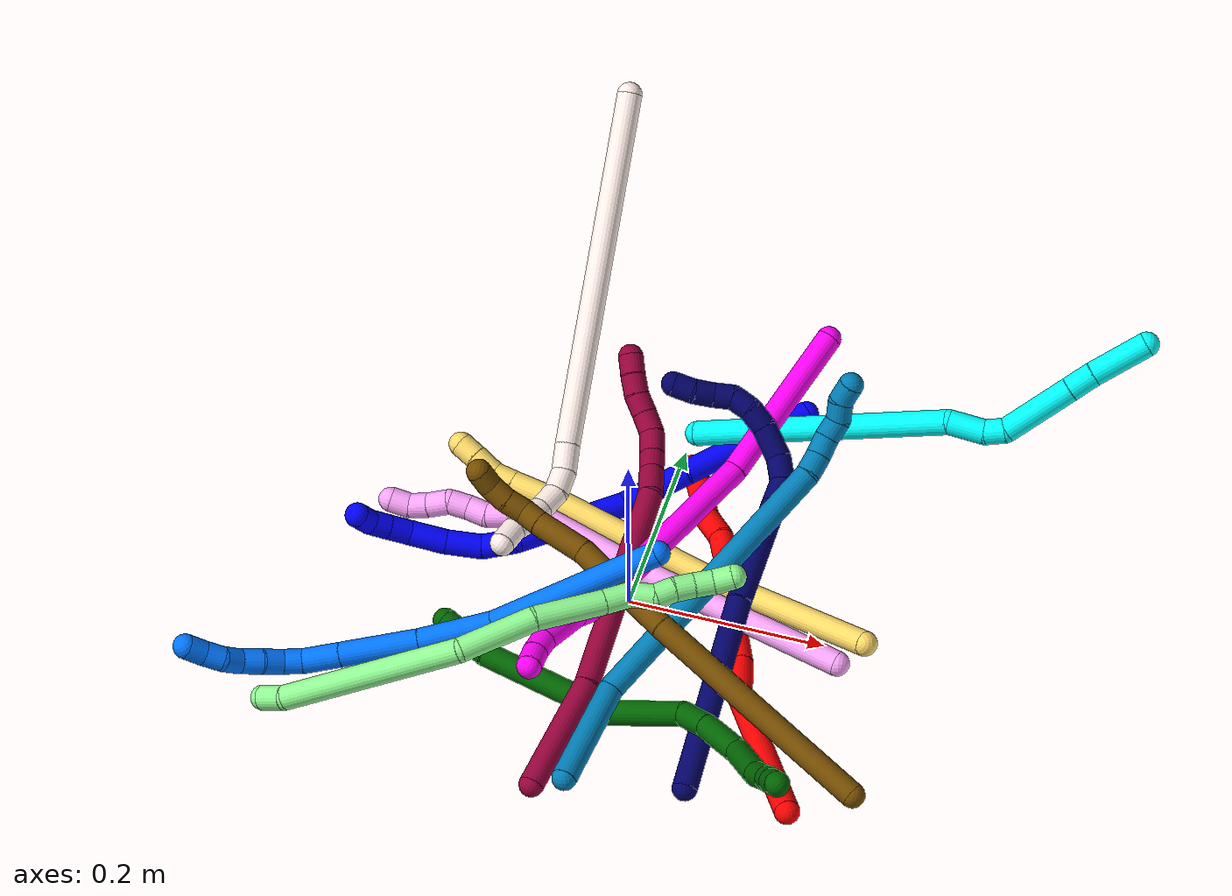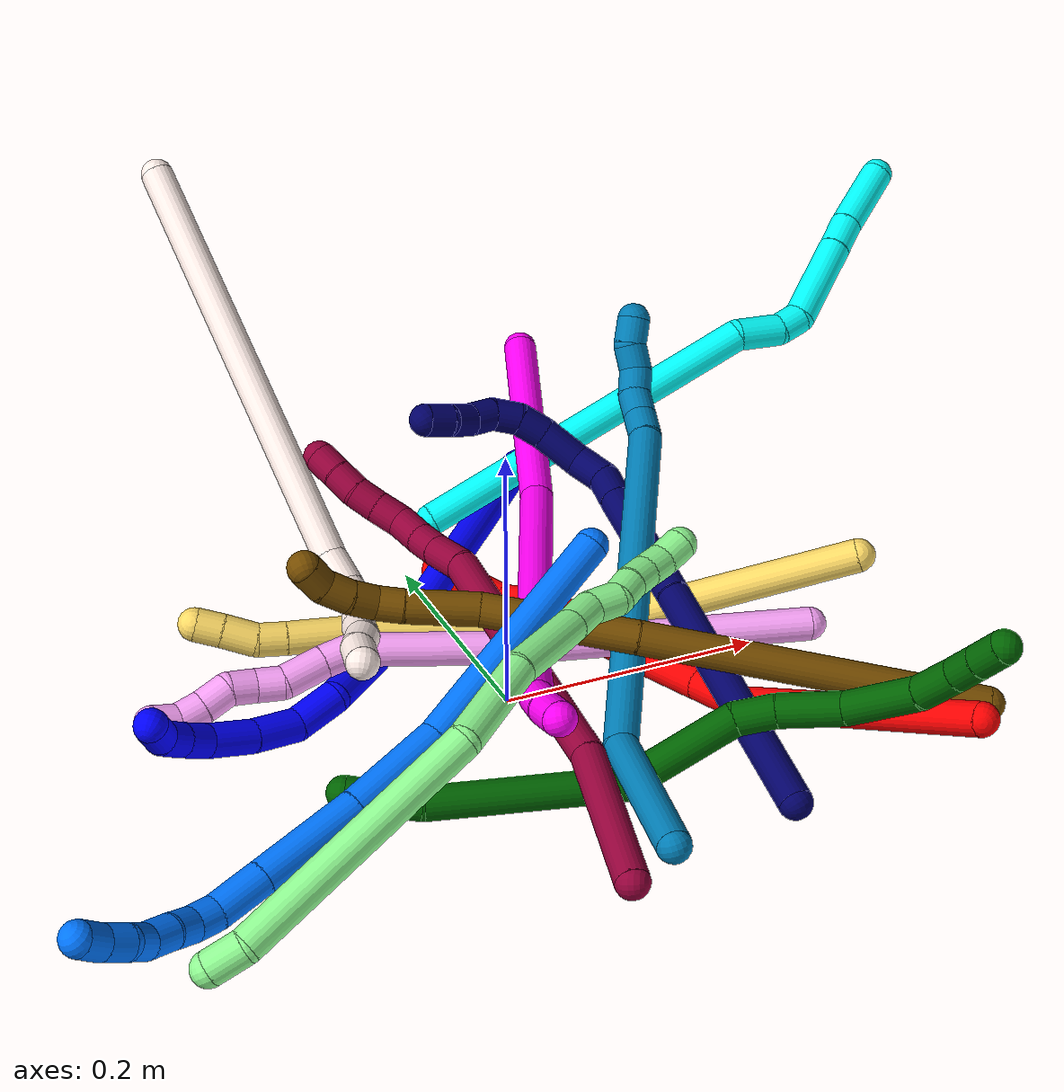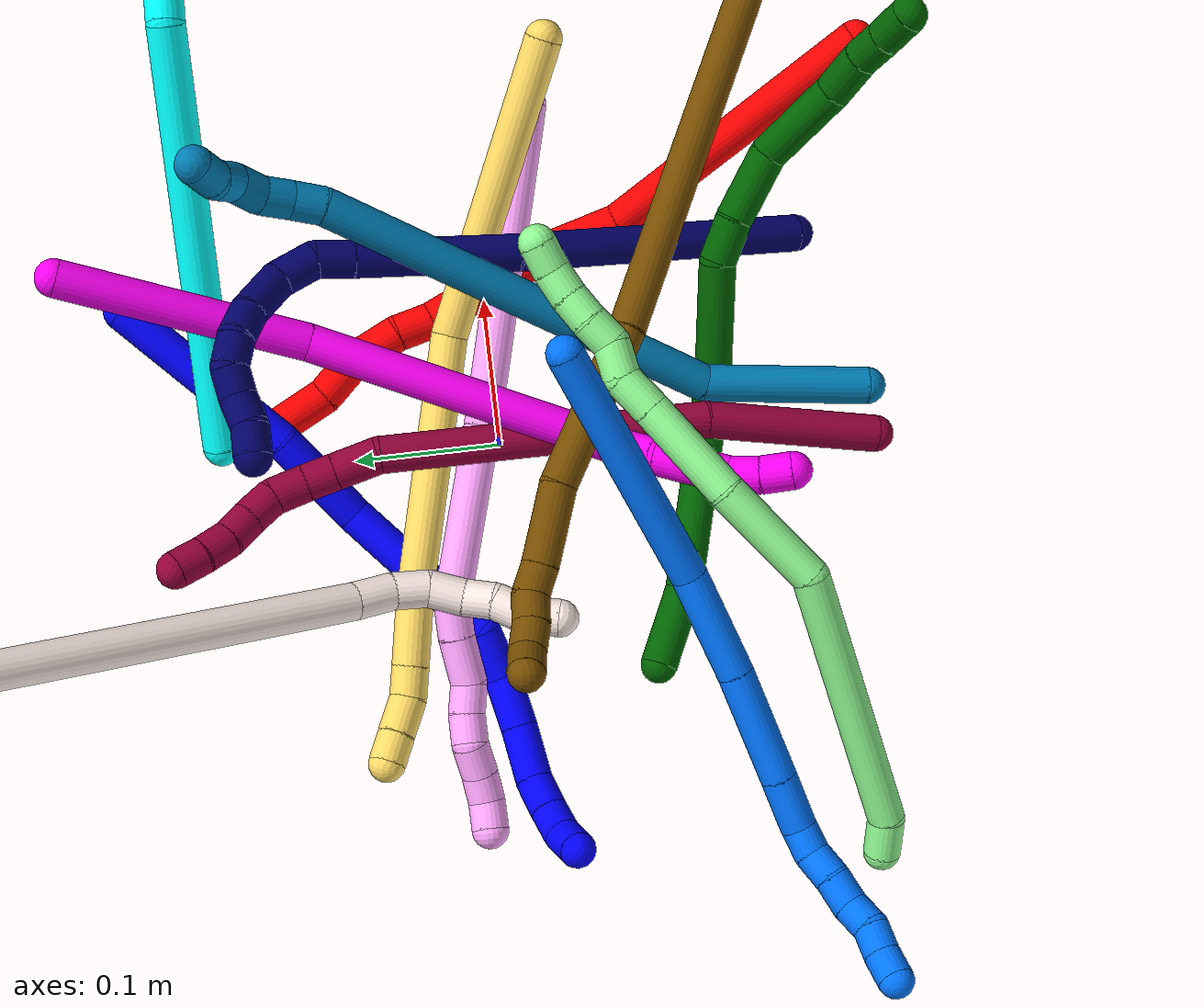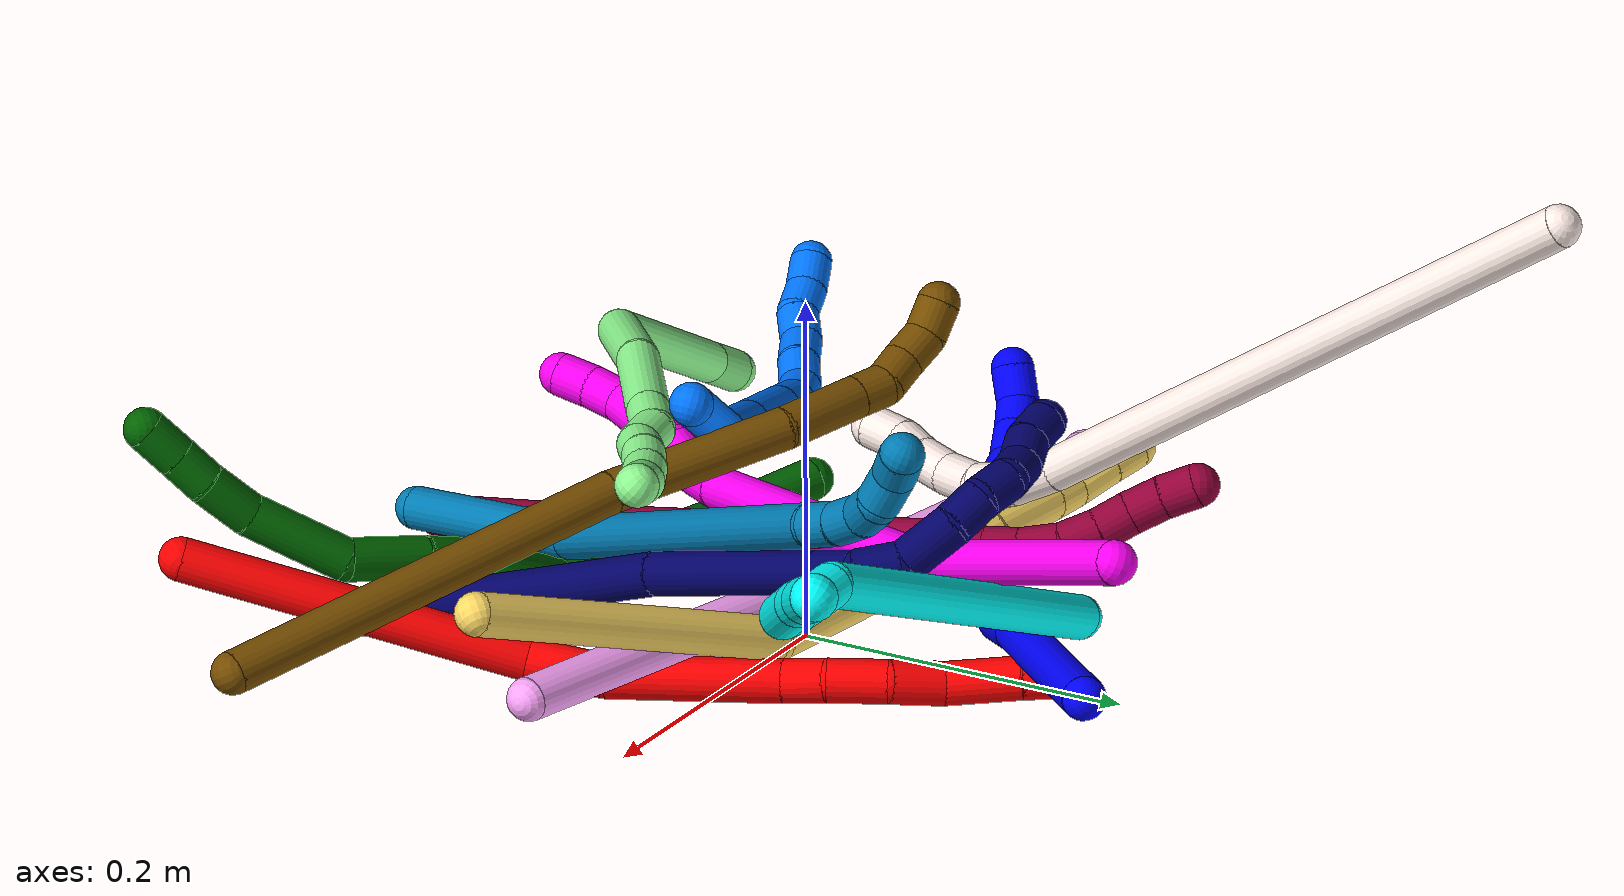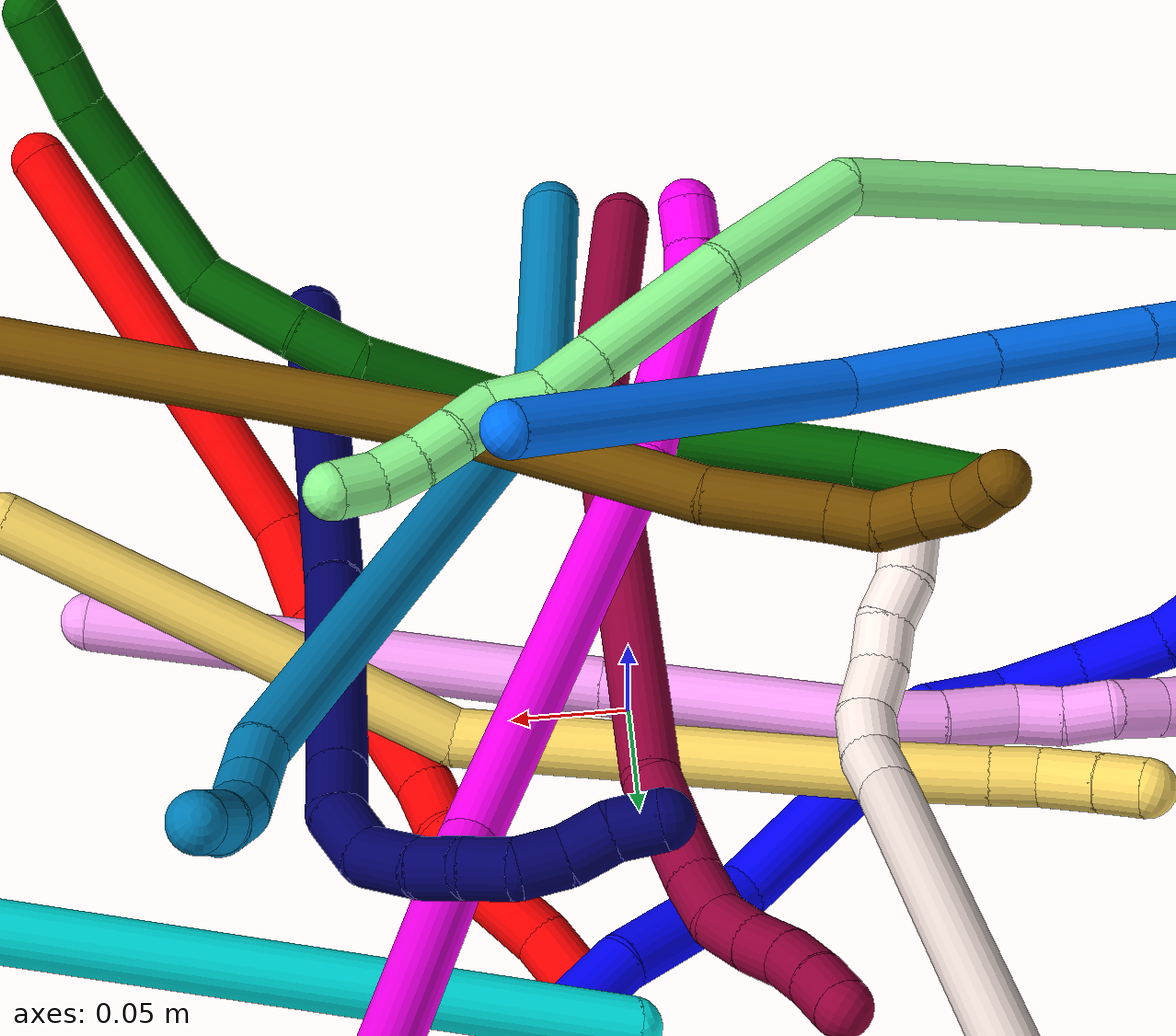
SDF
<sdf version="1.7">
 <world name="default">
  <plugin name="TubeGeneratorPlugin" filename="libtube_generator_plugin.so"/>
  <model name="photoneo_s_sensor">
   <static>1</static>
   <pose>0 0 2 1.57079 1.57079 3.14159</pose>
   <link name="link">
    <inertial><mass>0.1</mass></inertial>
    <sensor name="sensor" type="depth">
     <update_rate>30</update_rate>
     <camera>
      <horizontal_fov>1.22</horizontal_fov>
      <image><width>1920</width><height>1200</height><format>B8G8R8</format></image>
      <clip><near>0.1</near><far>4</far></clip>
      <depth_camera><output>points</output></depth_camera>
     </camera>
     <plugin name="camera_plugin" filename="libgazebo_ros_depth_camera.so">
      <baseline>0.2</baseline>
      <alwaysOn>1</alwaysOn>
      <updateRate>0.0</updateRate>
      <cameraName>camera_ir</cameraName>
      <imageTopicName>/camera/color/image_raw</imageTopicName>
      <cameraInfoTopicName>/camera/color/camera_info</cameraInfoTopicName>
      <depthImageTopicName>/camera/depth/image_raw</depthImageTopicName>
      <depthImageCameraInfoTopicName>/camera/depth/camera_info</depthImageCameraInfoTopicName>
      <pointCloudTopicName>/camera/depth/points</pointCloudTopicName>
      <frameName>fr_optical</frameName>
      <pointCloudCutoff>0.1</pointCloudCutoff>
      <pointCloudCutoffMax>2.0</pointCloudCutoffMax>
      <distortionK1>0</distortionK1>
      <distortionK2>0</distortionK2>
      <distortionK3>0</distortionK3>
      <distortionT1>0</distortionT1>
      <distortionT2>0</distortionT2>
      <CxPrime>0</CxPrime>
      <Cx>0</Cx>
      <Cy>0</Cy>
      <focalLength>0</focalLength>
      <hackBaseline>0</hackBaseline>
     </plugin>
    </sensor>
   </link>
  </model>
  <gravity>0 0 -9.8</gravity>
  <magnetic_field>6e-06 2.3e-05 -4.2e-05</magnetic_field>
  <atmosphere type="adiabatic"/>
  <physics name="default_physics" default="0" type="ode">
   <max_step_size>0.003</max_step_size>
   <real_time_factor>1</real_time_factor>
   <real_time_update_rate>1000</real_time_update_rate>
   <max_contacts>10000</max_contacts>
   <ode>
    <solver>
     <type>quick</type>
     <iters>100</iters>
     <sor>1.3</sor>
     <use_dynamic_moi_rescaling>0</use_dynamic_moi_rescaling>
    </solver>
    <constraints>
     <contact_max_correcting_vel>0</contact_max_correcting_vel>
     <contact_surface_layer>0.001</contact_surface_layer>
     <cfm>0</cfm>
     <erp>0.2</erp>
    </constraints>
   </ode>
  </physics>
  <scene><ambient>0.4 0.4 0.4 1</ambient><background>0.7 0.7 0.7 1</background><shadows>0</shadows></scene>
  <audio><device>default</device></audio>
  <spherical_coordinates>
   <surface_model>EARTH_WGS84</surface_model>
   <latitude_deg>0</latitude_deg>
   <longitude_deg>0</longitude_deg>
   <elevation>0</elevation>
   <heading_deg>0</heading_deg>
  </spherical_coordinates>
  <model name="bin">
   <static>1</static>
   <link name="bottom">
    <collision name="collision-bottom">
     <pose>0 0 -0.01 0 -0 0</pose>
     <geometry><box><size>0.8 0.6 0.02</size></box></geometry>
     <surface>
      <friction><ode><mu>100</mu><mu2>100</mu2></ode></friction>
      <contact><collide_bitmask>65535</collide_bitmask></contact>
     </surface>
    </collision>
   </link>
   <link name="west_wall">
    <collision name="collision-west_wall">
     <pose>-0.41 0 0.1 0 -0 0</pose>
     <geometry><box><size>0.02 0.6 0.2</size></box></geometry>
     <surface>
      <friction><ode><mu>100</mu><mu2>100</mu2></ode></friction>
      <contact><collide_bitmask>65535</collide_bitmask></contact>
     </surface>
    </collision>
   </link>
   <link name="east_wall">
    <collision name="collision-east_wall">
     <pose>0.41 0 0.1 0 -0 0</pose>
     <geometry><box><size>0.02 0.6 0.2</size></box></geometry>
     <surface>
      <friction><ode><mu>100</mu><mu2>100</mu2></ode></friction>
      <contact><collide_bitmask>65535</collide_bitmask></contact>
     </surface>
    </collision>
   </link>
   <link name="south_wall">
    <collision name="collision-south_wall">
     <pose>0 -0.31 0.1 0 -0 0</pose>
     <geometry><box><size>0.8 0.02 0.2</size></box></geometry>
     <surface>
      <friction><ode><mu>100</mu><mu2>100</mu2></ode></friction>
      <contact><collide_bitmask>65535</collide_bitmask></contact>
     </surface>
    </collision>
   </link>
   <link name="north_wall">
    <collision name="collision-north_wall">
     <pose>0 0.31 0.1 0 -0 0</pose>
     <geometry><box><size>0.8 0.02 0.2</size></box></geometry>
     <surface>
      <friction><ode><mu>100</mu><mu2>100</mu2></ode></friction>
      <contact><collide_bitmask>65535</collide_bitmask></contact>
     </surface>
    </collision>
   </link>
  </model>
  <model name="1">
   <static>0</static>
   <link name="1">
    <collision name="collision-cylinder-e_1_1_4">
     <pose>-0.00372 -0.014826 -0.066808 2.92321 -0.054304 -0.485698</pose>
     <geometry><cylinder><radius>0.0125</radius><length>0.137069</length></cylinder></geometry>
     <surface>
      <friction><ode><mu>1.16</mu><mu2>1.16</mu2><slip1>0</slip1><slip2>0</slip2></ode></friction>
      <contact><ode><kp>1e+06</kp><kd>1</kd><max_vel>0</max_vel><min_depth>0.001</min_depth></ode></contact>
     </surface>
    </collision>
    <visual name="visual-cylinder-e_1_1_4">
     <pose>-0.00372 -0.014826 -0.066808 2.92321 -0.054304 -0.485698</pose>
     <geometry><cylinder><radius>0.0125</radius><length>0.137069</length></cylinder></geometry>
     <material><ambient>0 0 1 1</ambient></material>
    </visual>
    <collision name="collision-cylinder-e_2_4_5">
     <pose>-0.014655 -0.031423 -0.16791 3.09 -0.207111 -2.65493</pose>
     <geometry><cylinder><radius>0.0125</radius><length>0.070177</length></cylinder></geometry>
     <surface>
      <friction><ode><mu>1.16</mu><mu2>1.16</mu2><slip1>0</slip1><slip2>0</slip2></ode></friction>
      <contact><ode><kp>1e+06</kp><kd>1</kd><max_vel>0</max_vel><min_depth>0.001</min_depth></ode></contact>
     </surface>
    </collision>
    <visual name="visual-cylinder-e_2_4_5">
     <pose>-0.014655 -0.031423 -0.16791 3.09 -0.207111 -2.65493</pose>
     <geometry><cylinder><radius>0.0125</radius><length>0.070177</length></cylinder></geometry>
     <material><ambient>0 0 1 1</ambient></material>
    </visual>
    <collision name="collision-cylinder-e_3_5_6">
     <pose>-0.026364 -0.054156 -0.256582 2.77367 -0.076948 -0.407999</pose>
     <geometry><cylinder><radius>0.0125</radius><length>0.116907</length></cylinder></geometry>
     <surface>
      <friction><ode><mu>1.16</mu><mu2>1.16</mu2><slip1>0</slip1><slip2>0</slip2></ode></friction>
      <contact><ode><kp>1e+06</kp><kd>1</kd><max_vel>0</max_vel><min_depth>0.001</min_depth></ode></contact>
     </surface>
    </collision>
    <visual name="visual-cylinder-e_3_5_6">
     <pose>-0.026364 -0.054156 -0.256582 2.77367 -0.076948 -0.407999</pose>
     <geometry><cylinder><radius>0.0125</radius><length>0.116907</length></cylinder></geometry>
     <material><ambient>0 0 1 1</ambient></material>
    </visual>
    <collision name="collision-cylinder-e_4_6_7">
     <pose>-0.040205 -0.077228 -0.326115 3.00324 -0.548481 -2.65863</pose>
     <geometry><cylinder><radius>0.0125</radius><length>0.035856</length></cylinder></geometry>
     <surface>
      <friction><ode><mu>1.16</mu><mu2>1.16</mu2><slip1>0</slip1><slip2>0</slip2></ode></friction>
      <contact><ode><kp>1e+06</kp><kd>1</kd><max_vel>0</max_vel><min_depth>0.001</min_depth></ode></contact>
     </surface>
    </collision>
    <visual name="visual-cylinder-e_4_6_7">
     <pose>-0.040205 -0.077228 -0.326115 3.00324 -0.548481 -2.65863</pose>
     <geometry><cylinder><radius>0.0125</radius><length>0.035856</length></cylinder></geometry>
     <material><ambient>0 0 1 1</ambient></material>
    </visual>
    <collision name="collision-cylinder-e_5_7_8">
     <pose>-0.059177 -0.088175 -0.354294 2.54554 -0.5488 -1.48363</pose>
     <geometry><cylinder><radius>0.0125</radius><length>0.036902</length></cylinder></geometry>
     <surface>
      <friction><ode><mu>1.16</mu><mu2>1.16</mu2><slip1>0</slip1><slip2>0</slip2></ode></friction>
      <contact><ode><kp>1e+06</kp><kd>1</kd><max_vel>0</max_vel><min_depth>0.001</min_depth></ode></contact>
     </surface>
    </collision>
    <visual name="visual-cylinder-e_5_7_8">
     <pose>-0.059177 -0.088175 -0.354294 2.54554 -0.5488 -1.48363</pose>
     <geometry><cylinder><radius>0.0125</radius><length>0.036902</length></cylinder></geometry>
     <material><ambient>0 0 1 1</ambient></material>
    </visual>
    <collision name="collision-cylinder-e_6_8_9">
     <pose>-0.078555 -0.108067 -0.379011 2.38408 -0.544878 -1.22416</pose>
     <geometry><cylinder><radius>0.0125</radius><length>0.03763</length></cylinder></geometry>
     <surface>
      <friction><ode><mu>1.16</mu><mu2>1.16</mu2><slip1>0</slip1><slip2>0</slip2></ode></friction>
      <contact><ode><kp>1e+06</kp><kd>1</kd><max_vel>0</max_vel><min_depth>0.001</min_depth></ode></contact>
     </surface>
    </collision>
    <visual name="visual-cylinder-e_6_8_9">
     <pose>-0.078555 -0.108067 -0.379011 2.38408 -0.544878 -1.22416</pose>
     <geometry><cylinder><radius>0.0125</radius><length>0.03763</length></cylinder></geometry>
     <material><ambient>0 0 1 1</ambient></material>
    </visual>
    <collision name="collision-cylinder-e_7_9_10">
     <pose>-0.091658 -0.128011 -0.397768 2.24253 -0.287038 -0.582035</pose>
     <geometry><cylinder><radius>0.0125</radius><length>0.023677</length></cylinder></geometry>
     <surface>
      <friction><ode><mu>1.16</mu><mu2>1.16</mu2><slip1>0</slip1><slip2>0</slip2></ode></friction>
      <contact><ode><kp>1e+06</kp><kd>1</kd><max_vel>0</max_vel><min_depth>0.001</min_depth></ode></contact>
     </surface>
    </collision>
    <visual name="visual-cylinder-e_7_9_10">
     <pose>-0.091658 -0.128011 -0.397768 2.24253 -0.287038 -0.582035</pose>
     <geometry><cylinder><radius>0.0125</radius><length>0.023677</length></cylinder></geometry>
     <material><ambient>0 0 1 1</ambient></material>
    </visual>
    <collision name="collision-cylinder-e_8_10_11">
     <pose>-0.097287 -0.144823 -0.41064 2.20308 -0.227776 -0.443759</pose>
     <geometry><cylinder><radius>0.0125</radius><length>0.020169</length></cylinder></geometry>
     <surface>
      <friction><ode><mu>1.16</mu><mu2>1.16</mu2><slip1>0</slip1><slip2>0</slip2></ode></friction>
      <contact><ode><kp>1e+06</kp><kd>1</kd><max_vel>0</max_vel><min_depth>0.001</min_depth></ode></contact>
     </surface>
    </collision>
    <visual name="visual-cylinder-e_8_10_11">
     <pose>-0.097287 -0.144823 -0.41064 2.20308 -0.227776 -0.443759</pose>
     <geometry><cylinder><radius>0.0125</radius><length>0.020169</length></cylinder></geometry>
     <material><ambient>0 0 1 1</ambient></material>
    </visual>
    <collision name="collision-cylinder-e_9_11_2">
     <pose>-0.098103 -0.16296 -0.419665 1.87617 0.13561 0.184693</pose>
     <geometry><cylinder><radius>0.0125</radius><length>0.021613</length></cylinder></geometry>
     <surface>
      <friction><ode><mu>1.16</mu><mu2>1.16</mu2><slip1>0</slip1><slip2>0</slip2></ode></friction>
      <contact><ode><kp>1e+06</kp><kd>1</kd><max_vel>0</max_vel><min_depth>0.001</min_depth></ode></contact>
     </surface>
    </collision>
    <visual name="visual-cylinder-e_9_11_2">
     <pose>-0.098103 -0.16296 -0.419665 1.87617 0.13561 0.184693</pose>
     <geometry><cylinder><radius>0.0125</radius><length>0.021613</length></cylinder></geometry>
     <material><ambient>0 0 1 1</ambient></material>
    </visual>
    <collision name="collision-sphere-2">
     <pose>-0.096642 -0.173172 -0.422884 0 -0 0</pose>
     <geometry><sphere><radius>0.0125</radius></sphere></geometry>
     <surface>
      <friction><ode><mu>1.16</mu><mu2>1.16</mu2><slip1>0</slip1><slip2>0</slip2></ode></friction>
      <contact><ode><kp>1e+06</kp><kd>1</kd><max_vel>0</max_vel><min_depth>0.001</min_depth></ode></contact>
     </surface>
    </collision>
    <visual name="visual-sphere-2">
     <pose>-0.096642 -0.173172 -0.422884 0 -0 0</pose>
     <geometry><sphere><radius>0.0125</radius></sphere></geometry>
     <material><ambient>0 0 1 1</ambient></material>
    </visual>
    <collision name="collision-sphere-11">
     <pose>-0.099564 -0.152748 -0.416445 0 -0 0</pose>
     <geometry><sphere><radius>0.0125</radius></sphere></geometry>
     <surface>
      <friction><ode><mu>1.16</mu><mu2>1.16</mu2><slip1>0</slip1><slip2>0</slip2></ode></friction>
      <contact><ode><kp>1e+06</kp><kd>1</kd><max_vel>0</max_vel><min_depth>0.001</min_depth></ode></contact>
     </surface>
    </collision>
    <visual name="visual-sphere-11">
     <pose>-0.099564 -0.152748 -0.416445 0 -0 0</pose>
     <geometry><sphere><radius>0.0125</radius></sphere></geometry>
     <material><ambient>0 0 1 1</ambient></material>
    </visual>
    <collision name="collision-sphere-10">
     <pose>-0.09501 -0.136898 -0.404834 0 -0 0</pose>
     <geometry><sphere><radius>0.0125</radius></sphere></geometry>
     <surface>
      <friction><ode><mu>1.16</mu><mu2>1.16</mu2><slip1>0</slip1><slip2>0</slip2></ode></friction>
      <contact><ode><kp>1e+06</kp><kd>1</kd><max_vel>0</max_vel><min_depth>0.001</min_depth></ode></contact>
     </surface>
    </collision>
    <visual name="visual-sphere-10">
     <pose>-0.09501 -0.136898 -0.404834 0 -0 0</pose>
     <geometry><sphere><radius>0.0125</radius></sphere></geometry>
     <material><ambient>0 0 1 1</ambient></material>
    </visual>
    <collision name="collision-sphere-9">
     <pose>-0.088307 -0.119123 -0.390701 0 -0 0</pose>
     <geometry><sphere><radius>0.0125</radius></sphere></geometry>
     <surface>
      <friction><ode><mu>1.16</mu><mu2>1.16</mu2><slip1>0</slip1><slip2>0</slip2></ode></friction>
      <contact><ode><kp>1e+06</kp><kd>1</kd><max_vel>0</max_vel><min_depth>0.001</min_depth></ode></contact>
     </surface>
    </collision>
    <visual name="visual-sphere-9">
     <pose>-0.088307 -0.119123 -0.390701 0 -0 0</pose>
     <geometry><sphere><radius>0.0125</radius></sphere></geometry>
     <material><ambient>0 0 1 1</ambient></material>
    </visual>
    <collision name="collision-sphere-4">
     <pose>-0.00744 -0.029652 -0.133617 0 -0 0</pose>
     <geometry><sphere><radius>0.0125</radius></sphere></geometry>
     <surface>
      <friction><ode><mu>1.16</mu><mu2>1.16</mu2><slip1>0</slip1><slip2>0</slip2></ode></friction>
      <contact><ode><kp>1e+06</kp><kd>1</kd><max_vel>0</max_vel><min_depth>0.001</min_depth></ode></contact>
     </surface>
    </collision>
    <visual name="visual-sphere-4">
     <pose>-0.00744 -0.029652 -0.133617 0 -0 0</pose>
     <geometry><sphere><radius>0.0125</radius></sphere></geometry>
     <material><ambient>0 0 1 1</ambient></material>
    </visual>
    <collision name="collision-sphere-1">
     <geometry><sphere><radius>0.0125</radius></sphere></geometry>
     <surface>
      <friction><ode><mu>1.16</mu><mu2>1.16</mu2><slip1>0</slip1><slip2>0</slip2></ode></friction>
      <contact><ode><kp>1e+06</kp><kd>1</kd><max_vel>0</max_vel><min_depth>0.001</min_depth></ode></contact>
     </surface>
    </collision>
    <visual name="visual-sphere-1">
     <geometry><sphere><radius>0.0125</radius></sphere></geometry>
     <material><ambient>0 0 1 1</ambient></material>
    </visual>
    <collision name="collision-sphere-8">
     <pose>-0.068803 -0.097011 -0.367321 0 -0 0</pose>
     <geometry><sphere><radius>0.0125</radius></sphere></geometry>
     <surface>
      <friction><ode><mu>1.16</mu><mu2>1.16</mu2><slip1>0</slip1><slip2>0</slip2></ode></friction>
      <contact><ode><kp>1e+06</kp><kd>1</kd><max_vel>0</max_vel><min_depth>0.001</min_depth></ode></contact>
     </surface>
    </collision>
    <visual name="visual-sphere-8">
     <pose>-0.068803 -0.097011 -0.367321 0 -0 0</pose>
     <geometry><sphere><radius>0.0125</radius></sphere></geometry>
     <material><ambient>0 0 1 1</ambient></material>
    </visual>
    <collision name="collision-sphere-5">
     <pose>-0.02187 -0.033193 -0.202202 0 -0 0</pose>
     <geometry><sphere><radius>0.0125</radius></sphere></geometry>
     <surface>
      <friction><ode><mu>1.16</mu><mu2>1.16</mu2><slip1>0</slip1><slip2>0</slip2></ode></friction>
      <contact><ode><kp>1e+06</kp><kd>1</kd><max_vel>0</max_vel><min_depth>0.001</min_depth></ode></contact>
     </surface>
    </collision>
    <visual name="visual-sphere-5">
     <pose>-0.02187 -0.033193 -0.202202 0 -0 0</pose>
     <geometry><sphere><radius>0.0125</radius></sphere></geometry>
     <material><ambient>0 0 1 1</ambient></material>
    </visual>
    <collision name="collision-sphere-6">
     <pose>-0.030857 -0.075118 -0.310962 0 -0 0</pose>
     <geometry><sphere><radius>0.0125</radius></sphere></geometry>
     <surface>
      <friction><ode><mu>1.16</mu><mu2>1.16</mu2><slip1>0</slip1><slip2>0</slip2></ode></friction>
      <contact><ode><kp>1e+06</kp><kd>1</kd><max_vel>0</max_vel><min_depth>0.001</min_depth></ode></contact>
     </surface>
    </collision>
    <visual name="visual-sphere-6">
     <pose>-0.030857 -0.075118 -0.310962 0 -0 0</pose>
     <geometry><sphere><radius>0.0125</radius></sphere></geometry>
     <material><ambient>0 0 1 1</ambient></material>
    </visual>
    <collision name="collision-sphere-7">
     <pose>-0.049552 -0.079338 -0.341267 0 -0 0</pose>
     <geometry><sphere><radius>0.0125</radius></sphere></geometry>
     <surface>
      <friction><ode><mu>1.16</mu><mu2>1.16</mu2><slip1>0</slip1><slip2>0</slip2></ode></friction>
      <contact><ode><kp>1e+06</kp><kd>1</kd><max_vel>0</max_vel><min_depth>0.001</min_depth></ode></contact>
     </surface>
    </collision>
    <visual name="visual-sphere-7">
     <pose>-0.049552 -0.079338 -0.341267 0 -0 0</pose>
     <geometry><sphere><radius>0.0125</radius></sphere></geometry>
     <material><ambient>0 0 1 1</ambient></material>
    </visual>
    <inertial>
     <pose>-0.034909 -0.060264 -0.233474 0 -0 0</pose>
     <mass>0.5</mass>
     <inertia>
      <ixx>0.000104</ixx>
      <ixy>0</ixy>
      <ixz>0</ixz>
      <iyy>-0.000471</iyy>
      <iyz>0</iyz>
      <izz>0.000115</izz>
     </inertia>
    </inertial>
   </link>
   <pose>0.113996 0.239681 0.054963 -1.24374 -0.195508 -0.763348</pose>
  </model>
  <model name="2">
   <static>0</static>
   <link name="2">
    <collision name="collision-cylinder-e_1_1_4">
     <pose>-0.065321 0.056673 -0.050769 -2.3013 -0.7094 1.38437</pose>
     <geometry><cylinder><radius>0.0125</radius><length>0.200561</length></cylinder></geometry>
     <surface>
      <friction><ode><mu>1.16</mu><mu2>1.16</mu2><slip1>0</slip1><slip2>0</slip2></ode></friction>
      <contact><ode><kp>1e+06</kp><kd>1</kd><max_vel>0</max_vel><min_depth>0.001</min_depth></ode></contact>
     </surface>
    </collision>
    <visual name="visual-cylinder-e_1_1_4">
     <pose>-0.065321 0.056673 -0.050769 -2.3013 -0.7094 1.38437</pose>
     <geometry><cylinder><radius>0.0125</radius><length>0.200561</length></cylinder></geometry>
     <material><ambient>1 0 0 1</ambient></material>
    </visual>
    <collision name="collision-cylinder-e_2_4_5">
     <pose>-0.139579 0.127568 -0.116538 -2.38282 -0.408136 0.957558</pose>
     <geometry><cylinder><radius>0.0125</radius><length>0.045039</length></cylinder></geometry>
     <surface>
      <friction><ode><mu>1.16</mu><mu2>1.16</mu2><slip1>0</slip1><slip2>0</slip2></ode></friction>
      <contact><ode><kp>1e+06</kp><kd>1</kd><max_vel>0</max_vel><min_depth>0.001</min_depth></ode></contact>
     </surface>
    </collision>
    <visual name="visual-cylinder-e_2_4_5">
     <pose>-0.139579 0.127568 -0.116538 -2.38282 -0.408136 0.957558</pose>
     <geometry><cylinder><radius>0.0125</radius><length>0.045039</length></cylinder></geometry>
     <material><ambient>1 0 0 1</ambient></material>
    </visual>
    <collision name="collision-cylinder-e_3_5_6">
     <pose>-0.16822 0.179957 -0.156572 -2.15132 -0.407489 0.730851</pose>
     <geometry><cylinder><radius>0.0125</radius><length>0.099432</length></cylinder></geometry>
     <surface>
      <friction><ode><mu>1.16</mu><mu2>1.16</mu2><slip1>0</slip1><slip2>0</slip2></ode></friction>
      <contact><ode><kp>1e+06</kp><kd>1</kd><max_vel>0</max_vel><min_depth>0.001</min_depth></ode></contact>
     </surface>
    </collision>
    <visual name="visual-cylinder-e_3_5_6">
     <pose>-0.16822 0.179957 -0.156572 -2.15132 -0.407489 0.730851</pose>
     <geometry><cylinder><radius>0.0125</radius><length>0.099432</length></cylinder></geometry>
     <material><ambient>1 0 0 1</ambient></material>
    </visual>
    <collision name="collision-cylinder-e_4_6_7">
     <pose>-0.190658 0.227884 -0.188845 -2.20888 -0.221474 0.434789</pose>
     <geometry><cylinder><radius>0.0125</radius><length>0.024911</length></cylinder></geometry>
     <surface>
      <friction><ode><mu>1.16</mu><mu2>1.16</mu2><slip1>0</slip1><slip2>0</slip2></ode></friction>
      <contact><ode><kp>1e+06</kp><kd>1</kd><max_vel>0</max_vel><min_depth>0.001</min_depth></ode></contact>
     </surface>
    </collision>
    <visual name="visual-cylinder-e_4_6_7">
     <pose>-0.190658 0.227884 -0.188845 -2.20888 -0.221474 0.434789</pose>
     <geometry><cylinder><radius>0.0125</radius><length>0.024911</length></cylinder></geometry>
     <material><ambient>1 0 0 1</ambient></material>
    </visual>
    <collision name="collision-cylinder-e_5_7_8">
     <pose>-0.200514 0.250754 -0.204304 -2.13092 -0.43122 0.753879</pose>
     <geometry><cylinder><radius>0.0125</radius><length>0.034067</length></cylinder></geometry>
     <surface>
      <friction><ode><mu>1.16</mu><mu2>1.16</mu2><slip1>0</slip1><slip2>0</slip2></ode></friction>
      <contact><ode><kp>1e+06</kp><kd>1</kd><max_vel>0</max_vel><min_depth>0.001</min_depth></ode></contact>
     </surface>
    </collision>
    <visual name="visual-cylinder-e_5_7_8">
     <pose>-0.200514 0.250754 -0.204304 -2.13092 -0.43122 0.753879</pose>
     <geometry><cylinder><radius>0.0125</radius><length>0.034067</length></cylinder></geometry>
     <material><ambient>1 0 0 1</ambient></material>
    </visual>
    <collision name="collision-cylinder-e_6_8_9">
     <pose>-0.217951 0.275222 -0.216761 -1.92769 -0.705114 0.974499</pose>
     <geometry><cylinder><radius>0.0125</radius><length>0.031837</length></cylinder></geometry>
     <surface>
      <friction><ode><mu>1.16</mu><mu2>1.16</mu2><slip1>0</slip1><slip2>0</slip2></ode></friction>
      <contact><ode><kp>1e+06</kp><kd>1</kd><max_vel>0</max_vel><min_depth>0.001</min_depth></ode></contact>
     </surface>
    </collision>
    <visual name="visual-cylinder-e_6_8_9">
     <pose>-0.217951 0.275222 -0.216761 -1.92769 -0.705114 0.974499</pose>
     <geometry><cylinder><radius>0.0125</radius><length>0.031837</length></cylinder></geometry>
     <material><ambient>1 0 0 1</ambient></material>
    </visual>
    <collision name="collision-cylinder-e_7_9_10">
     <pose>-0.23626 0.304499 -0.230138 -2.04258 -0.378214 0.605801</pose>
     <geometry><cylinder><radius>0.0125</radius><length>0.043289</length></cylinder></geometry>
     <surface>
      <friction><ode><mu>1.16</mu><mu2>1.16</mu2><slip1>0</slip1><slip2>0</slip2></ode></friction>
      <contact><ode><kp>1e+06</kp><kd>1</kd><max_vel>0</max_vel><min_depth>0.001</min_depth></ode></contact>
     </surface>
    </collision>
    <visual name="visual-cylinder-e_7_9_10">
     <pose>-0.23626 0.304499 -0.230138 -2.04258 -0.378214 0.605801</pose>
     <geometry><cylinder><radius>0.0125</radius><length>0.043289</length></cylinder></geometry>
     <material><ambient>1 0 0 1</ambient></material>
    </visual>
    <collision name="collision-cylinder-e_8_10_2">
     <pose>-0.248867 0.330883 -0.243261 -2.01044 -0.458168 0.704105</pose>
     <geometry><cylinder><radius>0.0125</radius><length>0.020864</length></cylinder></geometry>
     <surface>
      <friction><ode><mu>1.16</mu><mu2>1.16</mu2><slip1>0</slip1><slip2>0</slip2></ode></friction>
      <contact><ode><kp>1e+06</kp><kd>1</kd><max_vel>0</max_vel><min_depth>0.001</min_depth></ode></contact>
     </surface>
    </collision>
    <visual name="visual-cylinder-e_8_10_2">
     <pose>-0.248867 0.330883 -0.243261 -2.01044 -0.458168 0.704105</pose>
     <geometry><cylinder><radius>0.0125</radius><length>0.020864</length></cylinder></geometry>
     <material><ambient>1 0 0 1</ambient></material>
    </visual>
    <collision name="collision-sphere-2">
     <pose>-0.253482 0.339349 -0.247244 0 -0 0</pose>
     <geometry><sphere><radius>0.0125</radius></sphere></geometry>
     <surface>
      <friction><ode><mu>1.16</mu><mu2>1.16</mu2><slip1>0</slip1><slip2>0</slip2></ode></friction>
      <contact><ode><kp>1e+06</kp><kd>1</kd><max_vel>0</max_vel><min_depth>0.001</min_depth></ode></contact>
     </surface>
    </collision>
    <visual name="visual-sphere-2">
     <pose>-0.253482 0.339349 -0.247244 0 -0 0</pose>
     <geometry><sphere><radius>0.0125</radius></sphere></geometry>
     <material><ambient>1 0 0 1</ambient></material>
    </visual>
    <collision name="collision-sphere-10">
     <pose>-0.244253 0.322416 -0.239279 0 -0 0</pose>
     <geometry><sphere><radius>0.0125</radius></sphere></geometry>
     <surface>
      <friction><ode><mu>1.16</mu><mu2>1.16</mu2><slip1>0</slip1><slip2>0</slip2></ode></friction>
      <contact><ode><kp>1e+06</kp><kd>1</kd><max_vel>0</max_vel><min_depth>0.001</min_depth></ode></contact>
     </surface>
    </collision>
    <visual name="visual-sphere-10">
     <pose>-0.244253 0.322416 -0.239279 0 -0 0</pose>
     <geometry><sphere><radius>0.0125</radius></sphere></geometry>
     <material><ambient>1 0 0 1</ambient></material>
    </visual>
    <collision name="collision-sphere-9">
     <pose>-0.228268 0.286581 -0.220996 0 -0 0</pose>
     <geometry><sphere><radius>0.0125</radius></sphere></geometry>
     <surface>
      <friction><ode><mu>1.16</mu><mu2>1.16</mu2><slip1>0</slip1><slip2>0</slip2></ode></friction>
      <contact><ode><kp>1e+06</kp><kd>1</kd><max_vel>0</max_vel><min_depth>0.001</min_depth></ode></contact>
     </surface>
    </collision>
    <visual name="visual-sphere-9">
     <pose>-0.228268 0.286581 -0.220996 0 -0 0</pose>
     <geometry><sphere><radius>0.0125</radius></sphere></geometry>
     <material><ambient>1 0 0 1</ambient></material>
    </visual>
    <collision name="collision-sphere-4">
     <pose>-0.130641 0.113347 -0.101539 0 -0 0</pose>
     <geometry><sphere><radius>0.0125</radius></sphere></geometry>
     <surface>
      <friction><ode><mu>1.16</mu><mu2>1.16</mu2><slip1>0</slip1><slip2>0</slip2></ode></friction>
      <contact><ode><kp>1e+06</kp><kd>1</kd><max_vel>0</max_vel><min_depth>0.001</min_depth></ode></contact>
     </surface>
    </collision>
    <visual name="visual-sphere-4">
     <pose>-0.130641 0.113347 -0.101539 0 -0 0</pose>
     <geometry><sphere><radius>0.0125</radius></sphere></geometry>
     <material><ambient>1 0 0 1</ambient></material>
    </visual>
    <collision name="collision-sphere-1">
     <geometry><sphere><radius>0.0125</radius></sphere></geometry>
     <surface>
      <friction><ode><mu>1.16</mu><mu2>1.16</mu2><slip1>0</slip1><slip2>0</slip2></ode></friction>
      <contact><ode><kp>1e+06</kp><kd>1</kd><max_vel>0</max_vel><min_depth>0.001</min_depth></ode></contact>
     </surface>
    </collision>
    <visual name="visual-sphere-1">
     <geometry><sphere><radius>0.0125</radius></sphere></geometry>
     <material><ambient>1 0 0 1</ambient></material>
    </visual>
    <collision name="collision-sphere-8">
     <pose>-0.207634 0.263864 -0.212525 0 -0 0</pose>
     <geometry><sphere><radius>0.0125</radius></sphere></geometry>
     <surface>
      <friction><ode><mu>1.16</mu><mu2>1.16</mu2><slip1>0</slip1><slip2>0</slip2></ode></friction>
      <contact><ode><kp>1e+06</kp><kd>1</kd><max_vel>0</max_vel><min_depth>0.001</min_depth></ode></contact>
     </surface>
    </collision>
    <visual name="visual-sphere-8">
     <pose>-0.207634 0.263864 -0.212525 0 -0 0</pose>
     <geometry><sphere><radius>0.0125</radius></sphere></geometry>
     <material><ambient>1 0 0 1</ambient></material>
    </visual>
    <collision name="collision-sphere-5">
     <pose>-0.148517 0.14179 -0.131538 0 -0 0</pose>
     <geometry><sphere><radius>0.0125</radius></sphere></geometry>
     <surface>
      <friction><ode><mu>1.16</mu><mu2>1.16</mu2><slip1>0</slip1><slip2>0</slip2></ode></friction>
      <contact><ode><kp>1e+06</kp><kd>1</kd><max_vel>0</max_vel><min_depth>0.001</min_depth></ode></contact>
     </surface>
    </collision>
    <visual name="visual-sphere-5">
     <pose>-0.148517 0.14179 -0.131538 0 -0 0</pose>
     <geometry><sphere><radius>0.0125</radius></sphere></geometry>
     <material><ambient>1 0 0 1</ambient></material>
    </visual>
    <collision name="collision-sphere-6">
     <pose>-0.187922 0.218124 -0.181607 0 -0 0</pose>
     <geometry><sphere><radius>0.0125</radius></sphere></geometry>
     <surface>
      <friction><ode><mu>1.16</mu><mu2>1.16</mu2><slip1>0</slip1><slip2>0</slip2></ode></friction>
      <contact><ode><kp>1e+06</kp><kd>1</kd><max_vel>0</max_vel><min_depth>0.001</min_depth></ode></contact>
     </surface>
    </collision>
    <visual name="visual-sphere-6">
     <pose>-0.187922 0.218124 -0.181607 0 -0 0</pose>
     <geometry><sphere><radius>0.0125</radius></sphere></geometry>
     <material><ambient>1 0 0 1</ambient></material>
    </visual>
    <collision name="collision-sphere-7">
     <pose>-0.193394 0.237645 -0.196083 0 -0 0</pose>
     <geometry><sphere><radius>0.0125</radius></sphere></geometry>
     <surface>
      <friction><ode><mu>1.16</mu><mu2>1.16</mu2><slip1>0</slip1><slip2>0</slip2></ode></friction>
      <contact><ode><kp>1e+06</kp><kd>1</kd><max_vel>0</max_vel><min_depth>0.001</min_depth></ode></contact>
     </surface>
    </collision>
    <visual name="visual-sphere-7">
     <pose>-0.193394 0.237645 -0.196083 0 -0 0</pose>
     <geometry><sphere><radius>0.0125</radius></sphere></geometry>
     <material><ambient>1 0 0 1</ambient></material>
    </visual>
    <inertial>
     <pose>-0.140106 0.156144 -0.129205 0 -0 0</pose>
     <mass>0.5</mass>
     <inertia><ixx>0.000732</ixx><ixy>0</ixy><ixz>0</ixz><iyy>0.000825</iyy><iyz>0</iyz><izz>-2e-06</izz></inertia>
    </inertial>
   </link>
   <pose>0.235162 -0.263741 0.076241 1.08804 -0.821203 -0.218941</pose>
  </model>
  <model name="3">
   <static>0</static>
   <link name="3">
    <collision name="collision-cylinder-e_1_1_4">
     <pose>0.082713 -0.038091 0.107153 0.341552 0.628833 0.112049</pose>
     <geometry><cylinder><radius>0.0125</radius><length>0.281241</length></cylinder></geometry>
     <surface>
      <friction><ode><mu>1.16</mu><mu2>1.16</mu2><slip1>0</slip1><slip2>0</slip2></ode></friction>
      <contact><ode><kp>1e+06</kp><kd>1</kd><max_vel>0</max_vel><min_depth>0.001</min_depth></ode></contact>
     </surface>
    </collision>
    <visual name="visual-cylinder-e_1_1_4">
     <pose>0.082713 -0.038091 0.107153 0.341552 0.628833 0.112049</pose>
     <geometry><cylinder><radius>0.0125</radius><length>0.281241</length></cylinder></geometry>
     <material><ambient>0.003922 1 0.996078 1</ambient></material>
    </visual>
    <collision name="collision-cylinder-e_2_4_5">
     <pose>0.171278 -0.075389 0.231703 -0.045556 0.324108 -0.007449</pose>
     <geometry><cylinder><radius>0.0125</radius><length>0.036745</length></cylinder></geometry>
     <surface>
      <friction><ode><mu>1.16</mu><mu2>1.16</mu2><slip1>0</slip1><slip2>0</slip2></ode></friction>
      <contact><ode><kp>1e+06</kp><kd>1</kd><max_vel>0</max_vel><min_depth>0.001</min_depth></ode></contact>
     </surface>
    </collision>
    <visual name="visual-cylinder-e_2_4_5">
     <pose>0.171278 -0.075389 0.231703 -0.045556 0.324108 -0.007449</pose>
     <geometry><cylinder><radius>0.0125</radius><length>0.036745</length></cylinder></geometry>
     <material><ambient>0.003922 1 0.996078 1</ambient></material>
    </visual>
    <collision name="collision-cylinder-e_3_5_6">
     <pose>0.180848 -0.077917 0.258364 0.344214 0.361359 0.063485</pose>
     <geometry><cylinder><radius>0.0125</radius><length>0.02104</length></cylinder></geometry>
     <surface>
      <friction><ode><mu>1.16</mu><mu2>1.16</mu2><slip1>0</slip1><slip2>0</slip2></ode></friction>
      <contact><ode><kp>1e+06</kp><kd>1</kd><max_vel>0</max_vel><min_depth>0.001</min_depth></ode></contact>
     </surface>
    </collision>
    <visual name="visual-cylinder-e_3_5_6">
     <pose>0.180848 -0.077917 0.258364 0.344214 0.361359 0.063485</pose>
     <geometry><cylinder><radius>0.0125</radius><length>0.02104</length></cylinder></geometry>
     <material><ambient>0.003922 1 0.996078 1</ambient></material>
    </visual>
    <collision name="collision-cylinder-e_4_6_7">
     <pose>0.191571 -0.107845 0.292422 0.82065 0.19024 0.08296</pose>
     <geometry><cylinder><radius>0.0125</radius><length>0.074074</length></cylinder></geometry>
     <surface>
      <friction><ode><mu>1.16</mu><mu2>1.16</mu2><slip1>0</slip1><slip2>0</slip2></ode></friction>
      <contact><ode><kp>1e+06</kp><kd>1</kd><max_vel>0</max_vel><min_depth>0.001</min_depth></ode></contact>
     </surface>
    </collision>
    <visual name="visual-cylinder-e_4_6_7">
     <pose>0.191571 -0.107845 0.292422 0.82065 0.19024 0.08296</pose>
     <geometry><cylinder><radius>0.0125</radius><length>0.074074</length></cylinder></geometry>
     <material><ambient>0.003922 1 0.996078 1</ambient></material>
    </visual>
    <collision name="collision-cylinder-e_5_7_8">
     <pose>0.200664 -0.144284 0.326437 0.817491 0.153796 0.066722</pose>
     <geometry><cylinder><radius>0.0125</radius><length>0.027282</length></cylinder></geometry>
     <surface>
      <friction><ode><mu>1.16</mu><mu2>1.16</mu2><slip1>0</slip1><slip2>0</slip2></ode></friction>
      <contact><ode><kp>1e+06</kp><kd>1</kd><max_vel>0</max_vel><min_depth>0.001</min_depth></ode></contact>
     </surface>
    </collision>
    <visual name="visual-cylinder-e_5_7_8">
     <pose>0.200664 -0.144284 0.326437 0.817491 0.153796 0.066722</pose>
     <geometry><cylinder><radius>0.0125</radius><length>0.027282</length></cylinder></geometry>
     <material><ambient>0.003922 1 0.996078 1</ambient></material>
    </visual>
    <collision name="collision-cylinder-e_6_8_2">
     <pose>0.207922 -0.174103 0.357163 0.748805 0.174261 0.068621</pose>
     <geometry><cylinder><radius>0.0125</radius><length>0.059618</length></cylinder></geometry>
     <surface>
      <friction><ode><mu>1.16</mu><mu2>1.16</mu2><slip1>0</slip1><slip2>0</slip2></ode></friction>
      <contact><ode><kp>1e+06</kp><kd>1</kd><max_vel>0</max_vel><min_depth>0.001</min_depth></ode></contact>
     </surface>
    </collision>
    <visual name="visual-cylinder-e_6_8_2">
     <pose>0.207922 -0.174103 0.357163 0.748805 0.174261 0.068621</pose>
     <geometry><cylinder><radius>0.0125</radius><length>0.059618</length></cylinder></geometry>
     <material><ambient>0.003922 1 0.996078 1</ambient></material>
    </visual>
    <collision name="collision-sphere-2">
     <pose>0.21309 -0.194088 0.378668 0 -0 0</pose>
     <geometry><sphere><radius>0.0125</radius></sphere></geometry>
     <surface>
      <friction><ode><mu>1.16</mu><mu2>1.16</mu2><slip1>0</slip1><slip2>0</slip2></ode></friction>
      <contact><ode><kp>1e+06</kp><kd>1</kd><max_vel>0</max_vel><min_depth>0.001</min_depth></ode></contact>
     </surface>
    </collision>
    <visual name="visual-sphere-2">
     <pose>0.21309 -0.194088 0.378668 0 -0 0</pose>
     <geometry><sphere><radius>0.0125</radius></sphere></geometry>
     <material><ambient>0.003922 1 0.996078 1</ambient></material>
    </visual>
    <collision name="collision-sphere-4">
     <pose>0.165427 -0.076182 0.214306 0 -0 0</pose>
     <geometry><sphere><radius>0.0125</radius></sphere></geometry>
     <surface>
      <friction><ode><mu>1.16</mu><mu2>1.16</mu2><slip1>0</slip1><slip2>0</slip2></ode></friction>
      <contact><ode><kp>1e+06</kp><kd>1</kd><max_vel>0</max_vel><min_depth>0.001</min_depth></ode></contact>
     </surface>
    </collision>
    <visual name="visual-sphere-4">
     <pose>0.165427 -0.076182 0.214306 0 -0 0</pose>
     <geometry><sphere><radius>0.0125</radius></sphere></geometry>
     <material><ambient>0.003922 1 0.996078 1</ambient></material>
    </visual>
    <collision name="collision-sphere-1">
     <geometry><sphere><radius>0.0125</radius></sphere></geometry>
     <surface>
      <friction><ode><mu>1.16</mu><mu2>1.16</mu2><slip1>0</slip1><slip2>0</slip2></ode></friction>
      <contact><ode><kp>1e+06</kp><kd>1</kd><max_vel>0</max_vel><min_depth>0.001</min_depth></ode></contact>
     </surface>
    </collision>
    <visual name="visual-sphere-1">
     <geometry><sphere><radius>0.0125</radius></sphere></geometry>
     <material><ambient>0.003922 1 0.996078 1</ambient></material>
    </visual>
    <collision name="collision-sphere-8">
     <pose>0.202753 -0.154117 0.335658 0 -0 0</pose>
     <geometry><sphere><radius>0.0125</radius></sphere></geometry>
     <surface>
      <friction><ode><mu>1.16</mu><mu2>1.16</mu2><slip1>0</slip1><slip2>0</slip2></ode></friction>
      <contact><ode><kp>1e+06</kp><kd>1</kd><max_vel>0</max_vel><min_depth>0.001</min_depth></ode></contact>
     </surface>
    </collision>
    <visual name="visual-sphere-8">
     <pose>0.202753 -0.154117 0.335658 0 -0 0</pose>
     <geometry><sphere><radius>0.0125</radius></sphere></geometry>
     <material><ambient>0.003922 1 0.996078 1</ambient></material>
    </visual>
    <collision name="collision-sphere-5">
     <pose>0.177128 -0.074596 0.249101 0 -0 0</pose>
     <geometry><sphere><radius>0.0125</radius></sphere></geometry>
     <surface>
      <friction><ode><mu>1.16</mu><mu2>1.16</mu2><slip1>0</slip1><slip2>0</slip2></ode></friction>
      <contact><ode><kp>1e+06</kp><kd>1</kd><max_vel>0</max_vel><min_depth>0.001</min_depth></ode></contact>
     </surface>
    </collision>
    <visual name="visual-sphere-5">
     <pose>0.177128 -0.074596 0.249101 0 -0 0</pose>
     <geometry><sphere><radius>0.0125</radius></sphere></geometry>
     <material><ambient>0.003922 1 0.996078 1</ambient></material>
    </visual>
    <collision name="collision-sphere-6">
     <pose>0.184567 -0.081238 0.267628 0 -0 0</pose>
     <geometry><sphere><radius>0.0125</radius></sphere></geometry>
     <surface>
      <friction><ode><mu>1.16</mu><mu2>1.16</mu2><slip1>0</slip1><slip2>0</slip2></ode></friction>
      <contact><ode><kp>1e+06</kp><kd>1</kd><max_vel>0</max_vel><min_depth>0.001</min_depth></ode></contact>
     </surface>
    </collision>
    <visual name="visual-sphere-6">
     <pose>0.184567 -0.081238 0.267628 0 -0 0</pose>
     <geometry><sphere><radius>0.0125</radius></sphere></geometry>
     <material><ambient>0.003922 1 0.996078 1</ambient></material>
    </visual>
    <collision name="collision-sphere-7">
     <pose>0.198574 -0.134452 0.317217 0 -0 0</pose>
     <geometry><sphere><radius>0.0125</radius></sphere></geometry>
     <surface>
      <friction><ode><mu>1.16</mu><mu2>1.16</mu2><slip1>0</slip1><slip2>0</slip2></ode></friction>
      <contact><ode><kp>1e+06</kp><kd>1</kd><max_vel>0</max_vel><min_depth>0.001</min_depth></ode></contact>
     </surface>
    </collision>
    <visual name="visual-sphere-7">
     <pose>0.198574 -0.134452 0.317217 0 -0 0</pose>
     <geometry><sphere><radius>0.0125</radius></sphere></geometry>
     <material><ambient>0.003922 1 0.996078 1</ambient></material>
    </visual>
    <inertial>
     <pose>0.130844 -0.074854 0.191892 0 -0 0</pose>
     <mass>0.5</mass>
     <inertia>
      <ixx>0.001754</ixx>
      <ixy>0</ixy>
      <ixz>0</ixz>
      <iyy>0.001994</iyy>
      <iyz>0</iyz>
      <izz>-0.000533</izz>
     </inertia>
    </inertial>
   </link>
   <pose>0.01675 0.18354 0.055494 -1.91262 -0.734456 -1.10719</pose>
  </model>
  <model name="4">
   <static>0</static>
   <link name="4">
    <collision name="collision-cylinder-e_1_1_4">
     <pose>-0.031753 0.005422 0.105348 -0.051425 -0.292387 0.007574</pose>
     <geometry><cylinder><radius>0.0125</radius><length>0.220326</length></cylinder></geometry>
     <surface>
      <friction><ode><mu>1.16</mu><mu2>1.16</mu2><slip1>0</slip1><slip2>0</slip2></ode></friction>
      <contact><ode><kp>1e+06</kp><kd>1</kd><max_vel>0</max_vel><min_depth>0.001</min_depth></ode></contact>
     </surface>
    </collision>
    <visual name="visual-cylinder-e_1_1_4">
     <pose>-0.031753 0.005422 0.105348 -0.051425 -0.292387 0.007574</pose>
     <geometry><cylinder><radius>0.0125</radius><length>0.220326</length></cylinder></geometry>
     <material><ambient>1 0.65098 0.996078 1</ambient></material>
    </visual>
    <collision name="collision-cylinder-e_2_4_5">
     <pose>-0.082782 0.01709 0.267196 -0.110092 -0.326937 0.018176</pose>
     <geometry><cylinder><radius>0.0125</radius><length>0.120047</length></cylinder></geometry>
     <surface>
      <friction><ode><mu>1.16</mu><mu2>1.16</mu2><slip1>0</slip1><slip2>0</slip2></ode></friction>
      <contact><ode><kp>1e+06</kp><kd>1</kd><max_vel>0</max_vel><min_depth>0.001</min_depth></ode></contact>
     </surface>
    </collision>
    <visual name="visual-cylinder-e_2_4_5">
     <pose>-0.082782 0.01709 0.267196 -0.110092 -0.326937 0.018176</pose>
     <geometry><cylinder><radius>0.0125</radius><length>0.120047</length></cylinder></geometry>
     <material><ambient>1 0.65098 0.996078 1</ambient></material>
    </visual>
    <collision name="collision-cylinder-e_3_5_6">
     <pose>-0.101998 0.022113 0.335318 0.104801 0.005144 0.00027</pose>
     <geometry><cylinder><radius>0.0125</radius><length>0.023374</length></cylinder></geometry>
     <surface>
      <friction><ode><mu>1.16</mu><mu2>1.16</mu2><slip1>0</slip1><slip2>0</slip2></ode></friction>
      <contact><ode><kp>1e+06</kp><kd>1</kd><max_vel>0</max_vel><min_depth>0.001</min_depth></ode></contact>
     </surface>
    </collision>
    <visual name="visual-cylinder-e_3_5_6">
     <pose>-0.101998 0.022113 0.335318 0.104801 0.005144 0.00027</pose>
     <geometry><cylinder><radius>0.0125</radius><length>0.023374</length></cylinder></geometry>
     <material><ambient>1 0.65098 0.996078 1</ambient></material>
    </visual>
    <collision name="collision-cylinder-e_4_6_7">
     <pose>-0.099891 0.019189 0.363127 0.104701 0.125127 0.006565</pose>
     <geometry><cylinder><radius>0.0125</radius><length>0.032808</length></cylinder></geometry>
     <surface>
      <friction><ode><mu>1.16</mu><mu2>1.16</mu2><slip1>0</slip1><slip2>0</slip2></ode></friction>
      <contact><ode><kp>1e+06</kp><kd>1</kd><max_vel>0</max_vel><min_depth>0.001</min_depth></ode></contact>
     </surface>
    </collision>
    <visual name="visual-cylinder-e_4_6_7">
     <pose>-0.099891 0.019189 0.363127 0.104701 0.125127 0.006565</pose>
     <geometry><cylinder><radius>0.0125</radius><length>0.032808</length></cylinder></geometry>
     <material><ambient>1 0.65098 0.996078 1</ambient></material>
    </visual>
    <collision name="collision-cylinder-e_5_7_8">
     <pose>-0.100194 0.018291 0.389409 -0.079323 -0.228046 0.009089</pose>
     <geometry><cylinder><radius>0.0125</radius><length>0.020794</length></cylinder></geometry>
     <surface>
      <friction><ode><mu>1.16</mu><mu2>1.16</mu2><slip1>0</slip1><slip2>0</slip2></ode></friction>
      <contact><ode><kp>1e+06</kp><kd>1</kd><max_vel>0</max_vel><min_depth>0.001</min_depth></ode></contact>
     </surface>
    </collision>
    <visual name="visual-cylinder-e_5_7_8">
     <pose>-0.100194 0.018291 0.389409 -0.079323 -0.228046 0.009089</pose>
     <geometry><cylinder><radius>0.0125</radius><length>0.020794</length></cylinder></geometry>
     <material><ambient>1 0.65098 0.996078 1</ambient></material>
    </visual>
    <collision name="collision-cylinder-e_6_8_9">
     <pose>-0.103094 0.021096 0.409361 -0.200478 -0.054516 0.005484</pose>
     <geometry><cylinder><radius>0.0125</radius><length>0.020144</length></cylinder></geometry>
     <surface>
      <friction><ode><mu>1.16</mu><mu2>1.16</mu2><slip1>0</slip1><slip2>0</slip2></ode></friction>
      <contact><ode><kp>1e+06</kp><kd>1</kd><max_vel>0</max_vel><min_depth>0.001</min_depth></ode></contact>
     </surface>
    </collision>
    <visual name="visual-cylinder-e_6_8_9">
     <pose>-0.103094 0.021096 0.409361 -0.200478 -0.054516 0.005484</pose>
     <geometry><cylinder><radius>0.0125</radius><length>0.020144</length></cylinder></geometry>
     <material><ambient>1 0.65098 0.996078 1</ambient></material>
    </visual>
    <collision name="collision-cylinder-e_7_9_10">
     <pose>-0.10162 0.020336 0.429873 0.253721 0.181711 0.023239</pose>
     <geometry><cylinder><radius>0.0125</radius><length>0.022385</length></cylinder></geometry>
     <surface>
      <friction><ode><mu>1.16</mu><mu2>1.16</mu2><slip1>0</slip1><slip2>0</slip2></ode></friction>
      <contact><ode><kp>1e+06</kp><kd>1</kd><max_vel>0</max_vel><min_depth>0.001</min_depth></ode></contact>
     </surface>
    </collision>
    <visual name="visual-cylinder-e_7_9_10">
     <pose>-0.10162 0.020336 0.429873 0.253721 0.181711 0.023239</pose>
     <geometry><cylinder><radius>0.0125</radius><length>0.022385</length></cylinder></geometry>
     <material><ambient>1 0.65098 0.996078 1</ambient></material>
    </visual>
    <collision name="collision-cylinder-e_8_10_11">
     <pose>-0.098373 0.016117 0.450392 0.146557 0.122216 0.008983</pose>
     <geometry><cylinder><radius>0.0125</radius><length>0.020089</length></cylinder></geometry>
     <surface>
      <friction><ode><mu>1.16</mu><mu2>1.16</mu2><slip1>0</slip1><slip2>0</slip2></ode></friction>
      <contact><ode><kp>1e+06</kp><kd>1</kd><max_vel>0</max_vel><min_depth>0.001</min_depth></ode></contact>
     </surface>
    </collision>
    <visual name="visual-cylinder-e_8_10_11">
     <pose>-0.098373 0.016117 0.450392 0.146557 0.122216 0.008983</pose>
     <geometry><cylinder><radius>0.0125</radius><length>0.020089</length></cylinder></geometry>
     <material><ambient>1 0.65098 0.996078 1</ambient></material>
    </visual>
    <collision name="collision-cylinder-e_9_11_2">
     <pose>-0.097586 0.017403 0.469879 -0.277556 -0.043698 0.006105</pose>
     <geometry><cylinder><radius>0.0125</radius><length>0.020034</length></cylinder></geometry>
     <surface>
      <friction><ode><mu>1.16</mu><mu2>1.16</mu2><slip1>0</slip1><slip2>0</slip2></ode></friction>
      <contact><ode><kp>1e+06</kp><kd>1</kd><max_vel>0</max_vel><min_depth>0.001</min_depth></ode></contact>
     </surface>
    </collision>
    <visual name="visual-cylinder-e_9_11_2">
     <pose>-0.097586 0.017403 0.469879 -0.277556 -0.043698 0.006105</pose>
     <geometry><cylinder><radius>0.0125</radius><length>0.020034</length></cylinder></geometry>
     <material><ambient>1 0.65098 0.996078 1</ambient></material>
    </visual>
    <collision name="collision-sphere-2">
     <pose>-0.098023 0.020145 0.479503 0 -0 0</pose>
     <geometry><sphere><radius>0.0125</radius></sphere></geometry>
     <surface>
      <friction><ode><mu>1.16</mu><mu2>1.16</mu2><slip1>0</slip1><slip2>0</slip2></ode></friction>
      <contact><ode><kp>1e+06</kp><kd>1</kd><max_vel>0</max_vel><min_depth>0.001</min_depth></ode></contact>
     </surface>
    </collision>
    <visual name="visual-sphere-2">
     <pose>-0.098023 0.020145 0.479503 0 -0 0</pose>
     <geometry><sphere><radius>0.0125</radius></sphere></geometry>
     <material><ambient>1 0.65098 0.996078 1</ambient></material>
    </visual>
    <collision name="collision-sphere-11">
     <pose>-0.097148 0.014661 0.460254 0 -0 0</pose>
     <geometry><sphere><radius>0.0125</radius></sphere></geometry>
     <surface>
      <friction><ode><mu>1.16</mu><mu2>1.16</mu2><slip1>0</slip1><slip2>0</slip2></ode></friction>
      <contact><ode><kp>1e+06</kp><kd>1</kd><max_vel>0</max_vel><min_depth>0.001</min_depth></ode></contact>
     </surface>
    </collision>
    <visual name="visual-sphere-11">
     <pose>-0.097148 0.014661 0.460254 0 -0 0</pose>
     <geometry><sphere><radius>0.0125</radius></sphere></geometry>
     <material><ambient>1 0.65098 0.996078 1</ambient></material>
    </visual>
    <collision name="collision-sphere-10">
     <pose>-0.099597 0.017573 0.440529 0 -0 0</pose>
     <geometry><sphere><radius>0.0125</radius></sphere></geometry>
     <surface>
      <friction><ode><mu>1.16</mu><mu2>1.16</mu2><slip1>0</slip1><slip2>0</slip2></ode></friction>
      <contact><ode><kp>1e+06</kp><kd>1</kd><max_vel>0</max_vel><min_depth>0.001</min_depth></ode></contact>
     </surface>
    </collision>
    <visual name="visual-sphere-10">
     <pose>-0.099597 0.017573 0.440529 0 -0 0</pose>
     <geometry><sphere><radius>0.0125</radius></sphere></geometry>
     <material><ambient>1 0.65098 0.996078 1</ambient></material>
    </visual>
    <collision name="collision-sphere-9">
     <pose>-0.103643 0.023099 0.419217 0 -0 0</pose>
     <geometry><sphere><radius>0.0125</radius></sphere></geometry>
     <surface>
      <friction><ode><mu>1.16</mu><mu2>1.16</mu2><slip1>0</slip1><slip2>0</slip2></ode></friction>
      <contact><ode><kp>1e+06</kp><kd>1</kd><max_vel>0</max_vel><min_depth>0.001</min_depth></ode></contact>
     </surface>
    </collision>
    <visual name="visual-sphere-9">
     <pose>-0.103643 0.023099 0.419217 0 -0 0</pose>
     <geometry><sphere><radius>0.0125</radius></sphere></geometry>
     <material><ambient>1 0.65098 0.996078 1</ambient></material>
    </visual>
    <collision name="collision-sphere-4">
     <pose>-0.063506 0.010845 0.210696 0 -0 0</pose>
     <geometry><sphere><radius>0.0125</radius></sphere></geometry>
     <surface>
      <friction><ode><mu>1.16</mu><mu2>1.16</mu2><slip1>0</slip1><slip2>0</slip2></ode></friction>
      <contact><ode><kp>1e+06</kp><kd>1</kd><max_vel>0</max_vel><min_depth>0.001</min_depth></ode></contact>
     </surface>
    </collision>
    <visual name="visual-sphere-4">
     <pose>-0.063506 0.010845 0.210696 0 -0 0</pose>
     <geometry><sphere><radius>0.0125</radius></sphere></geometry>
     <material><ambient>1 0.65098 0.996078 1</ambient></material>
    </visual>
    <collision name="collision-sphere-1">
     <geometry><sphere><radius>0.0125</radius></sphere></geometry>
     <surface>
      <friction><ode><mu>1.16</mu><mu2>1.16</mu2><slip1>0</slip1><slip2>0</slip2></ode></friction>
      <contact><ode><kp>1e+06</kp><kd>1</kd><max_vel>0</max_vel><min_depth>0.001</min_depth></ode></contact>
     </surface>
    </collision>
    <visual name="visual-sphere-1">
     <geometry><sphere><radius>0.0125</radius></sphere></geometry>
     <material><ambient>1 0.65098 0.996078 1</ambient></material>
    </visual>
    <collision name="collision-sphere-8">
     <pose>-0.102545 0.019094 0.399505 0 -0 0</pose>
     <geometry><sphere><radius>0.0125</radius></sphere></geometry>
     <surface>
      <friction><ode><mu>1.16</mu><mu2>1.16</mu2><slip1>0</slip1><slip2>0</slip2></ode></friction>
      <contact><ode><kp>1e+06</kp><kd>1</kd><max_vel>0</max_vel><min_depth>0.001</min_depth></ode></contact>
     </surface>
    </collision>
    <visual name="visual-sphere-8">
     <pose>-0.102545 0.019094 0.399505 0 -0 0</pose>
     <geometry><sphere><radius>0.0125</radius></sphere></geometry>
     <material><ambient>1 0.65098 0.996078 1</ambient></material>
    </visual>
    <collision name="collision-sphere-5">
     <pose>-0.102059 0.023335 0.323695 0 -0 0</pose>
     <geometry><sphere><radius>0.0125</radius></sphere></geometry>
     <surface>
      <friction><ode><mu>1.16</mu><mu2>1.16</mu2><slip1>0</slip1><slip2>0</slip2></ode></friction>
      <contact><ode><kp>1e+06</kp><kd>1</kd><max_vel>0</max_vel><min_depth>0.001</min_depth></ode></contact>
     </surface>
    </collision>
    <visual name="visual-sphere-5">
     <pose>-0.102059 0.023335 0.323695 0 -0 0</pose>
     <geometry><sphere><radius>0.0125</radius></sphere></geometry>
     <material><ambient>1 0.65098 0.996078 1</ambient></material>
    </visual>
    <collision name="collision-sphere-6">
     <pose>-0.101938 0.02089 0.34694 0 -0 0</pose>
     <geometry><sphere><radius>0.0125</radius></sphere></geometry>
     <surface>
      <friction><ode><mu>1.16</mu><mu2>1.16</mu2><slip1>0</slip1><slip2>0</slip2></ode></friction>
      <contact><ode><kp>1e+06</kp><kd>1</kd><max_vel>0</max_vel><min_depth>0.001</min_depth></ode></contact>
     </surface>
    </collision>
    <visual name="visual-sphere-6">
     <pose>-0.101938 0.02089 0.34694 0 -0 0</pose>
     <geometry><sphere><radius>0.0125</radius></sphere></geometry>
     <material><ambient>1 0.65098 0.996078 1</ambient></material>
    </visual>
    <collision name="collision-sphere-7">
     <pose>-0.097844 0.017488 0.379313 0 -0 0</pose>
     <geometry><sphere><radius>0.0125</radius></sphere></geometry>
     <surface>
      <friction><ode><mu>1.16</mu><mu2>1.16</mu2><slip1>0</slip1><slip2>0</slip2></ode></friction>
      <contact><ode><kp>1e+06</kp><kd>1</kd><max_vel>0</max_vel><min_depth>0.001</min_depth></ode></contact>
     </surface>
    </collision>
    <visual name="visual-sphere-7">
     <pose>-0.097844 0.017488 0.379313 0 -0 0</pose>
     <geometry><sphere><radius>0.0125</radius></sphere></geometry>
     <material><ambient>1 0.65098 0.996078 1</ambient></material>
    </visual>
    <inertial>
     <pose>-0.065923 0.012651 0.238931 0 -0 0</pose>
     <mass>0.5</mass>
     <inertia>
      <ixx>0.001018</ixx>
      <ixy>0</ixy>
      <ixz>0</ixz>
      <iyy>0.001071</iyy>
      <iyz>0</iyz>
      <izz>0.000285</izz>
     </inertia>
    </inertial>
   </link>
   <pose>0.224764 -0.045029 0.034892 1.65478 0.142489 -1.53159</pose>
  </model>
  <model name="5">
   <static>0</static>
   <link name="5">
    <collision name="collision-cylinder-e_1_1_4">
     <pose>-0.087228 0.055742 0.009661 -1.39919 -0.995426 0.857768</pose>
     <geometry><cylinder><radius>0.0125</radius><length>0.207934</length></cylinder></geometry>
     <surface>
      <friction><ode><mu>1.16</mu><mu2>1.16</mu2><slip1>0</slip1><slip2>0</slip2></ode></friction>
      <contact><ode><kp>1e+06</kp><kd>1</kd><max_vel>0</max_vel><min_depth>0.001</min_depth></ode></contact>
     </surface>
    </collision>
    <visual name="visual-cylinder-e_1_1_4">
     <pose>-0.087228 0.055742 0.009661 -1.39919 -0.995426 0.857768</pose>
     <geometry><cylinder><radius>0.0125</radius><length>0.207934</length></cylinder></geometry>
     <material><ambient>1 0.858824 0.4 1</ambient></material>
    </visual>
    <collision name="collision-cylinder-e_2_4_5">
     <pose>-0.250058 0.144624 -0.007125 -2.24434 -1.0597 1.76576</pose>
     <geometry><cylinder><radius>0.0125</radius><length>0.173361</length></cylinder></geometry>
     <surface>
      <friction><ode><mu>1.16</mu><mu2>1.16</mu2><slip1>0</slip1><slip2>0</slip2></ode></friction>
      <contact><ode><kp>1e+06</kp><kd>1</kd><max_vel>0</max_vel><min_depth>0.001</min_depth></ode></contact>
     </surface>
    </collision>
    <visual name="visual-cylinder-e_2_4_5">
     <pose>-0.250058 0.144624 -0.007125 -2.24434 -1.0597 1.76576</pose>
     <geometry><cylinder><radius>0.0125</radius><length>0.173361</length></cylinder></geometry>
     <material><ambient>1 0.858824 0.4 1</ambient></material>
    </visual>
    <collision name="collision-cylinder-e_3_5_6">
     <pose>-0.346978 0.189157 -0.041884 -2.20108 -0.986282 1.62652</pose>
     <geometry><cylinder><radius>0.0125</radius><length>0.051119</length></cylinder></geometry>
     <surface>
      <friction><ode><mu>1.16</mu><mu2>1.16</mu2><slip1>0</slip1><slip2>0</slip2></ode></friction>
      <contact><ode><kp>1e+06</kp><kd>1</kd><max_vel>0</max_vel><min_depth>0.001</min_depth></ode></contact>
     </surface>
    </collision>
    <visual name="visual-cylinder-e_3_5_6">
     <pose>-0.346978 0.189157 -0.041884 -2.20108 -0.986282 1.62652</pose>
     <geometry><cylinder><radius>0.0125</radius><length>0.051119</length></cylinder></geometry>
     <material><ambient>1 0.858824 0.4 1</ambient></material>
    </visual>
    <collision name="collision-cylinder-e_4_6_7">
     <pose>-0.377332 0.205003 -0.053918 -2.26706 -1.00004 1.7261</pose>
     <geometry><cylinder><radius>0.0125</radius><length>0.02148</length></cylinder></geometry>
     <surface>
      <friction><ode><mu>1.16</mu><mu2>1.16</mu2><slip1>0</slip1><slip2>0</slip2></ode></friction>
      <contact><ode><kp>1e+06</kp><kd>1</kd><max_vel>0</max_vel><min_depth>0.001</min_depth></ode></contact>
     </surface>
    </collision>
    <visual name="visual-cylinder-e_4_6_7">
     <pose>-0.377332 0.205003 -0.053918 -2.26706 -1.00004 1.7261</pose>
     <geometry><cylinder><radius>0.0125</radius><length>0.02148</length></cylinder></geometry>
     <material><ambient>1 0.858824 0.4 1</ambient></material>
    </visual>
    <collision name="collision-cylinder-e_5_7_8">
     <pose>-0.39862 0.210746 -0.061842 -2.84356 -1.22622 2.72112</pose>
     <geometry><cylinder><radius>0.0125</radius><length>0.026031</length></cylinder></geometry>
     <surface>
      <friction><ode><mu>1.16</mu><mu2>1.16</mu2><slip1>0</slip1><slip2>0</slip2></ode></friction>
      <contact><ode><kp>1e+06</kp><kd>1</kd><max_vel>0</max_vel><min_depth>0.001</min_depth></ode></contact>
     </surface>
    </collision>
    <visual name="visual-cylinder-e_5_7_8">
     <pose>-0.39862 0.210746 -0.061842 -2.84356 -1.22622 2.72112</pose>
     <geometry><cylinder><radius>0.0125</radius><length>0.026031</length></cylinder></geometry>
     <material><ambient>1 0.858824 0.4 1</ambient></material>
    </visual>
    <collision name="collision-cylinder-e_6_8_2">
     <pose>-0.420337 0.213425 -0.069078 -2.71253 -1.23205 2.54445</pose>
     <geometry><cylinder><radius>0.0125</radius><length>0.020074</length></cylinder></geometry>
     <surface>
      <friction><ode><mu>1.16</mu><mu2>1.16</mu2><slip1>0</slip1><slip2>0</slip2></ode></friction>
      <contact><ode><kp>1e+06</kp><kd>1</kd><max_vel>0</max_vel><min_depth>0.001</min_depth></ode></contact>
     </surface>
    </collision>
    <visual name="visual-cylinder-e_6_8_2">
     <pose>-0.420337 0.213425 -0.069078 -2.71253 -1.23205 2.54445</pose>
     <geometry><cylinder><radius>0.0125</radius><length>0.020074</length></cylinder></geometry>
     <material><ambient>1 0.858824 0.4 1</ambient></material>
    </visual>
    <collision name="collision-sphere-2">
     <pose>-0.429804 0.214812 -0.072111 0 -0 0</pose>
     <geometry><sphere><radius>0.0125</radius></sphere></geometry>
     <surface>
      <friction><ode><mu>1.16</mu><mu2>1.16</mu2><slip1>0</slip1><slip2>0</slip2></ode></friction>
      <contact><ode><kp>1e+06</kp><kd>1</kd><max_vel>0</max_vel><min_depth>0.001</min_depth></ode></contact>
     </surface>
    </collision>
    <visual name="visual-sphere-2">
     <pose>-0.429804 0.214812 -0.072111 0 -0 0</pose>
     <geometry><sphere><radius>0.0125</radius></sphere></geometry>
     <material><ambient>1 0.858824 0.4 1</ambient></material>
    </visual>
    <collision name="collision-sphere-4">
     <pose>-0.174455 0.111485 0.019321 0 -0 0</pose>
     <geometry><sphere><radius>0.0125</radius></sphere></geometry>
     <surface>
      <friction><ode><mu>1.16</mu><mu2>1.16</mu2><slip1>0</slip1><slip2>0</slip2></ode></friction>
      <contact><ode><kp>1e+06</kp><kd>1</kd><max_vel>0</max_vel><min_depth>0.001</min_depth></ode></contact>
     </surface>
    </collision>
    <visual name="visual-sphere-4">
     <pose>-0.174455 0.111485 0.019321 0 -0 0</pose>
     <geometry><sphere><radius>0.0125</radius></sphere></geometry>
     <material><ambient>1 0.858824 0.4 1</ambient></material>
    </visual>
    <collision name="collision-sphere-1">
     <geometry><sphere><radius>0.0125</radius></sphere></geometry>
     <surface>
      <friction><ode><mu>1.16</mu><mu2>1.16</mu2><slip1>0</slip1><slip2>0</slip2></ode></friction>
      <contact><ode><kp>1e+06</kp><kd>1</kd><max_vel>0</max_vel><min_depth>0.001</min_depth></ode></contact>
     </surface>
    </collision>
    <visual name="visual-sphere-1">
     <geometry><sphere><radius>0.0125</radius></sphere></geometry>
     <material><ambient>1 0.858824 0.4 1</ambient></material>
    </visual>
    <collision name="collision-sphere-8">
     <pose>-0.41087 0.212037 -0.066045 0 -0 0</pose>
     <geometry><sphere><radius>0.0125</radius></sphere></geometry>
     <surface>
      <friction><ode><mu>1.16</mu><mu2>1.16</mu2><slip1>0</slip1><slip2>0</slip2></ode></friction>
      <contact><ode><kp>1e+06</kp><kd>1</kd><max_vel>0</max_vel><min_depth>0.001</min_depth></ode></contact>
     </surface>
    </collision>
    <visual name="visual-sphere-8">
     <pose>-0.41087 0.212037 -0.066045 0 -0 0</pose>
     <geometry><sphere><radius>0.0125</radius></sphere></geometry>
     <material><ambient>1 0.858824 0.4 1</ambient></material>
    </visual>
    <collision name="collision-sphere-5">
     <pose>-0.325662 0.177764 -0.033572 0 -0 0</pose>
     <geometry><sphere><radius>0.0125</radius></sphere></geometry>
     <surface>
      <friction><ode><mu>1.16</mu><mu2>1.16</mu2><slip1>0</slip1><slip2>0</slip2></ode></friction>
      <contact><ode><kp>1e+06</kp><kd>1</kd><max_vel>0</max_vel><min_depth>0.001</min_depth></ode></contact>
     </surface>
    </collision>
    <visual name="visual-sphere-5">
     <pose>-0.325662 0.177764 -0.033572 0 -0 0</pose>
     <geometry><sphere><radius>0.0125</radius></sphere></geometry>
     <material><ambient>1 0.858824 0.4 1</ambient></material>
    </visual>
    <collision name="collision-sphere-6">
     <pose>-0.368294 0.200551 -0.050197 0 -0 0</pose>
     <geometry><sphere><radius>0.0125</radius></sphere></geometry>
     <surface>
      <friction><ode><mu>1.16</mu><mu2>1.16</mu2><slip1>0</slip1><slip2>0</slip2></ode></friction>
      <contact><ode><kp>1e+06</kp><kd>1</kd><max_vel>0</max_vel><min_depth>0.001</min_depth></ode></contact>
     </surface>
    </collision>
    <visual name="visual-sphere-6">
     <pose>-0.368294 0.200551 -0.050197 0 -0 0</pose>
     <geometry><sphere><radius>0.0125</radius></sphere></geometry>
     <material><ambient>1 0.858824 0.4 1</ambient></material>
    </visual>
    <collision name="collision-sphere-7">
     <pose>-0.386369 0.209455 -0.05764 0 -0 0</pose>
     <geometry><sphere><radius>0.0125</radius></sphere></geometry>
     <surface>
      <friction><ode><mu>1.16</mu><mu2>1.16</mu2><slip1>0</slip1><slip2>0</slip2></ode></friction>
      <contact><ode><kp>1e+06</kp><kd>1</kd><max_vel>0</max_vel><min_depth>0.001</min_depth></ode></contact>
     </surface>
    </collision>
    <visual name="visual-sphere-7">
     <pose>-0.386369 0.209455 -0.05764 0 -0 0</pose>
     <geometry><sphere><radius>0.0125</radius></sphere></geometry>
     <material><ambient>1 0.858824 0.4 1</ambient></material>
    </visual>
    <inertial>
     <pose>-0.21229 0.121013 -0.011045 0 -0 0</pose>
     <mass>0.5</mass>
     <inertia>
      <ixx>0.000725</ixx>
      <ixy>0</ixy>
      <ixz>0</ixz>
      <iyy>0.00147</iyy>
      <iyz>0</iyz>
      <izz>0.000449</izz>
     </inertia>
    </inertial>
   </link>
   <pose>0.255225 -0.059066 0.093183 -2.30033 0.18584 -0.747254</pose>
  </model>
  <model name="6">
   <static>0</static>
   <link name="6">
    <collision name="collision-cylinder-e_1_1_4">
     <pose>0.000541 -0.006831 0.026379 0.253406 0.019837 0.002527</pose>
     <geometry><cylinder><radius>0.0125</radius><length>0.054508</length></cylinder></geometry>
     <surface>
      <friction><ode><mu>1.16</mu><mu2>1.16</mu2><slip1>0</slip1><slip2>0</slip2></ode></friction>
      <contact><ode><kp>1e+06</kp><kd>1</kd><max_vel>0</max_vel><min_depth>0.001</min_depth></ode></contact>
     </surface>
    </collision>
    <visual name="visual-cylinder-e_1_1_4">
     <pose>0.000541 -0.006831 0.026379 0.253406 0.019837 0.002527</pose>
     <geometry><cylinder><radius>0.0125</radius><length>0.054508</length></cylinder></geometry>
     <material><ambient>0 0.392157 0.003922 1</ambient></material>
    </visual>
    <collision name="collision-cylinder-e_2_4_5">
     <pose>0.019101 -0.031866 0.118741 0.269172 0.257416 0.035045</pose>
     <geometry><cylinder><radius>0.0125</radius><length>0.141562</length></cylinder></geometry>
     <surface>
      <friction><ode><mu>1.16</mu><mu2>1.16</mu2><slip1>0</slip1><slip2>0</slip2></ode></friction>
      <contact><ode><kp>1e+06</kp><kd>1</kd><max_vel>0</max_vel><min_depth>0.001</min_depth></ode></contact>
     </surface>
    </collision>
    <visual name="visual-cylinder-e_2_4_5">
     <pose>0.019101 -0.031866 0.118741 0.269172 0.257416 0.035045</pose>
     <geometry><cylinder><radius>0.0125</radius><length>0.141562</length></cylinder></geometry>
     <material><ambient>0 0.392157 0.003922 1</ambient></material>
    </visual>
    <collision name="collision-cylinder-e_3_5_6">
     <pose>0.063339 -0.048951 0.219802 -0.03184 0.641637 -0.010581</pose>
     <geometry><cylinder><radius>0.0125</radius><length>0.087613</length></cylinder></geometry>
     <surface>
      <friction><ode><mu>1.16</mu><mu2>1.16</mu2><slip1>0</slip1><slip2>0</slip2></ode></friction>
      <contact><ode><kp>1e+06</kp><kd>1</kd><max_vel>0</max_vel><min_depth>0.001</min_depth></ode></contact>
     </surface>
    </collision>
    <visual name="visual-cylinder-e_3_5_6">
     <pose>0.063339 -0.048951 0.219802 -0.03184 0.641637 -0.010581</pose>
     <geometry><cylinder><radius>0.0125</radius><length>0.087613</length></cylinder></geometry>
     <material><ambient>0 0.392157 0.003922 1</ambient></material>
    </visual>
    <collision name="collision-cylinder-e_4_6_7">
     <pose>0.093473 -0.046628 0.269361 -0.08305 0.263188 -0.010999</pose>
     <geometry><cylinder><radius>0.0125</radius><length>0.030104</length></cylinder></geometry>
     <surface>
      <friction><ode><mu>1.16</mu><mu2>1.16</mu2><slip1>0</slip1><slip2>0</slip2></ode></friction>
      <contact><ode><kp>1e+06</kp><kd>1</kd><max_vel>0</max_vel><min_depth>0.001</min_depth></ode></contact>
     </surface>
    </collision>
    <visual name="visual-cylinder-e_4_6_7">
     <pose>0.093473 -0.046628 0.269361 -0.08305 0.263188 -0.010999</pose>
     <geometry><cylinder><radius>0.0125</radius><length>0.030104</length></cylinder></geometry>
     <material><ambient>0 0.392157 0.003922 1</ambient></material>
    </visual>
    <collision name="collision-cylinder-e_5_7_8">
     <pose>0.099841 -0.04364 0.307756 -0.074426 0.101899 -0.003797</pose>
     <geometry><cylinder><radius>0.0125</radius><length>0.048205</length></cylinder></geometry>
     <surface>
      <friction><ode><mu>1.16</mu><mu2>1.16</mu2><slip1>0</slip1><slip2>0</slip2></ode></friction>
      <contact><ode><kp>1e+06</kp><kd>1</kd><max_vel>0</max_vel><min_depth>0.001</min_depth></ode></contact>
     </surface>
    </collision>
    <visual name="visual-cylinder-e_5_7_8">
     <pose>0.099841 -0.04364 0.307756 -0.074426 0.101899 -0.003797</pose>
     <geometry><cylinder><radius>0.0125</radius><length>0.048205</length></cylinder></geometry>
     <material><ambient>0 0.392157 0.003922 1</ambient></material>
    </visual>
    <collision name="collision-cylinder-e_6_8_9">
     <pose>0.105231 -0.025654 0.357313 -0.563467 0.096545 -0.027963</pose>
     <geometry><cylinder><radius>0.0125</radius><length>0.060956</length></cylinder></geometry>
     <surface>
      <friction><ode><mu>1.16</mu><mu2>1.16</mu2><slip1>0</slip1><slip2>0</slip2></ode></friction>
      <contact><ode><kp>1e+06</kp><kd>1</kd><max_vel>0</max_vel><min_depth>0.001</min_depth></ode></contact>
     </surface>
    </collision>
    <visual name="visual-cylinder-e_6_8_9">
     <pose>0.105231 -0.025654 0.357313 -0.563467 0.096545 -0.027963</pose>
     <geometry><cylinder><radius>0.0125</radius><length>0.060956</length></cylinder></geometry>
     <material><ambient>0 0.392157 0.003922 1</ambient></material>
    </visual>
    <collision name="collision-cylinder-e_7_9_10">
     <pose>0.112846 -0.000194 0.394655 -0.669508 0.303886 -0.106426</pose>
     <geometry><cylinder><radius>0.0125</radius><length>0.031264</length></cylinder></geometry>
     <surface>
      <friction><ode><mu>1.16</mu><mu2>1.16</mu2><slip1>0</slip1><slip2>0</slip2></ode></friction>
      <contact><ode><kp>1e+06</kp><kd>1</kd><max_vel>0</max_vel><min_depth>0.001</min_depth></ode></contact>
     </surface>
    </collision>
    <visual name="visual-cylinder-e_7_9_10">
     <pose>0.112846 -0.000194 0.394655 -0.669508 0.303886 -0.106426</pose>
     <geometry><cylinder><radius>0.0125</radius><length>0.031264</length></cylinder></geometry>
     <material><ambient>0 0.392157 0.003922 1</ambient></material>
    </visual>
    <collision name="collision-cylinder-e_8_10_11">
     <pose>0.120128 0.016847 0.413763 -0.809895 0.237695 -0.102278</pose>
     <geometry><cylinder><radius>0.0125</radius><length>0.02212</length></cylinder></geometry>
     <surface>
      <friction><ode><mu>1.16</mu><mu2>1.16</mu2><slip1>0</slip1><slip2>0</slip2></ode></friction>
      <contact><ode><kp>1e+06</kp><kd>1</kd><max_vel>0</max_vel><min_depth>0.001</min_depth></ode></contact>
     </surface>
    </collision>
    <visual name="visual-cylinder-e_8_10_11">
     <pose>0.120128 0.016847 0.413763 -0.809895 0.237695 -0.102278</pose>
     <geometry><cylinder><radius>0.0125</radius><length>0.02212</length></cylinder></geometry>
     <material><ambient>0 0.392157 0.003922 1</ambient></material>
    </visual>
    <collision name="collision-cylinder-e_9_11_2">
     <pose>0.125829 0.032715 0.429245 -0.786264 0.264739 -0.110327</pose>
     <geometry><cylinder><radius>0.0125</radius><length>0.023669</length></cylinder></geometry>
     <surface>
      <friction><ode><mu>1.16</mu><mu2>1.16</mu2><slip1>0</slip1><slip2>0</slip2></ode></friction>
      <contact><ode><kp>1e+06</kp><kd>1</kd><max_vel>0</max_vel><min_depth>0.001</min_depth></ode></contact>
     </surface>
    </collision>
    <visual name="visual-cylinder-e_9_11_2">
     <pose>0.125829 0.032715 0.429245 -0.786264 0.264739 -0.110327</pose>
     <geometry><cylinder><radius>0.0125</radius><length>0.023669</length></cylinder></geometry>
     <material><ambient>0 0.392157 0.003922 1</ambient></material>
    </visual>
    <collision name="collision-sphere-2">
     <pose>0.128925 0.040799 0.437315 0 -0 0</pose>
     <geometry><sphere><radius>0.0125</radius></sphere></geometry>
     <surface>
      <friction><ode><mu>1.16</mu><mu2>1.16</mu2><slip1>0</slip1><slip2>0</slip2></ode></friction>
      <contact><ode><kp>1e+06</kp><kd>1</kd><max_vel>0</max_vel><min_depth>0.001</min_depth></ode></contact>
     </surface>
    </collision>
    <visual name="visual-sphere-2">
     <pose>0.128925 0.040799 0.437315 0 -0 0</pose>
     <geometry><sphere><radius>0.0125</radius></sphere></geometry>
     <material><ambient>0 0.392157 0.003922 1</ambient></material>
    </visual>
    <collision name="collision-sphere-11">
     <pose>0.122732 0.024632 0.421176 0 -0 0</pose>
     <geometry><sphere><radius>0.0125</radius></sphere></geometry>
     <surface>
      <friction><ode><mu>1.16</mu><mu2>1.16</mu2><slip1>0</slip1><slip2>0</slip2></ode></friction>
      <contact><ode><kp>1e+06</kp><kd>1</kd><max_vel>0</max_vel><min_depth>0.001</min_depth></ode></contact>
     </surface>
    </collision>
    <visual name="visual-sphere-11">
     <pose>0.122732 0.024632 0.421176 0 -0 0</pose>
     <geometry><sphere><radius>0.0125</radius></sphere></geometry>
     <material><ambient>0 0.392157 0.003922 1</ambient></material>
    </visual>
    <collision name="collision-sphere-10">
     <pose>0.117524 0.009063 0.406351 0 -0 0</pose>
     <geometry><sphere><radius>0.0125</radius></sphere></geometry>
     <surface>
      <friction><ode><mu>1.16</mu><mu2>1.16</mu2><slip1>0</slip1><slip2>0</slip2></ode></friction>
      <contact><ode><kp>1e+06</kp><kd>1</kd><max_vel>0</max_vel><min_depth>0.001</min_depth></ode></contact>
     </surface>
    </collision>
    <visual name="visual-sphere-10">
     <pose>0.117524 0.009063 0.406351 0 -0 0</pose>
     <geometry><sphere><radius>0.0125</radius></sphere></geometry>
     <material><ambient>0 0.392157 0.003922 1</ambient></material>
    </visual>
    <collision name="collision-sphere-9">
     <pose>0.108169 -0.009451 0.382959 0 -0 0</pose>
     <geometry><sphere><radius>0.0125</radius></sphere></geometry>
     <surface>
      <friction><ode><mu>1.16</mu><mu2>1.16</mu2><slip1>0</slip1><slip2>0</slip2></ode></friction>
      <contact><ode><kp>1e+06</kp><kd>1</kd><max_vel>0</max_vel><min_depth>0.001</min_depth></ode></contact>
     </surface>
    </collision>
    <visual name="visual-sphere-9">
     <pose>0.108169 -0.009451 0.382959 0 -0 0</pose>
     <geometry><sphere><radius>0.0125</radius></sphere></geometry>
     <material><ambient>0 0.392157 0.003922 1</ambient></material>
    </visual>
    <collision name="collision-sphere-4">
     <pose>0.001081 -0.013663 0.052757 0 -0 0</pose>
     <geometry><sphere><radius>0.0125</radius></sphere></geometry>
     <surface>
      <friction><ode><mu>1.16</mu><mu2>1.16</mu2><slip1>0</slip1><slip2>0</slip2></ode></friction>
      <contact><ode><kp>1e+06</kp><kd>1</kd><max_vel>0</max_vel><min_depth>0.001</min_depth></ode></contact>
     </surface>
    </collision>
    <visual name="visual-sphere-4">
     <pose>0.001081 -0.013663 0.052757 0 -0 0</pose>
     <geometry><sphere><radius>0.0125</radius></sphere></geometry>
     <material><ambient>0 0.392157 0.003922 1</ambient></material>
    </visual>
    <collision name="collision-sphere-1">
     <geometry><sphere><radius>0.0125</radius></sphere></geometry>
     <surface>
      <friction><ode><mu>1.16</mu><mu2>1.16</mu2><slip1>0</slip1><slip2>0</slip2></ode></friction>
      <contact><ode><kp>1e+06</kp><kd>1</kd><max_vel>0</max_vel><min_depth>0.001</min_depth></ode></contact>
     </surface>
    </collision>
    <visual name="visual-sphere-1">
     <geometry><sphere><radius>0.0125</radius></sphere></geometry>
     <material><ambient>0 0.392157 0.003922 1</ambient></material>
    </visual>
    <collision name="collision-sphere-8">
     <pose>0.102293 -0.041857 0.331667 0 -0 0</pose>
     <geometry><sphere><radius>0.0125</radius></sphere></geometry>
     <surface>
      <friction><ode><mu>1.16</mu><mu2>1.16</mu2><slip1>0</slip1><slip2>0</slip2></ode></friction>
      <contact><ode><kp>1e+06</kp><kd>1</kd><max_vel>0</max_vel><min_depth>0.001</min_depth></ode></contact>
     </surface>
    </collision>
    <visual name="visual-sphere-8">
     <pose>0.102293 -0.041857 0.331667 0 -0 0</pose>
     <geometry><sphere><radius>0.0125</radius></sphere></geometry>
     <material><ambient>0 0.392157 0.003922 1</ambient></material>
    </visual>
    <collision name="collision-sphere-5">
     <pose>0.03712 -0.050068 0.184725 0 -0 0</pose>
     <geometry><sphere><radius>0.0125</radius></sphere></geometry>
     <surface>
      <friction><ode><mu>1.16</mu><mu2>1.16</mu2><slip1>0</slip1><slip2>0</slip2></ode></friction>
      <contact><ode><kp>1e+06</kp><kd>1</kd><max_vel>0</max_vel><min_depth>0.001</min_depth></ode></contact>
     </surface>
    </collision>
    <visual name="visual-sphere-5">
     <pose>0.03712 -0.050068 0.184725 0 -0 0</pose>
     <geometry><sphere><radius>0.0125</radius></sphere></geometry>
     <material><ambient>0 0.392157 0.003922 1</ambient></material>
    </visual>
    <collision name="collision-sphere-6">
     <pose>0.089557 -0.047834 0.254878 0 -0 0</pose>
     <geometry><sphere><radius>0.0125</radius></sphere></geometry>
     <surface>
      <friction><ode><mu>1.16</mu><mu2>1.16</mu2><slip1>0</slip1><slip2>0</slip2></ode></friction>
      <contact><ode><kp>1e+06</kp><kd>1</kd><max_vel>0</max_vel><min_depth>0.001</min_depth></ode></contact>
     </surface>
    </collision>
    <visual name="visual-sphere-6">
     <pose>0.089557 -0.047834 0.254878 0 -0 0</pose>
     <geometry><sphere><radius>0.0125</radius></sphere></geometry>
     <material><ambient>0 0.392157 0.003922 1</ambient></material>
    </visual>
    <collision name="collision-sphere-7">
     <pose>0.097389 -0.045423 0.283845 0 -0 0</pose>
     <geometry><sphere><radius>0.0125</radius></sphere></geometry>
     <surface>
      <friction><ode><mu>1.16</mu><mu2>1.16</mu2><slip1>0</slip1><slip2>0</slip2></ode></friction>
      <contact><ode><kp>1e+06</kp><kd>1</kd><max_vel>0</max_vel><min_depth>0.001</min_depth></ode></contact>
     </surface>
    </collision>
    <visual name="visual-sphere-7">
     <pose>0.097389 -0.045423 0.283845 0 -0 0</pose>
     <geometry><sphere><radius>0.0125</radius></sphere></geometry>
     <material><ambient>0 0.392157 0.003922 1</ambient></material>
    </visual>
    <inertial>
     <pose>0.062975 -0.026204 0.227759 0 -0 0</pose>
     <mass>0.5</mass>
     <inertia>
      <ixx>0.000356</ixx>
      <ixy>0</ixy>
      <ixz>0</ixz>
      <iyy>0.000356</iyy>
      <iyz>0</iyz>
      <izz>-2.2e-05</izz>
     </inertia>
    </inertial>
   </link>
   <pose>-0.161419 -0.089891 0.020055 1.53571 -0.722678 0.968376</pose>
  </model>
  <model name="7">
   <static>0</static>
   <link name="7">
    <collision name="collision-cylinder-e_1_1_4">
     <pose>0.003359 0.09727 -0.023341 -1.8063 0.033569 -0.042575</pose>
     <geometry><cylinder><radius>0.0125</radius><length>0.200176</length></cylinder></geometry>
     <surface>
      <friction><ode><mu>1.16</mu><mu2>1.16</mu2><slip1>0</slip1><slip2>0</slip2></ode></friction>
      <contact><ode><kp>1e+06</kp><kd>1</kd><max_vel>0</max_vel><min_depth>0.001</min_depth></ode></contact>
     </surface>
    </collision>
    <visual name="visual-cylinder-e_1_1_4">
     <pose>0.003359 0.09727 -0.023341 -1.8063 0.033569 -0.042575</pose>
     <geometry><cylinder><radius>0.0125</radius><length>0.200176</length></cylinder></geometry>
     <material><ambient>0.003922 0 0.403922 1</ambient></material>
    </visual>
    <collision name="collision-cylinder-e_2_4_5">
     <pose>0.002827 0.247335 -0.060579 -1.82819 -0.071162 0.092291</pose>
     <geometry><cylinder><radius>0.0125</radius><length>0.109461</length></cylinder></geometry>
     <surface>
      <friction><ode><mu>1.16</mu><mu2>1.16</mu2><slip1>0</slip1><slip2>0</slip2></ode></friction>
      <contact><ode><kp>1e+06</kp><kd>1</kd><max_vel>0</max_vel><min_depth>0.001</min_depth></ode></contact>
     </surface>
    </collision>
    <visual name="visual-cylinder-e_2_4_5">
     <pose>0.002827 0.247335 -0.060579 -1.82819 -0.071162 0.092291</pose>
     <geometry><cylinder><radius>0.0125</radius><length>0.109461</length></cylinder></geometry>
     <material><ambient>0.003922 0 0.403922 1</ambient></material>
    </visual>
    <collision name="collision-cylinder-e_3_5_6">
     <pose>-0.001912 0.312326 -0.07803 -1.85434 -0.066649 0.088818</pose>
     <geometry><cylinder><radius>0.0125</radius><length>0.025466</length></cylinder></geometry>
     <surface>
      <friction><ode><mu>1.16</mu><mu2>1.16</mu2><slip1>0</slip1><slip2>0</slip2></ode></friction>
      <contact><ode><kp>1e+06</kp><kd>1</kd><max_vel>0</max_vel><min_depth>0.001</min_depth></ode></contact>
     </surface>
    </collision>
    <visual name="visual-cylinder-e_3_5_6">
     <pose>-0.001912 0.312326 -0.07803 -1.85434 -0.066649 0.088818</pose>
     <geometry><cylinder><radius>0.0125</radius><length>0.025466</length></cylinder></geometry>
     <material><ambient>0.003922 0 0.403922 1</ambient></material>
    </visual>
    <collision name="collision-cylinder-e_4_6_7">
     <pose>-0.001961 0.337956 -0.079062 -1.38518 0.05846 -0.048509</pose>
     <geometry><cylinder><radius>0.0125</radius><length>0.027382</length></cylinder></geometry>
     <surface>
      <friction><ode><mu>1.16</mu><mu2>1.16</mu2><slip1>0</slip1><slip2>0</slip2></ode></friction>
      <contact><ode><kp>1e+06</kp><kd>1</kd><max_vel>0</max_vel><min_depth>0.001</min_depth></ode></contact>
     </surface>
    </collision>
    <visual name="visual-cylinder-e_4_6_7">
     <pose>-0.001961 0.337956 -0.079062 -1.38518 0.05846 -0.048509</pose>
     <geometry><cylinder><radius>0.0125</radius><length>0.027382</length></cylinder></geometry>
     <material><ambient>0.003922 0 0.403922 1</ambient></material>
    </visual>
    <collision name="collision-cylinder-e_5_7_8">
     <pose>0.007347 0.364774 -0.070786 -1.16481 0.528539 -0.352736</pose>
     <geometry><cylinder><radius>0.0125</radius><length>0.033742</length></cylinder></geometry>
     <surface>
      <friction><ode><mu>1.16</mu><mu2>1.16</mu2><slip1>0</slip1><slip2>0</slip2></ode></friction>
      <contact><ode><kp>1e+06</kp><kd>1</kd><max_vel>0</max_vel><min_depth>0.001</min_depth></ode></contact>
     </surface>
    </collision>
    <visual name="visual-cylinder-e_5_7_8">
     <pose>0.007347 0.364774 -0.070786 -1.16481 0.528539 -0.352736</pose>
     <geometry><cylinder><radius>0.0125</radius><length>0.033742</length></cylinder></geometry>
     <material><ambient>0.003922 0 0.403922 1</ambient></material>
    </visual>
    <collision name="collision-cylinder-e_6_8_9">
     <pose>0.021932 0.385377 -0.059455 -0.913013 0.5877 -0.295068</pose>
     <geometry><cylinder><radius>0.0125</radius><length>0.021922</length></cylinder></geometry>
     <surface>
      <friction><ode><mu>1.16</mu><mu2>1.16</mu2><slip1>0</slip1><slip2>0</slip2></ode></friction>
      <contact><ode><kp>1e+06</kp><kd>1</kd><max_vel>0</max_vel><min_depth>0.001</min_depth></ode></contact>
     </surface>
    </collision>
    <visual name="visual-cylinder-e_6_8_9">
     <pose>0.021932 0.385377 -0.059455 -0.913013 0.5877 -0.295068</pose>
     <geometry><cylinder><radius>0.0125</radius><length>0.021922</length></cylinder></geometry>
     <material><ambient>0.003922 0 0.403922 1</ambient></material>
    </visual>
    <collision name="collision-cylinder-e_7_9_10">
     <pose>0.031874 0.398082 -0.045958 -0.605834 0.381446 -0.120536</pose>
     <geometry><cylinder><radius>0.0125</radius><length>0.020762</length></cylinder></geometry>
     <surface>
      <friction><ode><mu>1.16</mu><mu2>1.16</mu2><slip1>0</slip1><slip2>0</slip2></ode></friction>
      <contact><ode><kp>1e+06</kp><kd>1</kd><max_vel>0</max_vel><min_depth>0.001</min_depth></ode></contact>
     </surface>
    </collision>
    <visual name="visual-cylinder-e_7_9_10">
     <pose>0.031874 0.398082 -0.045958 -0.605834 0.381446 -0.120536</pose>
     <geometry><cylinder><radius>0.0125</radius><length>0.020762</length></cylinder></geometry>
     <material><ambient>0.003922 0 0.403922 1</ambient></material>
    </visual>
    <collision name="collision-cylinder-e_8_10_11">
     <pose>0.038739 0.404212 -0.0285 -0.06736 0.304135 -0.010327</pose>
     <geometry><cylinder><radius>0.0125</radius><length>0.020039</length></cylinder></geometry>
     <surface>
      <friction><ode><mu>1.16</mu><mu2>1.16</mu2><slip1>0</slip1><slip2>0</slip2></ode></friction>
      <contact><ode><kp>1e+06</kp><kd>1</kd><max_vel>0</max_vel><min_depth>0.001</min_depth></ode></contact>
     </surface>
    </collision>
    <visual name="visual-cylinder-e_8_10_11">
     <pose>0.038739 0.404212 -0.0285 -0.06736 0.304135 -0.010327</pose>
     <geometry><cylinder><radius>0.0125</radius><length>0.020039</length></cylinder></geometry>
     <material><ambient>0.003922 0 0.403922 1</ambient></material>
    </visual>
    <collision name="collision-cylinder-e_9_11_12">
     <pose>0.047571 0.404818 -0.010327 0.004338 0.593958 0.001328</pose>
     <geometry><cylinder><radius>0.0125</radius><length>0.02084</length></cylinder></geometry>
     <surface>
      <friction><ode><mu>1.16</mu><mu2>1.16</mu2><slip1>0</slip1><slip2>0</slip2></ode></friction>
      <contact><ode><kp>1e+06</kp><kd>1</kd><max_vel>0</max_vel><min_depth>0.001</min_depth></ode></contact>
     </surface>
    </collision>
    <visual name="visual-cylinder-e_9_11_12">
     <pose>0.047571 0.404818 -0.010327 0.004338 0.593958 0.001328</pose>
     <geometry><cylinder><radius>0.0125</radius><length>0.02084</length></cylinder></geometry>
     <material><ambient>0.003922 0 0.403922 1</ambient></material>
    </visual>
    <collision name="collision-cylinder-e_10_12_2">
     <pose>0.057748 0.407377 0.007053 -0.288616 0.44457 -0.065666</pose>
     <geometry><cylinder><radius>0.0125</radius><length>0.02021</length></cylinder></geometry>
     <surface>
      <friction><ode><mu>1.16</mu><mu2>1.16</mu2><slip1>0</slip1><slip2>0</slip2></ode></friction>
      <contact><ode><kp>1e+06</kp><kd>1</kd><max_vel>0</max_vel><min_depth>0.001</min_depth></ode></contact>
     </surface>
    </collision>
    <visual name="visual-cylinder-e_10_12_2">
     <pose>0.057748 0.407377 0.007053 -0.288616 0.44457 -0.065666</pose>
     <geometry><cylinder><radius>0.0125</radius><length>0.02021</length></cylinder></geometry>
     <material><ambient>0.003922 0 0.403922 1</ambient></material>
    </visual>
    <collision name="collision-sphere-2">
     <pose>0.062094 0.409974 0.015798 0 -0 0</pose>
     <geometry><sphere><radius>0.0125</radius></sphere></geometry>
     <surface>
      <friction><ode><mu>1.16</mu><mu2>1.16</mu2><slip1>0</slip1><slip2>0</slip2></ode></friction>
      <contact><ode><kp>1e+06</kp><kd>1</kd><max_vel>0</max_vel><min_depth>0.001</min_depth></ode></contact>
     </surface>
    </collision>
    <visual name="visual-sphere-2">
     <pose>0.062094 0.409974 0.015798 0 -0 0</pose>
     <geometry><sphere><radius>0.0125</radius></sphere></geometry>
     <material><ambient>0.003922 0 0.403922 1</ambient></material>
    </visual>
    <collision name="collision-sphere-12">
     <pose>0.053402 0.404781 -0.001692 0 -0 0</pose>
     <geometry><sphere><radius>0.0125</radius></sphere></geometry>
     <surface>
      <friction><ode><mu>1.16</mu><mu2>1.16</mu2><slip1>0</slip1><slip2>0</slip2></ode></friction>
      <contact><ode><kp>1e+06</kp><kd>1</kd><max_vel>0</max_vel><min_depth>0.001</min_depth></ode></contact>
     </surface>
    </collision>
    <visual name="visual-sphere-12">
     <pose>0.053402 0.404781 -0.001692 0 -0 0</pose>
     <geometry><sphere><radius>0.0125</radius></sphere></geometry>
     <material><ambient>0.003922 0 0.403922 1</ambient></material>
    </visual>
    <collision name="collision-sphere-11">
     <pose>0.041739 0.404856 -0.018962 0 -0 0</pose>
     <geometry><sphere><radius>0.0125</radius></sphere></geometry>
     <surface>
      <friction><ode><mu>1.16</mu><mu2>1.16</mu2><slip1>0</slip1><slip2>0</slip2></ode></friction>
      <contact><ode><kp>1e+06</kp><kd>1</kd><max_vel>0</max_vel><min_depth>0.001</min_depth></ode></contact>
     </surface>
    </collision>
    <visual name="visual-sphere-11">
     <pose>0.041739 0.404856 -0.018962 0 -0 0</pose>
     <geometry><sphere><radius>0.0125</radius></sphere></geometry>
     <material><ambient>0.003922 0 0.403922 1</ambient></material>
    </visual>
    <collision name="collision-sphere-10">
     <pose>0.035738 0.403569 -0.038038 0 -0 0</pose>
     <geometry><sphere><radius>0.0125</radius></sphere></geometry>
     <surface>
      <friction><ode><mu>1.16</mu><mu2>1.16</mu2><slip1>0</slip1><slip2>0</slip2></ode></friction>
      <contact><ode><kp>1e+06</kp><kd>1</kd><max_vel>0</max_vel><min_depth>0.001</min_depth></ode></contact>
     </surface>
    </collision>
    <visual name="visual-sphere-10">
     <pose>0.035738 0.403569 -0.038038 0 -0 0</pose>
     <geometry><sphere><radius>0.0125</radius></sphere></geometry>
     <material><ambient>0.003922 0 0.403922 1</ambient></material>
    </visual>
    <collision name="collision-sphere-9">
     <pose>0.028009 0.392596 -0.053879 0 -0 0</pose>
     <geometry><sphere><radius>0.0125</radius></sphere></geometry>
     <surface>
      <friction><ode><mu>1.16</mu><mu2>1.16</mu2><slip1>0</slip1><slip2>0</slip2></ode></friction>
      <contact><ode><kp>1e+06</kp><kd>1</kd><max_vel>0</max_vel><min_depth>0.001</min_depth></ode></contact>
     </surface>
    </collision>
    <visual name="visual-sphere-9">
     <pose>0.028009 0.392596 -0.053879 0 -0 0</pose>
     <geometry><sphere><radius>0.0125</radius></sphere></geometry>
     <material><ambient>0.003922 0 0.403922 1</ambient></material>
    </visual>
    <collision name="collision-sphere-4">
     <pose>0.006719 0.194541 -0.046682 0 -0 0</pose>
     <geometry><sphere><radius>0.0125</radius></sphere></geometry>
     <surface>
      <friction><ode><mu>1.16</mu><mu2>1.16</mu2><slip1>0</slip1><slip2>0</slip2></ode></friction>
      <contact><ode><kp>1e+06</kp><kd>1</kd><max_vel>0</max_vel><min_depth>0.001</min_depth></ode></contact>
     </surface>
    </collision>
    <visual name="visual-sphere-4">
     <pose>0.006719 0.194541 -0.046682 0 -0 0</pose>
     <geometry><sphere><radius>0.0125</radius></sphere></geometry>
     <material><ambient>0.003922 0 0.403922 1</ambient></material>
    </visual>
    <collision name="collision-sphere-1">
     <geometry><sphere><radius>0.0125</radius></sphere></geometry>
     <surface>
      <friction><ode><mu>1.16</mu><mu2>1.16</mu2><slip1>0</slip1><slip2>0</slip2></ode></friction>
      <contact><ode><kp>1e+06</kp><kd>1</kd><max_vel>0</max_vel><min_depth>0.001</min_depth></ode></contact>
     </surface>
    </collision>
    <visual name="visual-sphere-1">
     <geometry><sphere><radius>0.0125</radius></sphere></geometry>
     <material><ambient>0.003922 0 0.403922 1</ambient></material>
    </visual>
    <collision name="collision-sphere-8">
     <pose>0.015855 0.378158 -0.065032 0 -0 0</pose>
     <geometry><sphere><radius>0.0125</radius></sphere></geometry>
     <surface>
      <friction><ode><mu>1.16</mu><mu2>1.16</mu2><slip1>0</slip1><slip2>0</slip2></ode></friction>
      <contact><ode><kp>1e+06</kp><kd>1</kd><max_vel>0</max_vel><min_depth>0.001</min_depth></ode></contact>
     </surface>
    </collision>
    <visual name="visual-sphere-8">
     <pose>0.015855 0.378158 -0.065032 0 -0 0</pose>
     <geometry><sphere><radius>0.0125</radius></sphere></geometry>
     <material><ambient>0.003922 0 0.403922 1</ambient></material>
    </visual>
    <collision name="collision-sphere-5">
     <pose>-0.001064 0.300128 -0.074476 0 -0 0</pose>
     <geometry><sphere><radius>0.0125</radius></sphere></geometry>
     <surface>
      <friction><ode><mu>1.16</mu><mu2>1.16</mu2><slip1>0</slip1><slip2>0</slip2></ode></friction>
      <contact><ode><kp>1e+06</kp><kd>1</kd><max_vel>0</max_vel><min_depth>0.001</min_depth></ode></contact>
     </surface>
    </collision>
    <visual name="visual-sphere-5">
     <pose>-0.001064 0.300128 -0.074476 0 -0 0</pose>
     <geometry><sphere><radius>0.0125</radius></sphere></geometry>
     <material><ambient>0.003922 0 0.403922 1</ambient></material>
    </visual>
    <collision name="collision-sphere-6">
     <pose>-0.00276 0.324523 -0.081584 0 -0 0</pose>
     <geometry><sphere><radius>0.0125</radius></sphere></geometry>
     <surface>
      <friction><ode><mu>1.16</mu><mu2>1.16</mu2><slip1>0</slip1><slip2>0</slip2></ode></friction>
      <contact><ode><kp>1e+06</kp><kd>1</kd><max_vel>0</max_vel><min_depth>0.001</min_depth></ode></contact>
     </surface>
    </collision>
    <visual name="visual-sphere-6">
     <pose>-0.00276 0.324523 -0.081584 0 -0 0</pose>
     <geometry><sphere><radius>0.0125</radius></sphere></geometry>
     <material><ambient>0.003922 0 0.403922 1</ambient></material>
    </visual>
    <collision name="collision-sphere-7">
     <pose>-0.001161 0.351389 -0.07654 0 -0 0</pose>
     <geometry><sphere><radius>0.0125</radius></sphere></geometry>
     <surface>
      <friction><ode><mu>1.16</mu><mu2>1.16</mu2><slip1>0</slip1><slip2>0</slip2></ode></friction>
      <contact><ode><kp>1e+06</kp><kd>1</kd><max_vel>0</max_vel><min_depth>0.001</min_depth></ode></contact>
     </surface>
    </collision>
    <visual name="visual-sphere-7">
     <pose>-0.001161 0.351389 -0.07654 0 -0 0</pose>
     <geometry><sphere><radius>0.0125</radius></sphere></geometry>
     <material><ambient>0.003922 0 0.403922 1</ambient></material>
    </visual>
    <inertial>
     <pose>0.010409 0.235086 -0.04149 0 -0 0</pose>
     <mass>0.5</mass>
     <inertia>
      <ixx>0.000788</ixx>
      <ixy>0</ixy>
      <ixz>0</ixz>
      <iyy>-0.000164</iyy>
      <iyz>0</iyz>
      <izz>-0.000797</izz>
     </inertia>
    </inertial>
   </link>
   <pose>0.120656 -0.21663 0.011496 2.43371 -1.20823 -2.23654</pose>
  </model>
  <model name="8">
   <static>0</static>
   <link name="8">
    <collision name="collision-cylinder-e_1_1_4">
     <pose>-0.004984 0.054041 -0.024806 -2.00113 -0.083623 0.130287</pose>
     <geometry><cylinder><radius>0.0125</radius><length>0.119342</length></cylinder></geometry>
     <surface>
      <friction><ode><mu>1.16</mu><mu2>1.16</mu2><slip1>0</slip1><slip2>0</slip2></ode></friction>
      <contact><ode><kp>1e+06</kp><kd>1</kd><max_vel>0</max_vel><min_depth>0.001</min_depth></ode></contact>
     </surface>
    </collision>
    <visual name="visual-cylinder-e_1_1_4">
     <pose>-0.004984 0.054041 -0.024806 -2.00113 -0.083623 0.130287</pose>
     <geometry><cylinder><radius>0.0125</radius><length>0.119342</length></cylinder></geometry>
     <material><ambient>0.584314 0 0.227451 1</ambient></material>
    </visual>
    <collision name="collision-cylinder-e_2_4_5">
     <pose>-0.018973 0.198226 -0.113908 -2.19036 -0.081152 0.157322</pose>
     <geometry><cylinder><radius>0.0125</radius><length>0.222179</length></cylinder></geometry>
     <surface>
      <friction><ode><mu>1.16</mu><mu2>1.16</mu2><slip1>0</slip1><slip2>0</slip2></ode></friction>
      <contact><ode><kp>1e+06</kp><kd>1</kd><max_vel>0</max_vel><min_depth>0.001</min_depth></ode></contact>
     </surface>
    </collision>
    <visual name="visual-cylinder-e_2_4_5">
     <pose>-0.018973 0.198226 -0.113908 -2.19036 -0.081152 0.157322</pose>
     <geometry><cylinder><radius>0.0125</radius><length>0.222179</length></cylinder></geometry>
     <material><ambient>0.584314 0 0.227451 1</ambient></material>
    </visual>
    <collision name="collision-cylinder-e_3_5_6">
     <pose>-0.027368 0.297838 -0.190246 -2.47535 0.039833 -0.115009</pose>
     <geometry><cylinder><radius>0.0125</radius><length>0.030662</length></cylinder></geometry>
     <surface>
      <friction><ode><mu>1.16</mu><mu2>1.16</mu2><slip1>0</slip1><slip2>0</slip2></ode></friction>
      <contact><ode><kp>1e+06</kp><kd>1</kd><max_vel>0</max_vel><min_depth>0.001</min_depth></ode></contact>
     </surface>
    </collision>
    <visual name="visual-cylinder-e_3_5_6">
     <pose>-0.027368 0.297838 -0.190246 -2.47535 0.039833 -0.115009</pose>
     <geometry><cylinder><radius>0.0125</radius><length>0.030662</length></cylinder></geometry>
     <material><ambient>0.584314 0 0.227451 1</ambient></material>
    </visual>
    <collision name="collision-cylinder-e_4_6_7">
     <pose>-0.027254 0.31389 -0.210313 -2.45437 -0.04777 0.133337</pose>
     <geometry><cylinder><radius>0.0125</radius><length>0.020783</length></cylinder></geometry>
     <surface>
      <friction><ode><mu>1.16</mu><mu2>1.16</mu2><slip1>0</slip1><slip2>0</slip2></ode></friction>
      <contact><ode><kp>1e+06</kp><kd>1</kd><max_vel>0</max_vel><min_depth>0.001</min_depth></ode></contact>
     </surface>
    </collision>
    <visual name="visual-cylinder-e_4_6_7">
     <pose>-0.027254 0.31389 -0.210313 -2.45437 -0.04777 0.133337</pose>
     <geometry><cylinder><radius>0.0125</radius><length>0.020783</length></cylinder></geometry>
     <material><ambient>0.584314 0 0.227451 1</ambient></material>
    </visual>
    <collision name="collision-cylinder-e_5_7_8">
     <pose>-0.030224 0.327828 -0.227484 -2.4645 -0.207805 0.575855</pose>
     <geometry><cylinder><radius>0.0125</radius><length>0.023988</length></cylinder></geometry>
     <surface>
      <friction><ode><mu>1.16</mu><mu2>1.16</mu2><slip1>0</slip1><slip2>0</slip2></ode></friction>
      <contact><ode><kp>1e+06</kp><kd>1</kd><max_vel>0</max_vel><min_depth>0.001</min_depth></ode></contact>
     </surface>
    </collision>
    <visual name="visual-cylinder-e_5_7_8">
     <pose>-0.030224 0.327828 -0.227484 -2.4645 -0.207805 0.575855</pose>
     <geometry><cylinder><radius>0.0125</radius><length>0.023988</length></cylinder></geometry>
     <material><ambient>0.584314 0 0.227451 1</ambient></material>
    </visual>
    <collision name="collision-cylinder-e_6_8_9">
     <pose>-0.037205 0.338741 -0.245798 -2.77118 -0.429676 1.72264</pose>
     <geometry><cylinder><radius>0.0125</radius><length>0.021634</length></cylinder></geometry>
     <surface>
      <friction><ode><mu>1.16</mu><mu2>1.16</mu2><slip1>0</slip1><slip2>0</slip2></ode></friction>
      <contact><ode><kp>1e+06</kp><kd>1</kd><max_vel>0</max_vel><min_depth>0.001</min_depth></ode></contact>
     </surface>
    </collision>
    <visual name="visual-cylinder-e_6_8_9">
     <pose>-0.037205 0.338741 -0.245798 -2.77118 -0.429676 1.72264</pose>
     <geometry><cylinder><radius>0.0125</radius><length>0.021634</length></cylinder></geometry>
     <material><ambient>0.584314 0 0.227451 1</ambient></material>
    </visual>
    <collision name="collision-cylinder-e_7_9_10">
     <pose>-0.047008 0.345044 -0.263118 -2.81709 -0.551871 2.09329</pose>
     <geometry><cylinder><radius>0.0125</radius><length>0.020205</length></cylinder></geometry>
     <surface>
      <friction><ode><mu>1.16</mu><mu2>1.16</mu2><slip1>0</slip1><slip2>0</slip2></ode></friction>
      <contact><ode><kp>1e+06</kp><kd>1</kd><max_vel>0</max_vel><min_depth>0.001</min_depth></ode></contact>
     </surface>
    </collision>
    <visual name="visual-cylinder-e_7_9_10">
     <pose>-0.047008 0.345044 -0.263118 -2.81709 -0.551871 2.09329</pose>
     <geometry><cylinder><radius>0.0125</radius><length>0.020205</length></cylinder></geometry>
     <material><ambient>0.584314 0 0.227451 1</ambient></material>
    </visual>
    <collision name="collision-cylinder-e_8_10_11">
     <pose>-0.057427 0.352691 -0.278923 -2.57158 -0.51332 1.46097</pose>
     <geometry><cylinder><radius>0.0125</radius><length>0.020863</length></cylinder></geometry>
     <surface>
      <friction><ode><mu>1.16</mu><mu2>1.16</mu2><slip1>0</slip1><slip2>0</slip2></ode></friction>
      <contact><ode><kp>1e+06</kp><kd>1</kd><max_vel>0</max_vel><min_depth>0.001</min_depth></ode></contact>
     </surface>
    </collision>
    <visual name="visual-cylinder-e_8_10_11">
     <pose>-0.057427 0.352691 -0.278923 -2.57158 -0.51332 1.46097</pose>
     <geometry><cylinder><radius>0.0125</radius><length>0.020863</length></cylinder></geometry>
     <material><ambient>0.584314 0 0.227451 1</ambient></material>
    </visual>
    <collision name="collision-cylinder-e_9_11_2">
     <pose>-0.066631 0.363082 -0.294101 -2.51168 -0.412917 1.14268</pose>
     <geometry><cylinder><radius>0.0125</radius><length>0.020342</length></cylinder></geometry>
     <surface>
      <friction><ode><mu>1.16</mu><mu2>1.16</mu2><slip1>0</slip1><slip2>0</slip2></ode></friction>
      <contact><ode><kp>1e+06</kp><kd>1</kd><max_vel>0</max_vel><min_depth>0.001</min_depth></ode></contact>
     </surface>
    </collision>
    <visual name="visual-cylinder-e_9_11_2">
     <pose>-0.066631 0.363082 -0.294101 -2.51168 -0.412917 1.14268</pose>
     <geometry><cylinder><radius>0.0125</radius><length>0.020342</length></cylinder></geometry>
     <material><ambient>0.584314 0 0.227451 1</ambient></material>
    </visual>
    <collision name="collision-sphere-2">
     <pose>-0.070713 0.36857 -0.301629 0 -0 0</pose>
     <geometry><sphere><radius>0.0125</radius></sphere></geometry>
     <surface>
      <friction><ode><mu>1.16</mu><mu2>1.16</mu2><slip1>0</slip1><slip2>0</slip2></ode></friction>
      <contact><ode><kp>1e+06</kp><kd>1</kd><max_vel>0</max_vel><min_depth>0.001</min_depth></ode></contact>
     </surface>
    </collision>
    <visual name="visual-sphere-2">
     <pose>-0.070713 0.36857 -0.301629 0 -0 0</pose>
     <geometry><sphere><radius>0.0125</radius></sphere></geometry>
     <material><ambient>0.584314 0 0.227451 1</ambient></material>
    </visual>
    <collision name="collision-sphere-11">
     <pose>-0.06255 0.357594 -0.286573 0 -0 0</pose>
     <geometry><sphere><radius>0.0125</radius></sphere></geometry>
     <surface>
      <friction><ode><mu>1.16</mu><mu2>1.16</mu2><slip1>0</slip1><slip2>0</slip2></ode></friction>
      <contact><ode><kp>1e+06</kp><kd>1</kd><max_vel>0</max_vel><min_depth>0.001</min_depth></ode></contact>
     </surface>
    </collision>
    <visual name="visual-sphere-11">
     <pose>-0.06255 0.357594 -0.286573 0 -0 0</pose>
     <geometry><sphere><radius>0.0125</radius></sphere></geometry>
     <material><ambient>0.584314 0 0.227451 1</ambient></material>
    </visual>
    <collision name="collision-sphere-10">
     <pose>-0.052304 0.347787 -0.271272 0 -0 0</pose>
     <geometry><sphere><radius>0.0125</radius></sphere></geometry>
     <surface>
      <friction><ode><mu>1.16</mu><mu2>1.16</mu2><slip1>0</slip1><slip2>0</slip2></ode></friction>
      <contact><ode><kp>1e+06</kp><kd>1</kd><max_vel>0</max_vel><min_depth>0.001</min_depth></ode></contact>
     </surface>
    </collision>
    <visual name="visual-sphere-10">
     <pose>-0.052304 0.347787 -0.271272 0 -0 0</pose>
     <geometry><sphere><radius>0.0125</radius></sphere></geometry>
     <material><ambient>0.584314 0 0.227451 1</ambient></material>
    </visual>
    <collision name="collision-sphere-9">
     <pose>-0.041711 0.342301 -0.254965 0 -0 0</pose>
     <geometry><sphere><radius>0.0125</radius></sphere></geometry>
     <surface>
      <friction><ode><mu>1.16</mu><mu2>1.16</mu2><slip1>0</slip1><slip2>0</slip2></ode></friction>
      <contact><ode><kp>1e+06</kp><kd>1</kd><max_vel>0</max_vel><min_depth>0.001</min_depth></ode></contact>
     </surface>
    </collision>
    <visual name="visual-sphere-9">
     <pose>-0.041711 0.342301 -0.254965 0 -0 0</pose>
     <geometry><sphere><radius>0.0125</radius></sphere></geometry>
     <material><ambient>0.584314 0 0.227451 1</ambient></material>
    </visual>
    <collision name="collision-sphere-4">
     <pose>-0.009968 0.108083 -0.049612 0 -0 0</pose>
     <geometry><sphere><radius>0.0125</radius></sphere></geometry>
     <surface>
      <friction><ode><mu>1.16</mu><mu2>1.16</mu2><slip1>0</slip1><slip2>0</slip2></ode></friction>
      <contact><ode><kp>1e+06</kp><kd>1</kd><max_vel>0</max_vel><min_depth>0.001</min_depth></ode></contact>
     </surface>
    </collision>
    <visual name="visual-sphere-4">
     <pose>-0.009968 0.108083 -0.049612 0 -0 0</pose>
     <geometry><sphere><radius>0.0125</radius></sphere></geometry>
     <material><ambient>0.584314 0 0.227451 1</ambient></material>
    </visual>
    <collision name="collision-sphere-1">
     <geometry><sphere><radius>0.0125</radius></sphere></geometry>
     <surface>
      <friction><ode><mu>1.16</mu><mu2>1.16</mu2><slip1>0</slip1><slip2>0</slip2></ode></friction>
      <contact><ode><kp>1e+06</kp><kd>1</kd><max_vel>0</max_vel><min_depth>0.001</min_depth></ode></contact>
     </surface>
    </collision>
    <visual name="visual-sphere-1">
     <geometry><sphere><radius>0.0125</radius></sphere></geometry>
     <material><ambient>0.584314 0 0.227451 1</ambient></material>
    </visual>
    <collision name="collision-sphere-8">
     <pose>-0.032699 0.335181 -0.236631 0 -0 0</pose>
     <geometry><sphere><radius>0.0125</radius></sphere></geometry>
     <surface>
      <friction><ode><mu>1.16</mu><mu2>1.16</mu2><slip1>0</slip1><slip2>0</slip2></ode></friction>
      <contact><ode><kp>1e+06</kp><kd>1</kd><max_vel>0</max_vel><min_depth>0.001</min_depth></ode></contact>
     </surface>
    </collision>
    <visual name="visual-sphere-8">
     <pose>-0.032699 0.335181 -0.236631 0 -0 0</pose>
     <geometry><sphere><radius>0.0125</radius></sphere></geometry>
     <material><ambient>0.584314 0 0.227451 1</ambient></material>
    </visual>
    <collision name="collision-sphere-5">
     <pose>-0.027979 0.28837 -0.178203 0 -0 0</pose>
     <geometry><sphere><radius>0.0125</radius></sphere></geometry>
     <surface>
      <friction><ode><mu>1.16</mu><mu2>1.16</mu2><slip1>0</slip1><slip2>0</slip2></ode></friction>
      <contact><ode><kp>1e+06</kp><kd>1</kd><max_vel>0</max_vel><min_depth>0.001</min_depth></ode></contact>
     </surface>
    </collision>
    <visual name="visual-sphere-5">
     <pose>-0.027979 0.28837 -0.178203 0 -0 0</pose>
     <geometry><sphere><radius>0.0125</radius></sphere></geometry>
     <material><ambient>0.584314 0 0.227451 1</ambient></material>
    </visual>
    <collision name="collision-sphere-6">
     <pose>-0.026757 0.307305 -0.202289 0 -0 0</pose>
     <geometry><sphere><radius>0.0125</radius></sphere></geometry>
     <surface>
      <friction><ode><mu>1.16</mu><mu2>1.16</mu2><slip1>0</slip1><slip2>0</slip2></ode></friction>
      <contact><ode><kp>1e+06</kp><kd>1</kd><max_vel>0</max_vel><min_depth>0.001</min_depth></ode></contact>
     </surface>
    </collision>
    <visual name="visual-sphere-6">
     <pose>-0.026757 0.307305 -0.202289 0 -0 0</pose>
     <geometry><sphere><radius>0.0125</radius></sphere></geometry>
     <material><ambient>0.584314 0 0.227451 1</ambient></material>
    </visual>
    <collision name="collision-sphere-7">
     <pose>-0.02775 0.320475 -0.218337 0 -0 0</pose>
     <geometry><sphere><radius>0.0125</radius></sphere></geometry>
     <surface>
      <friction><ode><mu>1.16</mu><mu2>1.16</mu2><slip1>0</slip1><slip2>0</slip2></ode></friction>
      <contact><ode><kp>1e+06</kp><kd>1</kd><max_vel>0</max_vel><min_depth>0.001</min_depth></ode></contact>
     </surface>
    </collision>
    <visual name="visual-sphere-7">
     <pose>-0.02775 0.320475 -0.218337 0 -0 0</pose>
     <geometry><sphere><radius>0.0125</radius></sphere></geometry>
     <material><ambient>0.584314 0 0.227451 1</ambient></material>
    </visual>
    <inertial>
     <pose>-0.022498 0.206111 -0.132731 0 -0 0</pose>
     <mass>0.5</mass>
     <inertia>
      <ixx>0.001223</ixx>
      <ixy>0</ixy>
      <ixz>0</ixz>
      <iyy>-0.000384</iyy>
      <iyz>0</iyz>
      <izz>-0.000822</izz>
     </inertia>
    </inertial>
   </link>
   <pose>-0.022006 -0.254771 0.012837 0.949087 1.31543 0.303195</pose>
  </model>
  <model name="9">
   <static>0</static>
   <link name="9">
    <collision name="collision-cylinder-e_1_1_4">
     <pose>-0.000643 0.050757 0.022735 -1.14968 -0.011554 0.007485</pose>
     <geometry><cylinder><radius>0.0125</radius><length>0.11124</length></cylinder></geometry>
     <surface>
      <friction><ode><mu>1.16</mu><mu2>1.16</mu2><slip1>0</slip1><slip2>0</slip2></ode></friction>
      <contact><ode><kp>1e+06</kp><kd>1</kd><max_vel>0</max_vel><min_depth>0.001</min_depth></ode></contact>
     </surface>
    </collision>
    <visual name="visual-cylinder-e_1_1_4">
     <pose>-0.000643 0.050757 0.022735 -1.14968 -0.011554 0.007485</pose>
     <geometry><cylinder><radius>0.0125</radius><length>0.11124</length></cylinder></geometry>
     <material><ambient>0 0.490196 0.709804 1</ambient></material>
    </visual>
    <collision name="collision-cylinder-e_2_4_5">
     <pose>0.055874 0.207106 0.123173 -0.936392 0.411151 -0.210121</pose>
     <geometry><cylinder><radius>0.0125</radius><length>0.286038</length></cylinder></geometry>
     <surface>
      <friction><ode><mu>1.16</mu><mu2>1.16</mu2><slip1>0</slip1><slip2>0</slip2></ode></friction>
      <contact><ode><kp>1e+06</kp><kd>1</kd><max_vel>0</max_vel><min_depth>0.001</min_depth></ode></contact>
     </surface>
    </collision>
    <visual name="visual-cylinder-e_2_4_5">
     <pose>0.055874 0.207106 0.123173 -0.936392 0.411151 -0.210121</pose>
     <geometry><cylinder><radius>0.0125</radius><length>0.286038</length></cylinder></geometry>
     <material><ambient>0 0.490196 0.709804 1</ambient></material>
    </visual>
    <collision name="collision-cylinder-e_3_5_6">
     <pose>0.114775 0.321305 0.207201 -0.937031 0.161575 -0.081906</pose>
     <geometry><cylinder><radius>0.0125</radius><length>0.021646</length></cylinder></geometry>
     <surface>
      <friction><ode><mu>1.16</mu><mu2>1.16</mu2><slip1>0</slip1><slip2>0</slip2></ode></friction>
      <contact><ode><kp>1e+06</kp><kd>1</kd><max_vel>0</max_vel><min_depth>0.001</min_depth></ode></contact>
     </surface>
    </collision>
    <visual name="visual-cylinder-e_3_5_6">
     <pose>0.114775 0.321305 0.207201 -0.937031 0.161575 -0.081906</pose>
     <geometry><cylinder><radius>0.0125</radius><length>0.021646</length></cylinder></geometry>
     <material><ambient>0 0.490196 0.709804 1</ambient></material>
    </visual>
    <collision name="collision-cylinder-e_4_6_7">
     <pose>0.118024 0.336957 0.220836 -0.766994 0.147436 -0.059577</pose>
     <geometry><cylinder><radius>0.0125</radius><length>0.020526</length></cylinder></geometry>
     <surface>
      <friction><ode><mu>1.16</mu><mu2>1.16</mu2><slip1>0</slip1><slip2>0</slip2></ode></friction>
      <contact><ode><kp>1e+06</kp><kd>1</kd><max_vel>0</max_vel><min_depth>0.001</min_depth></ode></contact>
     </surface>
    </collision>
    <visual name="visual-cylinder-e_4_6_7">
     <pose>0.118024 0.336957 0.220836 -0.766994 0.147436 -0.059577</pose>
     <geometry><cylinder><radius>0.0125</radius><length>0.020526</length></cylinder></geometry>
     <material><ambient>0 0.490196 0.709804 1</ambient></material>
    </visual>
    <collision name="collision-cylinder-e_5_7_8">
     <pose>0.123677 0.349167 0.235987 -0.582431 0.415721 -0.126265</pose>
     <geometry><cylinder><radius>0.0125</radius><length>0.020529</length></cylinder></geometry>
     <surface>
      <friction><ode><mu>1.16</mu><mu2>1.16</mu2><slip1>0</slip1><slip2>0</slip2></ode></friction>
      <contact><ode><kp>1e+06</kp><kd>1</kd><max_vel>0</max_vel><min_depth>0.001</min_depth></ode></contact>
     </surface>
    </collision>
    <visual name="visual-cylinder-e_5_7_8">
     <pose>0.123677 0.349167 0.235987 -0.582431 0.415721 -0.126265</pose>
     <geometry><cylinder><radius>0.0125</radius><length>0.020529</length></cylinder></geometry>
     <material><ambient>0 0.490196 0.709804 1</ambient></material>
    </visual>
    <collision name="collision-cylinder-e_6_8_9">
     <pose>0.128861 0.355847 0.253661 -0.152847 0.10402 -0.007972</pose>
     <geometry><cylinder><radius>0.0125</radius><length>0.020005</length></cylinder></geometry>
     <surface>
      <friction><ode><mu>1.16</mu><mu2>1.16</mu2><slip1>0</slip1><slip2>0</slip2></ode></friction>
      <contact><ode><kp>1e+06</kp><kd>1</kd><max_vel>0</max_vel><min_depth>0.001</min_depth></ode></contact>
     </surface>
    </collision>
    <visual name="visual-cylinder-e_6_8_9">
     <pose>0.128861 0.355847 0.253661 -0.152847 0.10402 -0.007972</pose>
     <geometry><cylinder><radius>0.0125</radius><length>0.020005</length></cylinder></geometry>
     <material><ambient>0 0.490196 0.709804 1</ambient></material>
    </visual>
    <collision name="collision-cylinder-e_7_9_2">
     <pose>0.134668 0.359886 0.271923 -0.290986 0.496642 -0.074272</pose>
     <geometry><cylinder><radius>0.0125</radius><length>0.020016</length></cylinder></geometry>
     <surface>
      <friction><ode><mu>1.16</mu><mu2>1.16</mu2><slip1>0</slip1><slip2>0</slip2></ode></friction>
      <contact><ode><kp>1e+06</kp><kd>1</kd><max_vel>0</max_vel><min_depth>0.001</min_depth></ode></contact>
     </surface>
    </collision>
    <visual name="visual-cylinder-e_7_9_2">
     <pose>0.134668 0.359886 0.271923 -0.290986 0.496642 -0.074272</pose>
     <geometry><cylinder><radius>0.0125</radius><length>0.020016</length></cylinder></geometry>
     <material><ambient>0 0.490196 0.709804 1</ambient></material>
    </visual>
    <collision name="collision-sphere-2">
     <pose>0.139436 0.362411 0.280352 0 -0 0</pose>
     <geometry><sphere><radius>0.0125</radius></sphere></geometry>
     <surface>
      <friction><ode><mu>1.16</mu><mu2>1.16</mu2><slip1>0</slip1><slip2>0</slip2></ode></friction>
      <contact><ode><kp>1e+06</kp><kd>1</kd><max_vel>0</max_vel><min_depth>0.001</min_depth></ode></contact>
     </surface>
    </collision>
    <visual name="visual-sphere-2">
     <pose>0.139436 0.362411 0.280352 0 -0 0</pose>
     <geometry><sphere><radius>0.0125</radius></sphere></geometry>
     <material><ambient>0 0.490196 0.709804 1</ambient></material>
    </visual>
    <collision name="collision-sphere-9">
     <pose>0.129899 0.357362 0.263494 0 -0 0</pose>
     <geometry><sphere><radius>0.0125</radius></sphere></geometry>
     <surface>
      <friction><ode><mu>1.16</mu><mu2>1.16</mu2><slip1>0</slip1><slip2>0</slip2></ode></friction>
      <contact><ode><kp>1e+06</kp><kd>1</kd><max_vel>0</max_vel><min_depth>0.001</min_depth></ode></contact>
     </surface>
    </collision>
    <visual name="visual-sphere-9">
     <pose>0.129899 0.357362 0.263494 0 -0 0</pose>
     <geometry><sphere><radius>0.0125</radius></sphere></geometry>
     <material><ambient>0 0.490196 0.709804 1</ambient></material>
    </visual>
    <collision name="collision-sphere-4">
     <pose>-0.001285 0.101515 0.04547 0 -0 0</pose>
     <geometry><sphere><radius>0.0125</radius></sphere></geometry>
     <surface>
      <friction><ode><mu>1.16</mu><mu2>1.16</mu2><slip1>0</slip1><slip2>0</slip2></ode></friction>
      <contact><ode><kp>1e+06</kp><kd>1</kd><max_vel>0</max_vel><min_depth>0.001</min_depth></ode></contact>
     </surface>
    </collision>
    <visual name="visual-sphere-4">
     <pose>-0.001285 0.101515 0.04547 0 -0 0</pose>
     <geometry><sphere><radius>0.0125</radius></sphere></geometry>
     <material><ambient>0 0.490196 0.709804 1</ambient></material>
    </visual>
    <collision name="collision-sphere-1">
     <geometry><sphere><radius>0.0125</radius></sphere></geometry>
     <surface>
      <friction><ode><mu>1.16</mu><mu2>1.16</mu2><slip1>0</slip1><slip2>0</slip2></ode></friction>
      <contact><ode><kp>1e+06</kp><kd>1</kd><max_vel>0</max_vel><min_depth>0.001</min_depth></ode></contact>
     </surface>
    </collision>
    <visual name="visual-sphere-1">
     <geometry><sphere><radius>0.0125</radius></sphere></geometry>
     <material><ambient>0 0.490196 0.709804 1</ambient></material>
    </visual>
    <collision name="collision-sphere-8">
     <pose>0.127822 0.354332 0.243829 0 -0 0</pose>
     <geometry><sphere><radius>0.0125</radius></sphere></geometry>
     <surface>
      <friction><ode><mu>1.16</mu><mu2>1.16</mu2><slip1>0</slip1><slip2>0</slip2></ode></friction>
      <contact><ode><kp>1e+06</kp><kd>1</kd><max_vel>0</max_vel><min_depth>0.001</min_depth></ode></contact>
     </surface>
    </collision>
    <visual name="visual-sphere-8">
     <pose>0.127822 0.354332 0.243829 0 -0 0</pose>
     <geometry><sphere><radius>0.0125</radius></sphere></geometry>
     <material><ambient>0 0.490196 0.709804 1</ambient></material>
    </visual>
    <collision name="collision-sphere-5">
     <pose>0.113034 0.312697 0.200875 0 -0 0</pose>
     <geometry><sphere><radius>0.0125</radius></sphere></geometry>
     <surface>
      <friction><ode><mu>1.16</mu><mu2>1.16</mu2><slip1>0</slip1><slip2>0</slip2></ode></friction>
      <contact><ode><kp>1e+06</kp><kd>1</kd><max_vel>0</max_vel><min_depth>0.001</min_depth></ode></contact>
     </surface>
    </collision>
    <visual name="visual-sphere-5">
     <pose>0.113034 0.312697 0.200875 0 -0 0</pose>
     <geometry><sphere><radius>0.0125</radius></sphere></geometry>
     <material><ambient>0 0.490196 0.709804 1</ambient></material>
    </visual>
    <collision name="collision-sphere-6">
     <pose>0.116516 0.329913 0.213527 0 -0 0</pose>
     <geometry><sphere><radius>0.0125</radius></sphere></geometry>
     <surface>
      <friction><ode><mu>1.16</mu><mu2>1.16</mu2><slip1>0</slip1><slip2>0</slip2></ode></friction>
      <contact><ode><kp>1e+06</kp><kd>1</kd><max_vel>0</max_vel><min_depth>0.001</min_depth></ode></contact>
     </surface>
    </collision>
    <visual name="visual-sphere-6">
     <pose>0.116516 0.329913 0.213527 0 -0 0</pose>
     <geometry><sphere><radius>0.0125</radius></sphere></geometry>
     <material><ambient>0 0.490196 0.709804 1</ambient></material>
    </visual>
    <collision name="collision-sphere-7">
     <pose>0.119532 0.344002 0.228145 0 -0 0</pose>
     <geometry><sphere><radius>0.0125</radius></sphere></geometry>
     <surface>
      <friction><ode><mu>1.16</mu><mu2>1.16</mu2><slip1>0</slip1><slip2>0</slip2></ode></friction>
      <contact><ode><kp>1e+06</kp><kd>1</kd><max_vel>0</max_vel><min_depth>0.001</min_depth></ode></contact>
     </surface>
    </collision>
    <visual name="visual-sphere-7">
     <pose>0.119532 0.344002 0.228145 0 -0 0</pose>
     <geometry><sphere><radius>0.0125</radius></sphere></geometry>
     <material><ambient>0 0.490196 0.709804 1</ambient></material>
    </visual>
    <inertial>
     <pose>0.05726 0.200496 0.124282 0 -0 0</pose>
     <mass>0.5</mass>
     <inertia>
      <ixx>0.001521</ixx>
      <ixy>0</ixy>
      <ixz>0</ixz>
      <iyy>0.000977</iyy>
      <iyz>0</iyz>
      <izz>-0.002323</izz>
     </inertia>
    </inertial>
   </link>
   <pose>0.010062 -0.250754 0.030005 -0.335038 -0.232536 -0.155382</pose>
  </model>
  <model name="10">
   <static>0</static>
   <link name="10">
    <collision name="collision-cylinder-e_1_1_4">
     <pose>-0.031779 -0.074865 -0.019141 1.82112 -0.390172 -0.498378</pose>
     <geometry><cylinder><radius>0.0125</radius><length>0.167105</length></cylinder></geometry>
     <surface>
      <friction><ode><mu>1.16</mu><mu2>1.16</mu2><slip1>0</slip1><slip2>0</slip2></ode></friction>
      <contact><ode><kp>1e+06</kp><kd>1</kd><max_vel>0</max_vel><min_depth>0.001</min_depth></ode></contact>
     </surface>
    </collision>
    <visual name="visual-cylinder-e_1_1_4">
     <pose>-0.031779 -0.074865 -0.019141 1.82112 -0.390172 -0.498378</pose>
     <geometry><cylinder><radius>0.0125</radius><length>0.167105</length></cylinder></geometry>
     <material><ambient>1 0 0.964706 1</ambient></material>
    </visual>
    <collision name="collision-cylinder-e_2_4_5">
     <pose>-0.080368 -0.242442 -0.062187 1.82313 -0.1738 -0.223921</pose>
     <geometry><cylinder><radius>0.0125</radius><length>0.194417</length></cylinder></geometry>
     <surface>
      <friction><ode><mu>1.16</mu><mu2>1.16</mu2><slip1>0</slip1><slip2>0</slip2></ode></friction>
      <contact><ode><kp>1e+06</kp><kd>1</kd><max_vel>0</max_vel><min_depth>0.001</min_depth></ode></contact>
     </surface>
    </collision>
    <visual name="visual-cylinder-e_2_4_5">
     <pose>-0.080368 -0.242442 -0.062187 1.82313 -0.1738 -0.223921</pose>
     <geometry><cylinder><radius>0.0125</radius><length>0.194417</length></cylinder></geometry>
     <material><ambient>1 0 0.964706 1</ambient></material>
    </visual>
    <collision name="collision-cylinder-e_3_5_6">
     <pose>-0.097496 -0.345718 -0.089225 1.85921 -0.028828 -0.03862</pose>
     <geometry><cylinder><radius>0.0125</radius><length>0.022048</length></cylinder></geometry>
     <surface>
      <friction><ode><mu>1.16</mu><mu2>1.16</mu2><slip1>0</slip1><slip2>0</slip2></ode></friction>
      <contact><ode><kp>1e+06</kp><kd>1</kd><max_vel>0</max_vel><min_depth>0.001</min_depth></ode></contact>
     </surface>
    </collision>
    <visual name="visual-cylinder-e_3_5_6">
     <pose>-0.097496 -0.345718 -0.089225 1.85921 -0.028828 -0.03862</pose>
     <geometry><cylinder><radius>0.0125</radius><length>0.022048</length></cylinder></geometry>
     <material><ambient>1 0 0.964706 1</ambient></material>
    </visual>
    <collision name="collision-cylinder-e_4_6_7">
     <pose>-0.09339 -0.366202 -0.098368 2.11543 0.364352 0.632028</pose>
     <geometry><cylinder><radius>0.0125</radius><length>0.024824</length></cylinder></geometry>
     <surface>
      <friction><ode><mu>1.16</mu><mu2>1.16</mu2><slip1>0</slip1><slip2>0</slip2></ode></friction>
      <contact><ode><kp>1e+06</kp><kd>1</kd><max_vel>0</max_vel><min_depth>0.001</min_depth></ode></contact>
     </surface>
    </collision>
    <visual name="visual-cylinder-e_4_6_7">
     <pose>-0.09339 -0.366202 -0.098368 2.11543 0.364352 0.632028</pose>
     <geometry><cylinder><radius>0.0125</radius><length>0.024824</length></cylinder></geometry>
     <material><ambient>1 0 0.964706 1</ambient></material>
    </visual>
    <collision name="collision-cylinder-e_5_7_8">
     <pose>-0.086755 -0.398623 -0.114743 2.00248 0.089069 0.138965</pose>
     <geometry><cylinder><radius>0.0125</radius><length>0.049746</length></cylinder></geometry>
     <surface>
      <friction><ode><mu>1.16</mu><mu2>1.16</mu2><slip1>0</slip1><slip2>0</slip2></ode></friction>
      <contact><ode><kp>1e+06</kp><kd>1</kd><max_vel>0</max_vel><min_depth>0.001</min_depth></ode></contact>
     </surface>
    </collision>
    <visual name="visual-cylinder-e_5_7_8">
     <pose>-0.086755 -0.398623 -0.114743 2.00248 0.089069 0.138965</pose>
     <geometry><cylinder><radius>0.0125</radius><length>0.049746</length></cylinder></geometry>
     <material><ambient>1 0 0.964706 1</ambient></material>
    </visual>
    <collision name="collision-cylinder-e_6_8_9">
     <pose>-0.084905 -0.429404 -0.131275 2.21095 -0.035061 -0.069808</pose>
     <geometry><cylinder><radius>0.0125</radius><length>0.020662</length></cylinder></geometry>
     <surface>
      <friction><ode><mu>1.16</mu><mu2>1.16</mu2><slip1>0</slip1><slip2>0</slip2></ode></friction>
      <contact><ode><kp>1e+06</kp><kd>1</kd><max_vel>0</max_vel><min_depth>0.001</min_depth></ode></contact>
     </surface>
    </collision>
    <visual name="visual-cylinder-e_6_8_9">
     <pose>-0.084905 -0.429404 -0.131275 2.21095 -0.035061 -0.069808</pose>
     <geometry><cylinder><radius>0.0125</radius><length>0.020662</length></cylinder></geometry>
     <material><ambient>1 0 0.964706 1</ambient></material>
    </visual>
    <collision name="collision-cylinder-e_7_9_2">
     <pose>-0.086064 -0.445155 -0.144919 2.35661 -0.075318 -0.181525</pose>
     <geometry><cylinder><radius>0.0125</radius><length>0.021198</length></cylinder></geometry>
     <surface>
      <friction><ode><mu>1.16</mu><mu2>1.16</mu2><slip1>0</slip1><slip2>0</slip2></ode></friction>
      <contact><ode><kp>1e+06</kp><kd>1</kd><max_vel>0</max_vel><min_depth>0.001</min_depth></ode></contact>
     </surface>
    </collision>
    <visual name="visual-cylinder-e_7_9_2">
     <pose>-0.086064 -0.445155 -0.144919 2.35661 -0.075318 -0.181525</pose>
     <geometry><cylinder><radius>0.0125</radius><length>0.021198</length></cylinder></geometry>
     <material><ambient>1 0 0.964706 1</ambient></material>
    </visual>
    <collision name="collision-sphere-2">
     <pose>-0.086862 -0.452625 -0.152395 0 -0 0</pose>
     <geometry><sphere><radius>0.0125</radius></sphere></geometry>
     <surface>
      <friction><ode><mu>1.16</mu><mu2>1.16</mu2><slip1>0</slip1><slip2>0</slip2></ode></friction>
      <contact><ode><kp>1e+06</kp><kd>1</kd><max_vel>0</max_vel><min_depth>0.001</min_depth></ode></contact>
     </surface>
    </collision>
    <visual name="visual-sphere-2">
     <pose>-0.086862 -0.452625 -0.152395 0 -0 0</pose>
     <geometry><sphere><radius>0.0125</radius></sphere></geometry>
     <material><ambient>1 0 0.964706 1</ambient></material>
    </visual>
    <collision name="collision-sphere-9">
     <pose>-0.085267 -0.437684 -0.137442 0 -0 0</pose>
     <geometry><sphere><radius>0.0125</radius></sphere></geometry>
     <surface>
      <friction><ode><mu>1.16</mu><mu2>1.16</mu2><slip1>0</slip1><slip2>0</slip2></ode></friction>
      <contact><ode><kp>1e+06</kp><kd>1</kd><max_vel>0</max_vel><min_depth>0.001</min_depth></ode></contact>
     </surface>
    </collision>
    <visual name="visual-sphere-9">
     <pose>-0.085267 -0.437684 -0.137442 0 -0 0</pose>
     <geometry><sphere><radius>0.0125</radius></sphere></geometry>
     <material><ambient>1 0 0.964706 1</ambient></material>
    </visual>
    <collision name="collision-sphere-4">
     <pose>-0.063558 -0.149729 -0.038283 0 -0 0</pose>
     <geometry><sphere><radius>0.0125</radius></sphere></geometry>
     <surface>
      <friction><ode><mu>1.16</mu><mu2>1.16</mu2><slip1>0</slip1><slip2>0</slip2></ode></friction>
      <contact><ode><kp>1e+06</kp><kd>1</kd><max_vel>0</max_vel><min_depth>0.001</min_depth></ode></contact>
     </surface>
    </collision>
    <visual name="visual-sphere-4">
     <pose>-0.063558 -0.149729 -0.038283 0 -0 0</pose>
     <geometry><sphere><radius>0.0125</radius></sphere></geometry>
     <material><ambient>1 0 0.964706 1</ambient></material>
    </visual>
    <collision name="collision-sphere-1">
     <geometry><sphere><radius>0.0125</radius></sphere></geometry>
     <surface>
      <friction><ode><mu>1.16</mu><mu2>1.16</mu2><slip1>0</slip1><slip2>0</slip2></ode></friction>
      <contact><ode><kp>1e+06</kp><kd>1</kd><max_vel>0</max_vel><min_depth>0.001</min_depth></ode></contact>
     </surface>
    </collision>
    <visual name="visual-sphere-1">
     <geometry><sphere><radius>0.0125</radius></sphere></geometry>
     <material><ambient>1 0 0.964706 1</ambient></material>
    </visual>
    <collision name="collision-sphere-8">
     <pose>-0.084542 -0.421124 -0.125108 0 -0 0</pose>
     <geometry><sphere><radius>0.0125</radius></sphere></geometry>
     <surface>
      <friction><ode><mu>1.16</mu><mu2>1.16</mu2><slip1>0</slip1><slip2>0</slip2></ode></friction>
      <contact><ode><kp>1e+06</kp><kd>1</kd><max_vel>0</max_vel><min_depth>0.001</min_depth></ode></contact>
     </surface>
    </collision>
    <visual name="visual-sphere-8">
     <pose>-0.084542 -0.421124 -0.125108 0 -0 0</pose>
     <geometry><sphere><radius>0.0125</radius></sphere></geometry>
     <material><ambient>1 0 0.964706 1</ambient></material>
    </visual>
    <collision name="collision-sphere-5">
     <pose>-0.097178 -0.335154 -0.086091 0 -0 0</pose>
     <geometry><sphere><radius>0.0125</radius></sphere></geometry>
     <surface>
      <friction><ode><mu>1.16</mu><mu2>1.16</mu2><slip1>0</slip1><slip2>0</slip2></ode></friction>
      <contact><ode><kp>1e+06</kp><kd>1</kd><max_vel>0</max_vel><min_depth>0.001</min_depth></ode></contact>
     </surface>
    </collision>
    <visual name="visual-sphere-5">
     <pose>-0.097178 -0.335154 -0.086091 0 -0 0</pose>
     <geometry><sphere><radius>0.0125</radius></sphere></geometry>
     <material><ambient>1 0 0.964706 1</ambient></material>
    </visual>
    <collision name="collision-sphere-6">
     <pose>-0.097813 -0.356282 -0.09236 0 -0 0</pose>
     <geometry><sphere><radius>0.0125</radius></sphere></geometry>
     <surface>
      <friction><ode><mu>1.16</mu><mu2>1.16</mu2><slip1>0</slip1><slip2>0</slip2></ode></friction>
      <contact><ode><kp>1e+06</kp><kd>1</kd><max_vel>0</max_vel><min_depth>0.001</min_depth></ode></contact>
     </surface>
    </collision>
    <visual name="visual-sphere-6">
     <pose>-0.097813 -0.356282 -0.09236 0 -0 0</pose>
     <geometry><sphere><radius>0.0125</radius></sphere></geometry>
     <material><ambient>1 0 0.964706 1</ambient></material>
    </visual>
    <collision name="collision-sphere-7">
     <pose>-0.088967 -0.376121 -0.104377 0 -0 0</pose>
     <geometry><sphere><radius>0.0125</radius></sphere></geometry>
     <surface>
      <friction><ode><mu>1.16</mu><mu2>1.16</mu2><slip1>0</slip1><slip2>0</slip2></ode></friction>
      <contact><ode><kp>1e+06</kp><kd>1</kd><max_vel>0</max_vel><min_depth>0.001</min_depth></ode></contact>
     </surface>
    </collision>
    <visual name="visual-sphere-7">
     <pose>-0.088967 -0.376121 -0.104377 0 -0 0</pose>
     <geometry><sphere><radius>0.0125</radius></sphere></geometry>
     <material><ambient>1 0 0.964706 1</ambient></material>
    </visual>
    <inertial>
     <pose>-0.066595 -0.228993 -0.062381 0 -0 0</pose>
     <mass>0.5</mass>
     <inertia>
      <ixx>0.00062</ixx>
      <ixy>0</ixy>
      <ixz>0</ixz>
      <iyy>-0.000496</iyy>
      <iyz>0</iyz>
      <izz>0.001206</izz>
     </inertia>
    </inertial>
   </link>
   <pose>0.128371 0.265588 0.144884 3.01926 -1.14069 2.51949</pose>
  </model>
  <model name="11">
   <static>0</static>
   <link name="11">
    <collision name="collision-cylinder-e_1_1_4">
     <pose>0.071266 -0.05622 -0.154085 2.79174 0.409885 1.73232</pose>
     <geometry><cylinder><radius>0.0125</radius><length>0.357669</length></cylinder></geometry>
     <surface>
      <friction><ode><mu>1.16</mu><mu2>1.16</mu2><slip1>0</slip1><slip2>0</slip2></ode></friction>
      <contact><ode><kp>1e+06</kp><kd>1</kd><max_vel>0</max_vel><min_depth>0.001</min_depth></ode></contact>
     </surface>
    </collision>
    <visual name="visual-cylinder-e_1_1_4">
     <pose>0.071266 -0.05622 -0.154085 2.79174 0.409885 1.73232</pose>
     <geometry><cylinder><radius>0.0125</radius><length>0.357669</length></cylinder></geometry>
     <material><ambient>1 0.933333 0.909804 1</ambient></material>
    </visual>
    <collision name="collision-cylinder-e_2_4_5">
     <pose>0.148432 -0.118422 -0.319555 2.65772 0.430089 1.44907</pose>
     <geometry><cylinder><radius>0.0125</radius><length>0.028298</length></cylinder></geometry>
     <surface>
      <friction><ode><mu>1.16</mu><mu2>1.16</mu2><slip1>0</slip1><slip2>0</slip2></ode></friction>
      <contact><ode><kp>1e+06</kp><kd>1</kd><max_vel>0</max_vel><min_depth>0.001</min_depth></ode></contact>
     </surface>
    </collision>
    <visual name="visual-cylinder-e_2_4_5">
     <pose>0.148432 -0.118422 -0.319555 2.65772 0.430089 1.44907</pose>
     <geometry><cylinder><radius>0.0125</radius><length>0.028298</length></cylinder></geometry>
     <material><ambient>1 0.933333 0.909804 1</ambient></material>
    </visual>
    <collision name="collision-cylinder-e_3_5_6">
     <pose>0.156434 -0.131581 -0.340312 2.48819 0.17628 0.510224</pose>
     <geometry><cylinder><radius>0.0125</radius><length>0.023981</length></cylinder></geometry>
     <surface>
      <friction><ode><mu>1.16</mu><mu2>1.16</mu2><slip1>0</slip1><slip2>0</slip2></ode></friction>
      <contact><ode><kp>1e+06</kp><kd>1</kd><max_vel>0</max_vel><min_depth>0.001</min_depth></ode></contact>
     </surface>
    </collision>
    <visual name="visual-cylinder-e_3_5_6">
     <pose>0.156434 -0.131581 -0.340312 2.48819 0.17628 0.510224</pose>
     <geometry><cylinder><radius>0.0125</radius><length>0.023981</length></cylinder></geometry>
     <material><ambient>1 0.933333 0.909804 1</ambient></material>
    </visual>
    <collision name="collision-cylinder-e_4_6_7">
     <pose>0.156161 -0.14633 -0.359132 2.46581 -0.19379 -0.539771</pose>
     <geometry><cylinder><radius>0.0125</radius><length>0.024677</length></cylinder></geometry>
     <surface>
      <friction><ode><mu>1.16</mu><mu2>1.16</mu2><slip1>0</slip1><slip2>0</slip2></ode></friction>
      <contact><ode><kp>1e+06</kp><kd>1</kd><max_vel>0</max_vel><min_depth>0.001</min_depth></ode></contact>
     </surface>
    </collision>
    <visual name="visual-cylinder-e_4_6_7">
     <pose>0.156161 -0.14633 -0.359132 2.46581 -0.19379 -0.539771</pose>
     <geometry><cylinder><radius>0.0125</radius><length>0.024677</length></cylinder></geometry>
     <material><ambient>1 0.933333 0.909804 1</ambient></material>
    </visual>
    <collision name="collision-cylinder-e_5_7_8">
     <pose>0.15188 -0.162185 -0.374611 2.20037 -0.183825 -0.35847</pose>
     <geometry><cylinder><radius>0.0125</radius><length>0.020842</length></cylinder></geometry>
     <surface>
      <friction><ode><mu>1.16</mu><mu2>1.16</mu2><slip1>0</slip1><slip2>0</slip2></ode></friction>
      <contact><ode><kp>1e+06</kp><kd>1</kd><max_vel>0</max_vel><min_depth>0.001</min_depth></ode></contact>
     </surface>
    </collision>
    <visual name="visual-cylinder-e_5_7_8">
     <pose>0.15188 -0.162185 -0.374611 2.20037 -0.183825 -0.35847</pose>
     <geometry><cylinder><radius>0.0125</radius><length>0.020842</length></cylinder></geometry>
     <material><ambient>1 0.933333 0.909804 1</ambient></material>
    </visual>
    <collision name="collision-cylinder-e_6_8_9">
     <pose>0.145606 -0.177171 -0.387575 2.37281 -0.425373 -0.98073</pose>
     <geometry><cylinder><radius>0.0125</radius><length>0.021175</length></cylinder></geometry>
     <surface>
      <friction><ode><mu>1.16</mu><mu2>1.16</mu2><slip1>0</slip1><slip2>0</slip2></ode></friction>
      <contact><ode><kp>1e+06</kp><kd>1</kd><max_vel>0</max_vel><min_depth>0.001</min_depth></ode></contact>
     </surface>
    </collision>
    <visual name="visual-cylinder-e_6_8_9">
     <pose>0.145606 -0.177171 -0.387575 2.37281 -0.425373 -0.98073</pose>
     <geometry><cylinder><radius>0.0125</radius><length>0.021175</length></cylinder></geometry>
     <material><ambient>1 0.933333 0.909804 1</ambient></material>
    </visual>
    <collision name="collision-cylinder-e_7_9_2">
     <pose>0.139774 -0.19256 -0.402177 2.29427 -0.125622 -0.277138</pose>
     <geometry><cylinder><radius>0.0125</radius><length>0.023358</length></cylinder></geometry>
     <surface>
      <friction><ode><mu>1.16</mu><mu2>1.16</mu2><slip1>0</slip1><slip2>0</slip2></ode></friction>
      <contact><ode><kp>1e+06</kp><kd>1</kd><max_vel>0</max_vel><min_depth>0.001</min_depth></ode></contact>
     </surface>
    </collision>
    <visual name="visual-cylinder-e_7_9_2">
     <pose>0.139774 -0.19256 -0.402177 2.29427 -0.125622 -0.277138</pose>
     <geometry><cylinder><radius>0.0125</radius><length>0.023358</length></cylinder></geometry>
     <material><ambient>1 0.933333 0.909804 1</ambient></material>
    </visual>
    <collision name="collision-sphere-2">
     <pose>0.13831 -0.201245 -0.409847 0 -0 0</pose>
     <geometry><sphere><radius>0.0125</radius></sphere></geometry>
     <surface>
      <friction><ode><mu>1.16</mu><mu2>1.16</mu2><slip1>0</slip1><slip2>0</slip2></ode></friction>
      <contact><ode><kp>1e+06</kp><kd>1</kd><max_vel>0</max_vel><min_depth>0.001</min_depth></ode></contact>
     </surface>
    </collision>
    <visual name="visual-sphere-2">
     <pose>0.13831 -0.201245 -0.409847 0 -0 0</pose>
     <geometry><sphere><radius>0.0125</radius></sphere></geometry>
     <material><ambient>1 0.933333 0.909804 1</ambient></material>
    </visual>
    <collision name="collision-sphere-9">
     <pose>0.141237 -0.183876 -0.394507 0 -0 0</pose>
     <geometry><sphere><radius>0.0125</radius></sphere></geometry>
     <surface>
      <friction><ode><mu>1.16</mu><mu2>1.16</mu2><slip1>0</slip1><slip2>0</slip2></ode></friction>
      <contact><ode><kp>1e+06</kp><kd>1</kd><max_vel>0</max_vel><min_depth>0.001</min_depth></ode></contact>
     </surface>
    </collision>
    <visual name="visual-sphere-9">
     <pose>0.141237 -0.183876 -0.394507 0 -0 0</pose>
     <geometry><sphere><radius>0.0125</radius></sphere></geometry>
     <material><ambient>1 0.933333 0.909804 1</ambient></material>
    </visual>
    <collision name="collision-sphere-4">
     <pose>0.142533 -0.112439 -0.308171 0 -0 0</pose>
     <geometry><sphere><radius>0.0125</radius></sphere></geometry>
     <surface>
      <friction><ode><mu>1.16</mu><mu2>1.16</mu2><slip1>0</slip1><slip2>0</slip2></ode></friction>
      <contact><ode><kp>1e+06</kp><kd>1</kd><max_vel>0</max_vel><min_depth>0.001</min_depth></ode></contact>
     </surface>
    </collision>
    <visual name="visual-sphere-4">
     <pose>0.142533 -0.112439 -0.308171 0 -0 0</pose>
     <geometry><sphere><radius>0.0125</radius></sphere></geometry>
     <material><ambient>1 0.933333 0.909804 1</ambient></material>
    </visual>
    <collision name="collision-sphere-1">
     <geometry><sphere><radius>0.0125</radius></sphere></geometry>
     <surface>
      <friction><ode><mu>1.16</mu><mu2>1.16</mu2><slip1>0</slip1><slip2>0</slip2></ode></friction>
      <contact><ode><kp>1e+06</kp><kd>1</kd><max_vel>0</max_vel><min_depth>0.001</min_depth></ode></contact>
     </surface>
    </collision>
    <visual name="visual-sphere-1">
     <geometry><sphere><radius>0.0125</radius></sphere></geometry>
     <material><ambient>1 0.933333 0.909804 1</ambient></material>
    </visual>
    <collision name="collision-sphere-8">
     <pose>0.149975 -0.170466 -0.380644 0 -0 0</pose>
     <geometry><sphere><radius>0.0125</radius></sphere></geometry>
     <surface>
      <friction><ode><mu>1.16</mu><mu2>1.16</mu2><slip1>0</slip1><slip2>0</slip2></ode></friction>
      <contact><ode><kp>1e+06</kp><kd>1</kd><max_vel>0</max_vel><min_depth>0.001</min_depth></ode></contact>
     </surface>
    </collision>
    <visual name="visual-sphere-8">
     <pose>0.149975 -0.170466 -0.380644 0 -0 0</pose>
     <geometry><sphere><radius>0.0125</radius></sphere></geometry>
     <material><ambient>1 0.933333 0.909804 1</ambient></material>
    </visual>
    <collision name="collision-sphere-5">
     <pose>0.154331 -0.124405 -0.330939 0 -0 0</pose>
     <geometry><sphere><radius>0.0125</radius></sphere></geometry>
     <surface>
      <friction><ode><mu>1.16</mu><mu2>1.16</mu2><slip1>0</slip1><slip2>0</slip2></ode></friction>
      <contact><ode><kp>1e+06</kp><kd>1</kd><max_vel>0</max_vel><min_depth>0.001</min_depth></ode></contact>
     </surface>
    </collision>
    <visual name="visual-sphere-5">
     <pose>0.154331 -0.124405 -0.330939 0 -0 0</pose>
     <geometry><sphere><radius>0.0125</radius></sphere></geometry>
     <material><ambient>1 0.933333 0.909804 1</ambient></material>
    </visual>
    <collision name="collision-sphere-6">
     <pose>0.158537 -0.138757 -0.349685 0 -0 0</pose>
     <geometry><sphere><radius>0.0125</radius></sphere></geometry>
     <surface>
      <friction><ode><mu>1.16</mu><mu2>1.16</mu2><slip1>0</slip1><slip2>0</slip2></ode></friction>
      <contact><ode><kp>1e+06</kp><kd>1</kd><max_vel>0</max_vel><min_depth>0.001</min_depth></ode></contact>
     </surface>
    </collision>
    <visual name="visual-sphere-6">
     <pose>0.158537 -0.138757 -0.349685 0 -0 0</pose>
     <geometry><sphere><radius>0.0125</radius></sphere></geometry>
     <material><ambient>1 0.933333 0.909804 1</ambient></material>
    </visual>
    <collision name="collision-sphere-7">
     <pose>0.153785 -0.153904 -0.368578 0 -0 0</pose>
     <geometry><sphere><radius>0.0125</radius></sphere></geometry>
     <surface>
      <friction><ode><mu>1.16</mu><mu2>1.16</mu2><slip1>0</slip1><slip2>0</slip2></ode></friction>
      <contact><ode><kp>1e+06</kp><kd>1</kd><max_vel>0</max_vel><min_depth>0.001</min_depth></ode></contact>
     </surface>
    </collision>
    <visual name="visual-sphere-7">
     <pose>0.153785 -0.153904 -0.368578 0 -0 0</pose>
     <geometry><sphere><radius>0.0125</radius></sphere></geometry>
     <material><ambient>1 0.933333 0.909804 1</ambient></material>
    </visual>
    <inertial>
     <pose>0.093617 -0.08371 -0.213172 0 -0 0</pose>
     <mass>0.5</mass>
     <inertia>
      <ixx>0.002919</ixx>
      <ixy>0</ixy>
      <ixz>0</ixz>
      <iyy>0.004538</iyy>
      <iyz>0</iyz>
      <izz>-0.000346</izz>
     </inertia>
    </inertial>
   </link>
   <pose>-0.119321 0.404735 0.28283 -0.759387 0.466238 -0.125976</pose>
  </model>
  <model name="12">
   <static>0</static>
   <link name="12">
    <collision name="collision-cylinder-e_1_1_4">
     <pose>-0.092924 0.060052 0.060548 -0.781288 -0.82828 0.358152</pose>
     <geometry><cylinder><radius>0.0125</radius><length>0.252248</length></cylinder></geometry>
     <surface>
      <friction><ode><mu>1.16</mu><mu2>1.16</mu2><slip1>0</slip1><slip2>0</slip2></ode></friction>
      <contact><ode><kp>1e+06</kp><kd>1</kd><max_vel>0</max_vel><min_depth>0.001</min_depth></ode></contact>
     </surface>
    </collision>
    <visual name="visual-cylinder-e_1_1_4">
     <pose>-0.092924 0.060052 0.060548 -0.781288 -0.82828 0.358152</pose>
     <geometry><cylinder><radius>0.0125</radius><length>0.252248</length></cylinder></geometry>
     <material><ambient>0.466667 0.301961 0 1</ambient></material>
    </visual>
    <collision name="collision-cylinder-e_2_4_5">
     <pose>-0.223693 0.150182 0.150094 -0.803676 -0.736016 0.324821</pose>
     <geometry><cylinder><radius>0.0125</radius><length>0.112742</length></cylinder></geometry>
     <surface>
      <friction><ode><mu>1.16</mu><mu2>1.16</mu2><slip1>0</slip1><slip2>0</slip2></ode></friction>
      <contact><ode><kp>1e+06</kp><kd>1</kd><max_vel>0</max_vel><min_depth>0.001</min_depth></ode></contact>
     </surface>
    </collision>
    <visual name="visual-cylinder-e_2_4_5">
     <pose>-0.223693 0.150182 0.150094 -0.803676 -0.736016 0.324821</pose>
     <geometry><cylinder><radius>0.0125</radius><length>0.112742</length></cylinder></geometry>
     <material><ambient>0.466667 0.301961 0 1</ambient></material>
    </visual>
    <collision name="collision-cylinder-e_3_5_6">
     <pose>-0.281948 0.194693 0.18828 -1.0039 -0.873136 0.501393</pose>
     <geometry><cylinder><radius>0.0125</radius><length>0.053267</length></cylinder></geometry>
     <surface>
      <friction><ode><mu>1.16</mu><mu2>1.16</mu2><slip1>0</slip1><slip2>0</slip2></ode></friction>
      <contact><ode><kp>1e+06</kp><kd>1</kd><max_vel>0</max_vel><min_depth>0.001</min_depth></ode></contact>
     </surface>
    </collision>
    <visual name="visual-cylinder-e_3_5_6">
     <pose>-0.281948 0.194693 0.18828 -1.0039 -0.873136 0.501393</pose>
     <geometry><cylinder><radius>0.0125</radius><length>0.053267</length></cylinder></geometry>
     <material><ambient>0.466667 0.301961 0 1</ambient></material>
    </visual>
    <collision name="collision-cylinder-e_4_6_7">
     <pose>-0.309785 0.214455 0.20189 -0.87808 -0.820382 0.402887</pose>
     <geometry><cylinder><radius>0.0125</radius><length>0.020308</length></cylinder></geometry>
     <surface>
      <friction><ode><mu>1.16</mu><mu2>1.16</mu2><slip1>0</slip1><slip2>0</slip2></ode></friction>
      <contact><ode><kp>1e+06</kp><kd>1</kd><max_vel>0</max_vel><min_depth>0.001</min_depth></ode></contact>
     </surface>
    </collision>
    <visual name="visual-cylinder-e_4_6_7">
     <pose>-0.309785 0.214455 0.20189 -0.87808 -0.820382 0.402887</pose>
     <geometry><cylinder><radius>0.0125</radius><length>0.020308</length></cylinder></geometry>
     <material><ambient>0.466667 0.301961 0 1</ambient></material>
    </visual>
    <collision name="collision-cylinder-e_5_7_8">
     <pose>-0.326822 0.221698 0.20907 -0.606673 -1.23472 0.437307</pose>
     <geometry><cylinder><radius>0.0125</radius><length>0.02036</length></cylinder></geometry>
     <surface>
      <friction><ode><mu>1.16</mu><mu2>1.16</mu2><slip1>0</slip1><slip2>0</slip2></ode></friction>
      <contact><ode><kp>1e+06</kp><kd>1</kd><max_vel>0</max_vel><min_depth>0.001</min_depth></ode></contact>
     </surface>
    </collision>
    <visual name="visual-cylinder-e_5_7_8">
     <pose>-0.326822 0.221698 0.20907 -0.606673 -1.23472 0.437307</pose>
     <geometry><cylinder><radius>0.0125</radius><length>0.02036</length></cylinder></geometry>
     <material><ambient>0.466667 0.301961 0 1</ambient></material>
    </visual>
    <collision name="collision-cylinder-e_6_8_9">
     <pose>-0.345707 0.225096 0.216404 -0.313622 -1.09234 0.191623</pose>
     <geometry><cylinder><radius>0.0125</radius><length>0.020895</length></cylinder></geometry>
     <surface>
      <friction><ode><mu>1.16</mu><mu2>1.16</mu2><slip1>0</slip1><slip2>0</slip2></ode></friction>
      <contact><ode><kp>1e+06</kp><kd>1</kd><max_vel>0</max_vel><min_depth>0.001</min_depth></ode></contact>
     </surface>
    </collision>
    <visual name="visual-cylinder-e_6_8_9">
     <pose>-0.345707 0.225096 0.216404 -0.313622 -1.09234 0.191623</pose>
     <geometry><cylinder><radius>0.0125</radius><length>0.020895</length></cylinder></geometry>
     <material><ambient>0.466667 0.301961 0 1</ambient></material>
    </visual>
    <collision name="collision-cylinder-e_7_9_2">
     <pose>-0.363486 0.223863 0.225681 0.524001 -1.00255 -0.291798</pose>
     <geometry><cylinder><radius>0.0125</radius><length>0.020179</length></cylinder></geometry>
     <surface>
      <friction><ode><mu>1.16</mu><mu2>1.16</mu2><slip1>0</slip1><slip2>0</slip2></ode></friction>
      <contact><ode><kp>1e+06</kp><kd>1</kd><max_vel>0</max_vel><min_depth>0.001</min_depth></ode></contact>
     </surface>
    </collision>
    <visual name="visual-cylinder-e_7_9_2">
     <pose>-0.363486 0.223863 0.225681 0.524001 -1.00255 -0.291798</pose>
     <geometry><cylinder><radius>0.0125</radius><length>0.020179</length></cylinder></geometry>
     <material><ambient>0.466667 0.301961 0 1</ambient></material>
    </visual>
    <collision name="collision-sphere-2">
     <pose>-0.37199 0.221146 0.230382 0 -0 0</pose>
     <geometry><sphere><radius>0.0125</radius></sphere></geometry>
     <surface>
      <friction><ode><mu>1.16</mu><mu2>1.16</mu2><slip1>0</slip1><slip2>0</slip2></ode></friction>
      <contact><ode><kp>1e+06</kp><kd>1</kd><max_vel>0</max_vel><min_depth>0.001</min_depth></ode></contact>
     </surface>
    </collision>
    <visual name="visual-sphere-2">
     <pose>-0.37199 0.221146 0.230382 0 -0 0</pose>
     <geometry><sphere><radius>0.0125</radius></sphere></geometry>
     <material><ambient>0.466667 0.301961 0 1</ambient></material>
    </visual>
    <collision name="collision-sphere-9">
     <pose>-0.354982 0.22658 0.22098 0 -0 0</pose>
     <geometry><sphere><radius>0.0125</radius></sphere></geometry>
     <surface>
      <friction><ode><mu>1.16</mu><mu2>1.16</mu2><slip1>0</slip1><slip2>0</slip2></ode></friction>
      <contact><ode><kp>1e+06</kp><kd>1</kd><max_vel>0</max_vel><min_depth>0.001</min_depth></ode></contact>
     </surface>
    </collision>
    <visual name="visual-sphere-9">
     <pose>-0.354982 0.22658 0.22098 0 -0 0</pose>
     <geometry><sphere><radius>0.0125</radius></sphere></geometry>
     <material><ambient>0.466667 0.301961 0 1</ambient></material>
    </visual>
    <collision name="collision-sphere-4">
     <pose>-0.185849 0.120105 0.121096 0 -0 0</pose>
     <geometry><sphere><radius>0.0125</radius></sphere></geometry>
     <surface>
      <friction><ode><mu>1.16</mu><mu2>1.16</mu2><slip1>0</slip1><slip2>0</slip2></ode></friction>
      <contact><ode><kp>1e+06</kp><kd>1</kd><max_vel>0</max_vel><min_depth>0.001</min_depth></ode></contact>
     </surface>
    </collision>
    <visual name="visual-sphere-4">
     <pose>-0.185849 0.120105 0.121096 0 -0 0</pose>
     <geometry><sphere><radius>0.0125</radius></sphere></geometry>
     <material><ambient>0.466667 0.301961 0 1</ambient></material>
    </visual>
    <collision name="collision-sphere-1">
     <geometry><sphere><radius>0.0125</radius></sphere></geometry>
     <surface>
      <friction><ode><mu>1.16</mu><mu2>1.16</mu2><slip1>0</slip1><slip2>0</slip2></ode></friction>
      <contact><ode><kp>1e+06</kp><kd>1</kd><max_vel>0</max_vel><min_depth>0.001</min_depth></ode></contact>
     </surface>
    </collision>
    <visual name="visual-sphere-1">
     <geometry><sphere><radius>0.0125</radius></sphere></geometry>
     <material><ambient>0.466667 0.301961 0 1</ambient></material>
    </visual>
    <collision name="collision-sphere-8">
     <pose>-0.336433 0.223612 0.211829 0 -0 0</pose>
     <geometry><sphere><radius>0.0125</radius></sphere></geometry>
     <surface>
      <friction><ode><mu>1.16</mu><mu2>1.16</mu2><slip1>0</slip1><slip2>0</slip2></ode></friction>
      <contact><ode><kp>1e+06</kp><kd>1</kd><max_vel>0</max_vel><min_depth>0.001</min_depth></ode></contact>
     </surface>
    </collision>
    <visual name="visual-sphere-8">
     <pose>-0.336433 0.223612 0.211829 0 -0 0</pose>
     <geometry><sphere><radius>0.0125</radius></sphere></geometry>
     <material><ambient>0.466667 0.301961 0 1</ambient></material>
    </visual>
    <collision name="collision-sphere-5">
     <pose>-0.261537 0.18026 0.179091 0 -0 0</pose>
     <geometry><sphere><radius>0.0125</radius></sphere></geometry>
     <surface>
      <friction><ode><mu>1.16</mu><mu2>1.16</mu2><slip1>0</slip1><slip2>0</slip2></ode></friction>
      <contact><ode><kp>1e+06</kp><kd>1</kd><max_vel>0</max_vel><min_depth>0.001</min_depth></ode></contact>
     </surface>
    </collision>
    <visual name="visual-sphere-5">
     <pose>-0.261537 0.18026 0.179091 0 -0 0</pose>
     <geometry><sphere><radius>0.0125</radius></sphere></geometry>
     <material><ambient>0.466667 0.301961 0 1</ambient></material>
    </visual>
    <collision name="collision-sphere-6">
     <pose>-0.302359 0.209127 0.197468 0 -0 0</pose>
     <geometry><sphere><radius>0.0125</radius></sphere></geometry>
     <surface>
      <friction><ode><mu>1.16</mu><mu2>1.16</mu2><slip1>0</slip1><slip2>0</slip2></ode></friction>
      <contact><ode><kp>1e+06</kp><kd>1</kd><max_vel>0</max_vel><min_depth>0.001</min_depth></ode></contact>
     </surface>
    </collision>
    <visual name="visual-sphere-6">
     <pose>-0.302359 0.209127 0.197468 0 -0 0</pose>
     <geometry><sphere><radius>0.0125</radius></sphere></geometry>
     <material><ambient>0.466667 0.301961 0 1</ambient></material>
    </visual>
    <collision name="collision-sphere-7">
     <pose>-0.317212 0.219784 0.206312 0 -0 0</pose>
     <geometry><sphere><radius>0.0125</radius></sphere></geometry>
     <surface>
      <friction><ode><mu>1.16</mu><mu2>1.16</mu2><slip1>0</slip1><slip2>0</slip2></ode></friction>
      <contact><ode><kp>1e+06</kp><kd>1</kd><max_vel>0</max_vel><min_depth>0.001</min_depth></ode></contact>
     </surface>
    </collision>
    <visual name="visual-sphere-7">
     <pose>-0.317212 0.219784 0.206312 0 -0 0</pose>
     <geometry><sphere><radius>0.0125</radius></sphere></geometry>
     <material><ambient>0.466667 0.301961 0 1</ambient></material>
    </visual>
    <inertial>
     <pose>-0.182364 0.121081 0.119313 0 -0 0</pose>
     <mass>0.5</mass>
     <inertia>
      <ixx>0.001276</ixx>
      <ixy>0</ixy>
      <ixz>0</ixz>
      <iyy>0.00163</iyy>
      <iyz>0</iyz>
      <izz>0.000394</izz>
     </inertia>
    </inertial>
   </link>
   <pose>0.282745 -0.199629 0.039052 -1.00761 0.465542 0.28613</pose>
  </model>
  <model name="13">
   <static>0</static>
   <link name="13">
    <collision name="collision-cylinder-e_1_1_4">
     <pose>0.013373 -0.002465 0.001975 0.895379 1.33886 0.7263</pose>
     <geometry><cylinder><radius>0.0125</radius><length>0.027482</length></cylinder></geometry>
     <surface>
      <friction><ode><mu>1.16</mu><mu2>1.16</mu2><slip1>0</slip1><slip2>0</slip2></ode></friction>
      <contact><ode><kp>1e+06</kp><kd>1</kd><max_vel>0</max_vel><min_depth>0.001</min_depth></ode></contact>
     </surface>
    </collision>
    <visual name="visual-cylinder-e_1_1_4">
     <pose>0.013373 -0.002465 0.001975 0.895379 1.33886 0.7263</pose>
     <geometry><cylinder><radius>0.0125</radius><length>0.027482</length></cylinder></geometry>
     <material><ambient>0.564706 0.984314 0.572549 1</ambient></material>
    </visual>
    <collision name="collision-cylinder-e_2_4_5">
     <pose>0.116623 0.006516 0.036618 -0.33699 1.20316 -0.232492</pose>
     <geometry><cylinder><radius>0.0125</radius><length>0.192625</length></cylinder></geometry>
     <surface>
      <friction><ode><mu>1.16</mu><mu2>1.16</mu2><slip1>0</slip1><slip2>0</slip2></ode></friction>
      <contact><ode><kp>1e+06</kp><kd>1</kd><max_vel>0</max_vel><min_depth>0.001</min_depth></ode></contact>
     </surface>
    </collision>
    <visual name="visual-cylinder-e_2_4_5">
     <pose>0.116623 0.006516 0.036618 -0.33699 1.20316 -0.232492</pose>
     <geometry><cylinder><radius>0.0125</radius><length>0.192625</length></cylinder></geometry>
     <material><ambient>0.564706 0.984314 0.572549 1</ambient></material>
    </visual>
    <collision name="collision-cylinder-e_3_5_6">
     <pose>0.234272 0.04039 0.08457 -0.972647 0.796887 -0.437965</pose>
     <geometry><cylinder><radius>0.0125</radius><length>0.077664</length></cylinder></geometry>
     <surface>
      <friction><ode><mu>1.16</mu><mu2>1.16</mu2><slip1>0</slip1><slip2>0</slip2></ode></friction>
      <contact><ode><kp>1e+06</kp><kd>1</kd><max_vel>0</max_vel><min_depth>0.001</min_depth></ode></contact>
     </surface>
    </collision>
    <visual name="visual-cylinder-e_3_5_6">
     <pose>0.234272 0.04039 0.08457 -0.972647 0.796887 -0.437965</pose>
     <geometry><cylinder><radius>0.0125</radius><length>0.077664</length></cylinder></geometry>
     <material><ambient>0.564706 0.984314 0.572549 1</ambient></material>
    </visual>
    <collision name="collision-cylinder-e_4_6_7">
     <pose>0.28708 0.086611 0.107372 -1.26473 0.787083 -0.590675</pose>
     <geometry><cylinder><radius>0.0125</radius><length>0.070691</length></cylinder></geometry>
     <surface>
      <friction><ode><mu>1.16</mu><mu2>1.16</mu2><slip1>0</slip1><slip2>0</slip2></ode></friction>
      <contact><ode><kp>1e+06</kp><kd>1</kd><max_vel>0</max_vel><min_depth>0.001</min_depth></ode></contact>
     </surface>
    </collision>
    <visual name="visual-cylinder-e_4_6_7">
     <pose>0.28708 0.086611 0.107372 -1.26473 0.787083 -0.590675</pose>
     <geometry><cylinder><radius>0.0125</radius><length>0.070691</length></cylinder></geometry>
     <material><ambient>0.564706 0.984314 0.572549 1</ambient></material>
    </visual>
    <collision name="collision-cylinder-e_5_7_8">
     <pose>0.321762 0.119548 0.118426 -1.20186 0.777258 -0.547283</pose>
     <geometry><cylinder><radius>0.0125</radius><length>0.027512</length></cylinder></geometry>
     <surface>
      <friction><ode><mu>1.16</mu><mu2>1.16</mu2><slip1>0</slip1><slip2>0</slip2></ode></friction>
      <contact><ode><kp>1e+06</kp><kd>1</kd><max_vel>0</max_vel><min_depth>0.001</min_depth></ode></contact>
     </surface>
    </collision>
    <visual name="visual-cylinder-e_5_7_8">
     <pose>0.321762 0.119548 0.118426 -1.20186 0.777258 -0.547283</pose>
     <geometry><cylinder><radius>0.0125</radius><length>0.027512</length></cylinder></geometry>
     <material><ambient>0.564706 0.984314 0.572549 1</ambient></material>
    </visual>
    <collision name="collision-cylinder-e_6_8_9">
     <pose>0.342339 0.133225 0.121509 -1.67059 1.17601 -1.26994</pose>
     <geometry><cylinder><radius>0.0125</radius><length>0.023681</length></cylinder></geometry>
     <surface>
      <friction><ode><mu>1.16</mu><mu2>1.16</mu2><slip1>0</slip1><slip2>0</slip2></ode></friction>
      <contact><ode><kp>1e+06</kp><kd>1</kd><max_vel>0</max_vel><min_depth>0.001</min_depth></ode></contact>
     </surface>
    </collision>
    <visual name="visual-cylinder-e_6_8_9">
     <pose>0.342339 0.133225 0.121509 -1.67059 1.17601 -1.26994</pose>
     <geometry><cylinder><radius>0.0125</radius><length>0.023681</length></cylinder></geometry>
     <material><ambient>0.564706 0.984314 0.572549 1</ambient></material>
    </visual>
    <collision name="collision-cylinder-e_7_9_10">
     <pose>0.36034 0.143974 0.124542 -1.0597 0.781369 -0.473418</pose>
     <geometry><cylinder><radius>0.0125</radius><length>0.020082</length></cylinder></geometry>
     <surface>
      <friction><ode><mu>1.16</mu><mu2>1.16</mu2><slip1>0</slip1><slip2>0</slip2></ode></friction>
      <contact><ode><kp>1e+06</kp><kd>1</kd><max_vel>0</max_vel><min_depth>0.001</min_depth></ode></contact>
     </surface>
    </collision>
    <visual name="visual-cylinder-e_7_9_10">
     <pose>0.36034 0.143974 0.124542 -1.0597 0.781369 -0.473418</pose>
     <geometry><cylinder><radius>0.0125</radius><length>0.020082</length></cylinder></geometry>
     <material><ambient>0.564706 0.984314 0.572549 1</ambient></material>
    </visual>
    <collision name="collision-cylinder-e_8_10_11">
     <pose>0.37483 0.15665 0.12998 -1.27734 0.832735 -0.6345</pose>
     <geometry><cylinder><radius>0.0125</radius><length>0.020055</length></cylinder></geometry>
     <surface>
      <friction><ode><mu>1.16</mu><mu2>1.16</mu2><slip1>0</slip1><slip2>0</slip2></ode></friction>
      <contact><ode><kp>1e+06</kp><kd>1</kd><max_vel>0</max_vel><min_depth>0.001</min_depth></ode></contact>
     </surface>
    </collision>
    <visual name="visual-cylinder-e_8_10_11">
     <pose>0.37483 0.15665 0.12998 -1.27734 0.832735 -0.6345</pose>
     <geometry><cylinder><radius>0.0125</radius><length>0.020055</length></cylinder></geometry>
     <material><ambient>0.564706 0.984314 0.572549 1</ambient></material>
    </visual>
    <collision name="collision-cylinder-e_9_11_12">
     <pose>0.390433 0.168629 0.133782 -1.24732 0.952494 -0.710744</pose>
     <geometry><cylinder><radius>0.0125</radius><length>0.020089</length></cylinder></geometry>
     <surface>
      <friction><ode><mu>1.16</mu><mu2>1.16</mu2><slip1>0</slip1><slip2>0</slip2></ode></friction>
      <contact><ode><kp>1e+06</kp><kd>1</kd><max_vel>0</max_vel><min_depth>0.001</min_depth></ode></contact>
     </surface>
    </collision>
    <visual name="visual-cylinder-e_9_11_12">
     <pose>0.390433 0.168629 0.133782 -1.24732 0.952494 -0.710744</pose>
     <geometry><cylinder><radius>0.0125</radius><length>0.020089</length></cylinder></geometry>
     <material><ambient>0.564706 0.984314 0.572549 1</ambient></material>
    </visual>
    <collision name="collision-cylinder-e_10_12_2">
     <pose>0.407609 0.177487 0.138667 -0.832982 1.10583 -0.533009</pose>
     <geometry><cylinder><radius>0.0125</radius><length>0.020119</length></cylinder></geometry>
     <surface>
      <friction><ode><mu>1.16</mu><mu2>1.16</mu2><slip1>0</slip1><slip2>0</slip2></ode></friction>
      <contact><ode><kp>1e+06</kp><kd>1</kd><max_vel>0</max_vel><min_depth>0.001</min_depth></ode></contact>
     </surface>
    </collision>
    <visual name="visual-cylinder-e_10_12_2">
     <pose>0.407609 0.177487 0.138667 -0.832982 1.10583 -0.533009</pose>
     <geometry><cylinder><radius>0.0125</radius><length>0.020119</length></cylinder></geometry>
     <material><ambient>0.564706 0.984314 0.572549 1</ambient></material>
    </visual>
    <collision name="collision-sphere-2">
     <pose>0.4166 0.180825 0.141701 0 -0 0</pose>
     <geometry><sphere><radius>0.0125</radius></sphere></geometry>
     <surface>
      <friction><ode><mu>1.16</mu><mu2>1.16</mu2><slip1>0</slip1><slip2>0</slip2></ode></friction>
      <contact><ode><kp>1e+06</kp><kd>1</kd><max_vel>0</max_vel><min_depth>0.001</min_depth></ode></contact>
     </surface>
    </collision>
    <visual name="visual-sphere-2">
     <pose>0.4166 0.180825 0.141701 0 -0 0</pose>
     <geometry><sphere><radius>0.0125</radius></sphere></geometry>
     <material><ambient>0.564706 0.984314 0.572549 1</ambient></material>
    </visual>
    <collision name="collision-sphere-12">
     <pose>0.398618 0.17415 0.135633 0 -0 0</pose>
     <geometry><sphere><radius>0.0125</radius></sphere></geometry>
     <surface>
      <friction><ode><mu>1.16</mu><mu2>1.16</mu2><slip1>0</slip1><slip2>0</slip2></ode></friction>
      <contact><ode><kp>1e+06</kp><kd>1</kd><max_vel>0</max_vel><min_depth>0.001</min_depth></ode></contact>
     </surface>
    </collision>
    <visual name="visual-sphere-12">
     <pose>0.398618 0.17415 0.135633 0 -0 0</pose>
     <geometry><sphere><radius>0.0125</radius></sphere></geometry>
     <material><ambient>0.564706 0.984314 0.572549 1</ambient></material>
    </visual>
    <collision name="collision-sphere-11">
     <pose>0.382248 0.163109 0.131932 0 -0 0</pose>
     <geometry><sphere><radius>0.0125</radius></sphere></geometry>
     <surface>
      <friction><ode><mu>1.16</mu><mu2>1.16</mu2><slip1>0</slip1><slip2>0</slip2></ode></friction>
      <contact><ode><kp>1e+06</kp><kd>1</kd><max_vel>0</max_vel><min_depth>0.001</min_depth></ode></contact>
     </surface>
    </collision>
    <visual name="visual-sphere-11">
     <pose>0.382248 0.163109 0.131932 0 -0 0</pose>
     <geometry><sphere><radius>0.0125</radius></sphere></geometry>
     <material><ambient>0.564706 0.984314 0.572549 1</ambient></material>
    </visual>
    <collision name="collision-sphere-10">
     <pose>0.367411 0.150192 0.128028 0 -0 0</pose>
     <geometry><sphere><radius>0.0125</radius></sphere></geometry>
     <surface>
      <friction><ode><mu>1.16</mu><mu2>1.16</mu2><slip1>0</slip1><slip2>0</slip2></ode></friction>
      <contact><ode><kp>1e+06</kp><kd>1</kd><max_vel>0</max_vel><min_depth>0.001</min_depth></ode></contact>
     </surface>
    </collision>
    <visual name="visual-sphere-10">
     <pose>0.367411 0.150192 0.128028 0 -0 0</pose>
     <geometry><sphere><radius>0.0125</radius></sphere></geometry>
     <material><ambient>0.564706 0.984314 0.572549 1</ambient></material>
    </visual>
    <collision name="collision-sphere-9">
     <pose>0.353269 0.137757 0.121055 0 -0 0</pose>
     <geometry><sphere><radius>0.0125</radius></sphere></geometry>
     <surface>
      <friction><ode><mu>1.16</mu><mu2>1.16</mu2><slip1>0</slip1><slip2>0</slip2></ode></friction>
      <contact><ode><kp>1e+06</kp><kd>1</kd><max_vel>0</max_vel><min_depth>0.001</min_depth></ode></contact>
     </surface>
    </collision>
    <visual name="visual-sphere-9">
     <pose>0.353269 0.137757 0.121055 0 -0 0</pose>
     <geometry><sphere><radius>0.0125</radius></sphere></geometry>
     <material><ambient>0.564706 0.984314 0.572549 1</ambient></material>
    </visual>
    <collision name="collision-sphere-4">
     <pose>0.026746 -0.00493 0.003949 0 -0 0</pose>
     <geometry><sphere><radius>0.0125</radius></sphere></geometry>
     <surface>
      <friction><ode><mu>1.16</mu><mu2>1.16</mu2><slip1>0</slip1><slip2>0</slip2></ode></friction>
      <contact><ode><kp>1e+06</kp><kd>1</kd><max_vel>0</max_vel><min_depth>0.001</min_depth></ode></contact>
     </surface>
    </collision>
    <visual name="visual-sphere-4">
     <pose>0.026746 -0.00493 0.003949 0 -0 0</pose>
     <geometry><sphere><radius>0.0125</radius></sphere></geometry>
     <material><ambient>0.564706 0.984314 0.572549 1</ambient></material>
    </visual>
    <collision name="collision-sphere-1">
     <geometry><sphere><radius>0.0125</radius></sphere></geometry>
     <surface>
      <friction><ode><mu>1.16</mu><mu2>1.16</mu2><slip1>0</slip1><slip2>0</slip2></ode></friction>
      <contact><ode><kp>1e+06</kp><kd>1</kd><max_vel>0</max_vel><min_depth>0.001</min_depth></ode></contact>
     </surface>
    </collision>
    <visual name="visual-sphere-1">
     <geometry><sphere><radius>0.0125</radius></sphere></geometry>
     <material><ambient>0.564706 0.984314 0.572549 1</ambient></material>
    </visual>
    <collision name="collision-sphere-8">
     <pose>0.33141 0.128694 0.121962 0 -0 0</pose>
     <geometry><sphere><radius>0.0125</radius></sphere></geometry>
     <surface>
      <friction><ode><mu>1.16</mu><mu2>1.16</mu2><slip1>0</slip1><slip2>0</slip2></ode></friction>
      <contact><ode><kp>1e+06</kp><kd>1</kd><max_vel>0</max_vel><min_depth>0.001</min_depth></ode></contact>
     </surface>
    </collision>
    <visual name="visual-sphere-8">
     <pose>0.33141 0.128694 0.121962 0 -0 0</pose>
     <geometry><sphere><radius>0.0125</radius></sphere></geometry>
     <material><ambient>0.564706 0.984314 0.572549 1</ambient></material>
    </visual>
    <collision name="collision-sphere-5">
     <pose>0.2065 0.017961 0.069287 0 -0 0</pose>
     <geometry><sphere><radius>0.0125</radius></sphere></geometry>
     <surface>
      <friction><ode><mu>1.16</mu><mu2>1.16</mu2><slip1>0</slip1><slip2>0</slip2></ode></friction>
      <contact><ode><kp>1e+06</kp><kd>1</kd><max_vel>0</max_vel><min_depth>0.001</min_depth></ode></contact>
     </surface>
    </collision>
    <visual name="visual-sphere-5">
     <pose>0.2065 0.017961 0.069287 0 -0 0</pose>
     <geometry><sphere><radius>0.0125</radius></sphere></geometry>
     <material><ambient>0.564706 0.984314 0.572549 1</ambient></material>
    </visual>
    <collision name="collision-sphere-6">
     <pose>0.262044 0.062819 0.099854 0 -0 0</pose>
     <geometry><sphere><radius>0.0125</radius></sphere></geometry>
     <surface>
      <friction><ode><mu>1.16</mu><mu2>1.16</mu2><slip1>0</slip1><slip2>0</slip2></ode></friction>
      <contact><ode><kp>1e+06</kp><kd>1</kd><max_vel>0</max_vel><min_depth>0.001</min_depth></ode></contact>
     </surface>
    </collision>
    <visual name="visual-sphere-6">
     <pose>0.262044 0.062819 0.099854 0 -0 0</pose>
     <geometry><sphere><radius>0.0125</radius></sphere></geometry>
     <material><ambient>0.564706 0.984314 0.572549 1</ambient></material>
    </visual>
    <collision name="collision-sphere-7">
     <pose>0.312115 0.110402 0.11489 0 -0 0</pose>
     <geometry><sphere><radius>0.0125</radius></sphere></geometry>
     <surface>
      <friction><ode><mu>1.16</mu><mu2>1.16</mu2><slip1>0</slip1><slip2>0</slip2></ode></friction>
      <contact><ode><kp>1e+06</kp><kd>1</kd><max_vel>0</max_vel><min_depth>0.001</min_depth></ode></contact>
     </surface>
    </collision>
    <visual name="visual-sphere-7">
     <pose>0.312115 0.110402 0.11489 0 -0 0</pose>
     <geometry><sphere><radius>0.0125</radius></sphere></geometry>
     <material><ambient>0.564706 0.984314 0.572549 1</ambient></material>
    </visual>
    <inertial>
     <pose>0.218155 0.059764 0.075974 0 -0 0</pose>
     <mass>0.5</mass>
     <inertia>
      <ixx>0.000216</ixx>
      <ixy>0</ixy>
      <ixz>0</ixz>
      <iyy>0.000595</iyy>
      <iyz>0</iyz>
      <izz>-0.000739</izz>
     </inertia>
    </inertial>
   </link>
   <pose>-0.304676 -0.225847 0.011497 -0.659497 -0.271588 -0.104903</pose>
  </model>
  <model name="14">
   <static>0</static>
   <link name="14">
    <collision name="collision-cylinder-e_1_1_4">
     <pose>-0.086894 -0.022916 0.005243 1.34587 -1.30658 -1.09558</pose>
     <geometry><cylinder><radius>0.0125</radius><length>0.180036</length></cylinder></geometry>
     <surface>
      <friction><ode><mu>1.16</mu><mu2>1.16</mu2><slip1>0</slip1><slip2>0</slip2></ode></friction>
      <contact><ode><kp>1e+06</kp><kd>1</kd><max_vel>0</max_vel><min_depth>0.001</min_depth></ode></contact>
     </surface>
    </collision>
    <visual name="visual-cylinder-e_1_1_4">
     <pose>-0.086894 -0.022916 0.005243 1.34587 -1.30658 -1.09558</pose>
     <geometry><cylinder><radius>0.0125</radius><length>0.180036</length></cylinder></geometry>
     <material><ambient>0 0.462745 1 1</ambient></material>
    </visual>
    <collision name="collision-cylinder-e_2_4_5">
     <pose>-0.209859 -0.054102 0.019387 0.748651 -1.2459 -0.550114</pose>
     <geometry><cylinder><radius>0.0125</radius><length>0.076123</length></cylinder></geometry>
     <surface>
      <friction><ode><mu>1.16</mu><mu2>1.16</mu2><slip1>0</slip1><slip2>0</slip2></ode></friction>
      <contact><ode><kp>1e+06</kp><kd>1</kd><max_vel>0</max_vel><min_depth>0.001</min_depth></ode></contact>
     </surface>
    </collision>
    <visual name="visual-cylinder-e_2_4_5">
     <pose>-0.209859 -0.054102 0.019387 0.748651 -1.2459 -0.550114</pose>
     <geometry><cylinder><radius>0.0125</radius><length>0.076123</length></cylinder></geometry>
     <material><ambient>0 0.462745 1 1</ambient></material>
    </visual>
    <collision name="collision-cylinder-e_3_5_6">
     <pose>-0.283761 -0.069297 0.03936 0.558927 -1.23842 -0.403496</pose>
     <geometry><cylinder><radius>0.0125</radius><length>0.080045</length></cylinder></geometry>
     <surface>
      <friction><ode><mu>1.16</mu><mu2>1.16</mu2><slip1>0</slip1><slip2>0</slip2></ode></friction>
      <contact><ode><kp>1e+06</kp><kd>1</kd><max_vel>0</max_vel><min_depth>0.001</min_depth></ode></contact>
     </surface>
    </collision>
    <visual name="visual-cylinder-e_3_5_6">
     <pose>-0.283761 -0.069297 0.03936 0.558927 -1.23842 -0.403496</pose>
     <geometry><cylinder><radius>0.0125</radius><length>0.080045</length></cylinder></geometry>
     <material><ambient>0 0.462745 1 1</ambient></material>
    </visual>
    <collision name="collision-cylinder-e_4_6_7">
     <pose>-0.340051 -0.07943 0.055762 0.541868 -1.24572 -0.393829</pose>
     <geometry><cylinder><radius>0.0125</radius><length>0.038956</length></cylinder></geometry>
     <surface>
      <friction><ode><mu>1.16</mu><mu2>1.16</mu2><slip1>0</slip1><slip2>0</slip2></ode></friction>
      <contact><ode><kp>1e+06</kp><kd>1</kd><max_vel>0</max_vel><min_depth>0.001</min_depth></ode></contact>
     </surface>
    </collision>
    <visual name="visual-cylinder-e_4_6_7">
     <pose>-0.340051 -0.07943 0.055762 0.541868 -1.24572 -0.393829</pose>
     <geometry><cylinder><radius>0.0125</radius><length>0.038956</length></cylinder></geometry>
     <material><ambient>0 0.462745 1 1</ambient></material>
    </visual>
    <collision name="collision-cylinder-e_5_7_8">
     <pose>-0.366711 -0.08519 0.066434 0.445513 -0.9456 -0.230694</pose>
     <geometry><cylinder><radius>0.0125</radius><length>0.020232</length></cylinder></geometry>
     <surface>
      <friction><ode><mu>1.16</mu><mu2>1.16</mu2><slip1>0</slip1><slip2>0</slip2></ode></friction>
      <contact><ode><kp>1e+06</kp><kd>1</kd><max_vel>0</max_vel><min_depth>0.001</min_depth></ode></contact>
     </surface>
    </collision>
    <visual name="visual-cylinder-e_5_7_8">
     <pose>-0.366711 -0.08519 0.066434 0.445513 -0.9456 -0.230694</pose>
     <geometry><cylinder><radius>0.0125</radius><length>0.020232</length></cylinder></geometry>
     <material><ambient>0 0.462745 1 1</ambient></material>
    </visual>
    <collision name="collision-cylinder-e_6_8_9">
     <pose>-0.38062 -0.092691 0.079345 0.579184 -0.562888 -0.171872</pose>
     <geometry><cylinder><radius>0.0125</radius><length>0.021387</length></cylinder></geometry>
     <surface>
      <friction><ode><mu>1.16</mu><mu2>1.16</mu2><slip1>0</slip1><slip2>0</slip2></ode></friction>
      <contact><ode><kp>1e+06</kp><kd>1</kd><max_vel>0</max_vel><min_depth>0.001</min_depth></ode></contact>
     </surface>
    </collision>
    <visual name="visual-cylinder-e_6_8_9">
     <pose>-0.38062 -0.092691 0.079345 0.579184 -0.562888 -0.171872</pose>
     <geometry><cylinder><radius>0.0125</radius><length>0.021387</length></cylinder></geometry>
     <material><ambient>0 0.462745 1 1</ambient></material>
    </visual>
    <collision name="collision-cylinder-e_7_9_10">
     <pose>-0.393842 -0.101675 0.09412 0.510401 -0.738315 -0.201192</pose>
     <geometry><cylinder><radius>0.0125</radius><length>0.022334</length></cylinder></geometry>
     <surface>
      <friction><ode><mu>1.16</mu><mu2>1.16</mu2><slip1>0</slip1><slip2>0</slip2></ode></friction>
      <contact><ode><kp>1e+06</kp><kd>1</kd><max_vel>0</max_vel><min_depth>0.001</min_depth></ode></contact>
     </surface>
    </collision>
    <visual name="visual-cylinder-e_7_9_10">
     <pose>-0.393842 -0.101675 0.09412 0.510401 -0.738315 -0.201192</pose>
     <geometry><cylinder><radius>0.0125</radius><length>0.022334</length></cylinder></geometry>
     <material><ambient>0 0.462745 1 1</ambient></material>
    </visual>
    <collision name="collision-cylinder-e_8_10_11">
     <pose>-0.404697 -0.110724 0.109672 0.541021 -0.330354 -0.092386</pose>
     <geometry><cylinder><radius>0.0125</radius><length>0.020585</length></cylinder></geometry>
     <surface>
      <friction><ode><mu>1.16</mu><mu2>1.16</mu2><slip1>0</slip1><slip2>0</slip2></ode></friction>
      <contact><ode><kp>1e+06</kp><kd>1</kd><max_vel>0</max_vel><min_depth>0.001</min_depth></ode></contact>
     </surface>
    </collision>
    <visual name="visual-cylinder-e_8_10_11">
     <pose>-0.404697 -0.110724 0.109672 0.541021 -0.330354 -0.092386</pose>
     <geometry><cylinder><radius>0.0125</radius><length>0.020585</length></cylinder></geometry>
     <material><ambient>0 0.462745 1 1</ambient></material>
    </visual>
    <collision name="collision-cylinder-e_9_11_12">
     <pose>-0.413518 -0.117442 0.126237 0.204363 -0.57857 -0.061019</pose>
     <geometry><cylinder><radius>0.0125</radius><length>0.020051</length></cylinder></geometry>
     <surface>
      <friction><ode><mu>1.16</mu><mu2>1.16</mu2><slip1>0</slip1><slip2>0</slip2></ode></friction>
      <contact><ode><kp>1e+06</kp><kd>1</kd><max_vel>0</max_vel><min_depth>0.001</min_depth></ode></contact>
     </surface>
    </collision>
    <visual name="visual-cylinder-e_9_11_12">
     <pose>-0.413518 -0.117442 0.126237 0.204363 -0.57857 -0.061019</pose>
     <geometry><cylinder><radius>0.0125</radius><length>0.020051</length></cylinder></geometry>
     <material><ambient>0 0.462745 1 1</ambient></material>
    </visual>
    <collision name="collision-cylinder-e_10_12_2">
     <pose>-0.422776 -0.121688 0.1435 0.274034 -0.382204 -0.053337</pose>
     <geometry><cylinder><radius>0.0125</radius><length>0.020251</length></cylinder></geometry>
     <surface>
      <friction><ode><mu>1.16</mu><mu2>1.16</mu2><slip1>0</slip1><slip2>0</slip2></ode></friction>
      <contact><ode><kp>1e+06</kp><kd>1</kd><max_vel>0</max_vel><min_depth>0.001</min_depth></ode></contact>
     </surface>
    </collision>
    <visual name="visual-cylinder-e_10_12_2">
     <pose>-0.422776 -0.121688 0.1435 0.274034 -0.382204 -0.053337</pose>
     <geometry><cylinder><radius>0.0125</radius><length>0.020251</length></cylinder></geometry>
     <material><ambient>0 0.462745 1 1</ambient></material>
    </visual>
    <collision name="collision-sphere-2">
     <pose>-0.426553 -0.12423 0.152545 0 -0 0</pose>
     <geometry><sphere><radius>0.0125</radius></sphere></geometry>
     <surface>
      <friction><ode><mu>1.16</mu><mu2>1.16</mu2><slip1>0</slip1><slip2>0</slip2></ode></friction>
      <contact><ode><kp>1e+06</kp><kd>1</kd><max_vel>0</max_vel><min_depth>0.001</min_depth></ode></contact>
     </surface>
    </collision>
    <visual name="visual-sphere-2">
     <pose>-0.426553 -0.12423 0.152545 0 -0 0</pose>
     <geometry><sphere><radius>0.0125</radius></sphere></geometry>
     <material><ambient>0 0.462745 1 1</ambient></material>
    </visual>
    <collision name="collision-sphere-12">
     <pose>-0.419 -0.119145 0.134456 0 -0 0</pose>
     <geometry><sphere><radius>0.0125</radius></sphere></geometry>
     <surface>
      <friction><ode><mu>1.16</mu><mu2>1.16</mu2><slip1>0</slip1><slip2>0</slip2></ode></friction>
      <contact><ode><kp>1e+06</kp><kd>1</kd><max_vel>0</max_vel><min_depth>0.001</min_depth></ode></contact>
     </surface>
    </collision>
    <visual name="visual-sphere-12">
     <pose>-0.419 -0.119145 0.134456 0 -0 0</pose>
     <geometry><sphere><radius>0.0125</radius></sphere></geometry>
     <material><ambient>0 0.462745 1 1</ambient></material>
    </visual>
    <collision name="collision-sphere-11">
     <pose>-0.408036 -0.115739 0.118018 0 -0 0</pose>
     <geometry><sphere><radius>0.0125</radius></sphere></geometry>
     <surface>
      <friction><ode><mu>1.16</mu><mu2>1.16</mu2><slip1>0</slip1><slip2>0</slip2></ode></friction>
      <contact><ode><kp>1e+06</kp><kd>1</kd><max_vel>0</max_vel><min_depth>0.001</min_depth></ode></contact>
     </surface>
    </collision>
    <visual name="visual-sphere-11">
     <pose>-0.408036 -0.115739 0.118018 0 -0 0</pose>
     <geometry><sphere><radius>0.0125</radius></sphere></geometry>
     <material><ambient>0 0.462745 1 1</ambient></material>
    </visual>
    <collision name="collision-sphere-10">
     <pose>-0.401358 -0.10571 0.101327 0 -0 0</pose>
     <geometry><sphere><radius>0.0125</radius></sphere></geometry>
     <surface>
      <friction><ode><mu>1.16</mu><mu2>1.16</mu2><slip1>0</slip1><slip2>0</slip2></ode></friction>
      <contact><ode><kp>1e+06</kp><kd>1</kd><max_vel>0</max_vel><min_depth>0.001</min_depth></ode></contact>
     </surface>
    </collision>
    <visual name="visual-sphere-10">
     <pose>-0.401358 -0.10571 0.101327 0 -0 0</pose>
     <geometry><sphere><radius>0.0125</radius></sphere></geometry>
     <material><ambient>0 0.462745 1 1</ambient></material>
    </visual>
    <collision name="collision-sphere-9">
     <pose>-0.386327 -0.097641 0.086914 0 -0 0</pose>
     <geometry><sphere><radius>0.0125</radius></sphere></geometry>
     <surface>
      <friction><ode><mu>1.16</mu><mu2>1.16</mu2><slip1>0</slip1><slip2>0</slip2></ode></friction>
      <contact><ode><kp>1e+06</kp><kd>1</kd><max_vel>0</max_vel><min_depth>0.001</min_depth></ode></contact>
     </surface>
    </collision>
    <visual name="visual-sphere-9">
     <pose>-0.386327 -0.097641 0.086914 0 -0 0</pose>
     <geometry><sphere><radius>0.0125</radius></sphere></geometry>
     <material><ambient>0 0.462745 1 1</ambient></material>
    </visual>
    <collision name="collision-sphere-4">
     <pose>-0.173788 -0.045832 0.010486 0 -0 0</pose>
     <geometry><sphere><radius>0.0125</radius></sphere></geometry>
     <surface>
      <friction><ode><mu>1.16</mu><mu2>1.16</mu2><slip1>0</slip1><slip2>0</slip2></ode></friction>
      <contact><ode><kp>1e+06</kp><kd>1</kd><max_vel>0</max_vel><min_depth>0.001</min_depth></ode></contact>
     </surface>
    </collision>
    <visual name="visual-sphere-4">
     <pose>-0.173788 -0.045832 0.010486 0 -0 0</pose>
     <geometry><sphere><radius>0.0125</radius></sphere></geometry>
     <material><ambient>0 0.462745 1 1</ambient></material>
    </visual>
    <collision name="collision-sphere-1">
     <geometry><sphere><radius>0.0125</radius></sphere></geometry>
     <surface>
      <friction><ode><mu>1.16</mu><mu2>1.16</mu2><slip1>0</slip1><slip2>0</slip2></ode></friction>
      <contact><ode><kp>1e+06</kp><kd>1</kd><max_vel>0</max_vel><min_depth>0.001</min_depth></ode></contact>
     </surface>
    </collision>
    <visual name="visual-sphere-1">
     <geometry><sphere><radius>0.0125</radius></sphere></geometry>
     <material><ambient>0 0.462745 1 1</ambient></material>
    </visual>
    <collision name="collision-sphere-8">
     <pose>-0.374914 -0.087741 0.071777 0 -0 0</pose>
     <geometry><sphere><radius>0.0125</radius></sphere></geometry>
     <surface>
      <friction><ode><mu>1.16</mu><mu2>1.16</mu2><slip1>0</slip1><slip2>0</slip2></ode></friction>
      <contact><ode><kp>1e+06</kp><kd>1</kd><max_vel>0</max_vel><min_depth>0.001</min_depth></ode></contact>
     </surface>
    </collision>
    <visual name="visual-sphere-8">
     <pose>-0.374914 -0.087741 0.071777 0 -0 0</pose>
     <geometry><sphere><radius>0.0125</radius></sphere></geometry>
     <material><ambient>0 0.462745 1 1</ambient></material>
    </visual>
    <collision name="collision-sphere-5">
     <pose>-0.245929 -0.062372 0.028288 0 -0 0</pose>
     <geometry><sphere><radius>0.0125</radius></sphere></geometry>
     <surface>
      <friction><ode><mu>1.16</mu><mu2>1.16</mu2><slip1>0</slip1><slip2>0</slip2></ode></friction>
      <contact><ode><kp>1e+06</kp><kd>1</kd><max_vel>0</max_vel><min_depth>0.001</min_depth></ode></contact>
     </surface>
    </collision>
    <visual name="visual-sphere-5">
     <pose>-0.245929 -0.062372 0.028288 0 -0 0</pose>
     <geometry><sphere><radius>0.0125</radius></sphere></geometry>
     <material><ambient>0 0.462745 1 1</ambient></material>
    </visual>
    <collision name="collision-sphere-6">
     <pose>-0.321593 -0.076222 0.050432 0 -0 0</pose>
     <geometry><sphere><radius>0.0125</radius></sphere></geometry>
     <surface>
      <friction><ode><mu>1.16</mu><mu2>1.16</mu2><slip1>0</slip1><slip2>0</slip2></ode></friction>
      <contact><ode><kp>1e+06</kp><kd>1</kd><max_vel>0</max_vel><min_depth>0.001</min_depth></ode></contact>
     </surface>
    </collision>
    <visual name="visual-sphere-6">
     <pose>-0.321593 -0.076222 0.050432 0 -0 0</pose>
     <geometry><sphere><radius>0.0125</radius></sphere></geometry>
     <material><ambient>0 0.462745 1 1</ambient></material>
    </visual>
    <collision name="collision-sphere-7">
     <pose>-0.358509 -0.082638 0.061091 0 -0 0</pose>
     <geometry><sphere><radius>0.0125</radius></sphere></geometry>
     <surface>
      <friction><ode><mu>1.16</mu><mu2>1.16</mu2><slip1>0</slip1><slip2>0</slip2></ode></friction>
      <contact><ode><kp>1e+06</kp><kd>1</kd><max_vel>0</max_vel><min_depth>0.001</min_depth></ode></contact>
     </surface>
    </collision>
    <visual name="visual-sphere-7">
     <pose>-0.358509 -0.082638 0.061091 0 -0 0</pose>
     <geometry><sphere><radius>0.0125</radius></sphere></geometry>
     <material><ambient>0 0.462745 1 1</ambient></material>
    </visual>
    <inertial>
     <pose>-0.234239 -0.059921 0.041161 0 -0 0</pose>
     <mass>0.5</mass>
     <inertia>
      <ixx>-6.9e-05</ixx>
      <ixy>0</ixy>
      <ixz>0</ixz>
      <iyy>0.000423</iyy>
      <iyz>0</iyz>
      <izz>0.000727</izz>
     </inertia>
    </inertial>
   </link>
   <pose>0.043881 -0.048368 0.14517 -0.092031 -0.563576 0.140116</pose>
  </model>
 </world>
</sdf>
